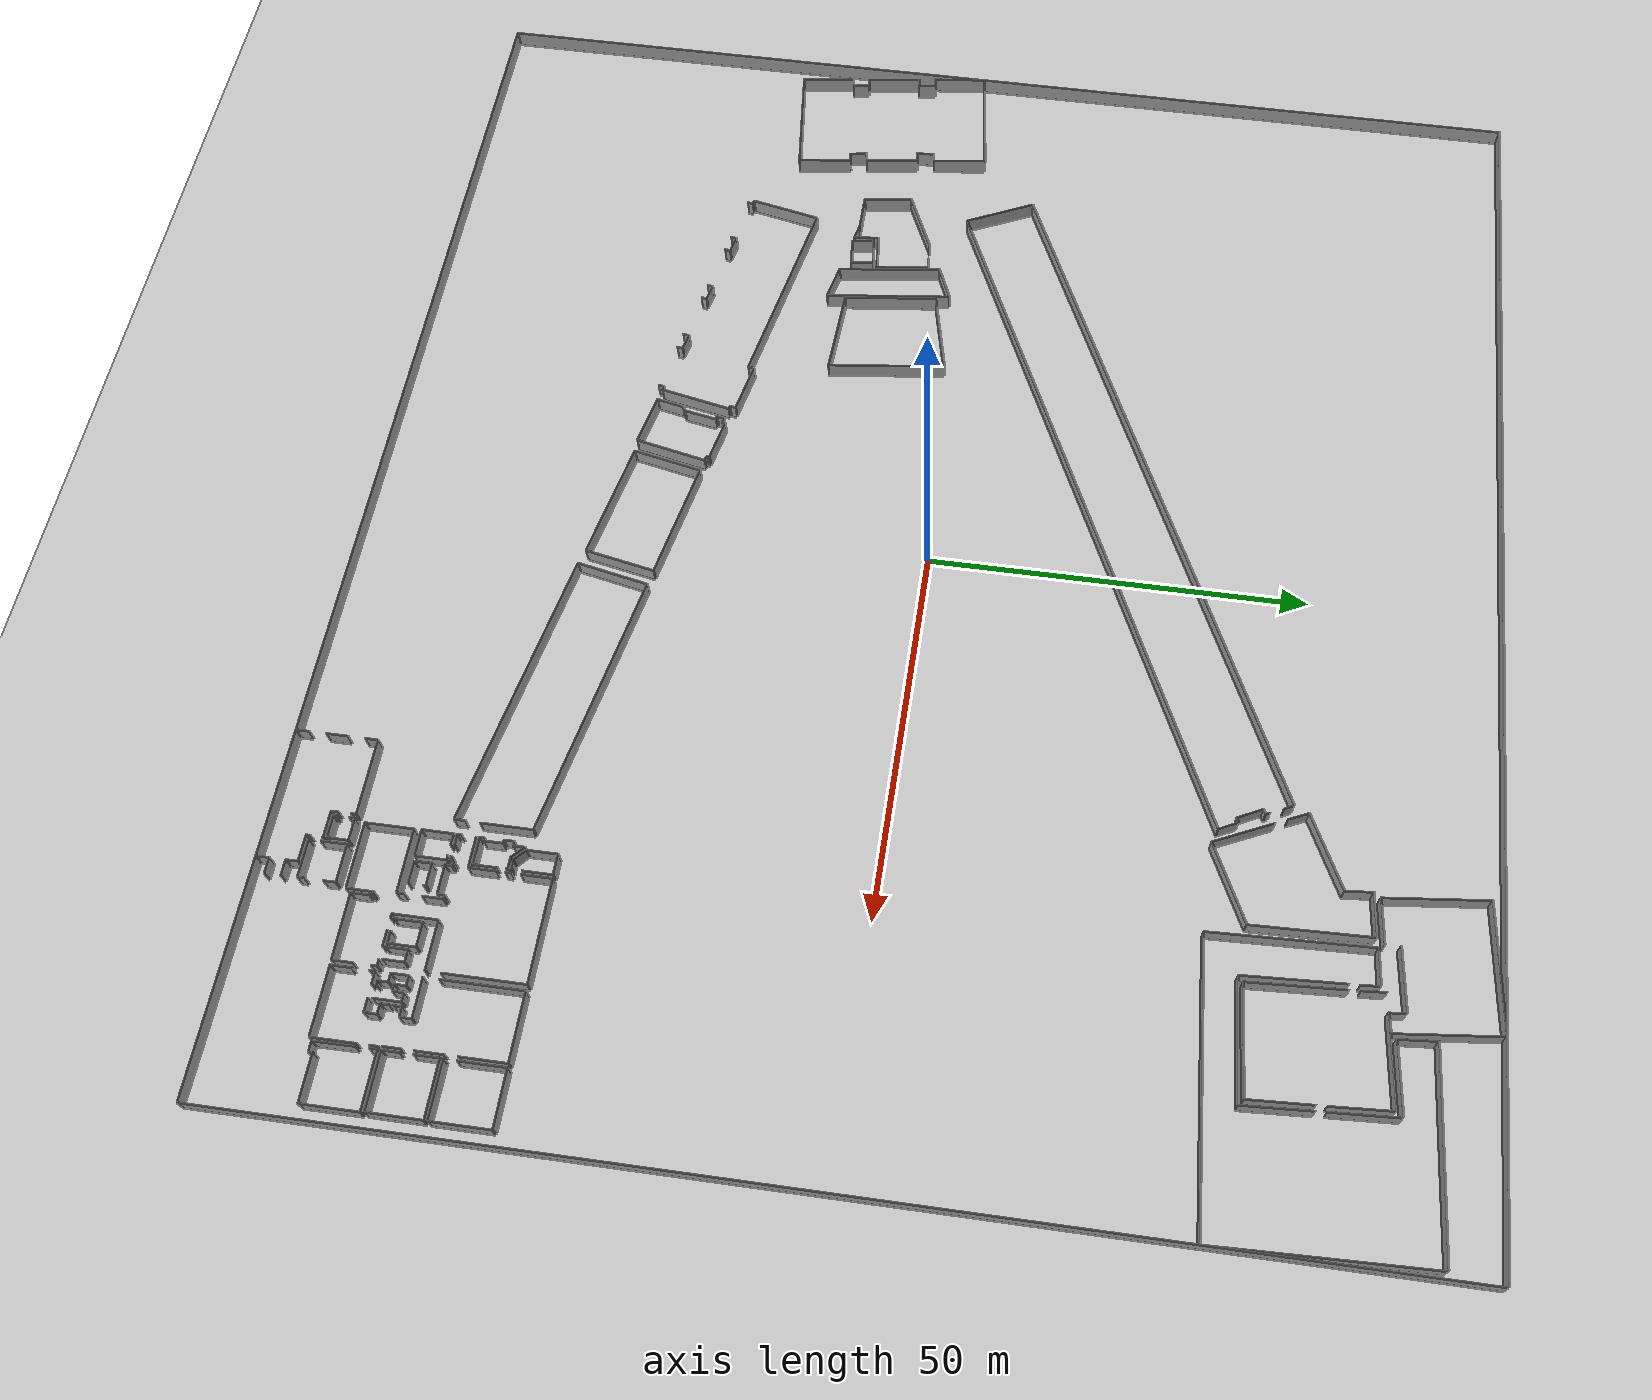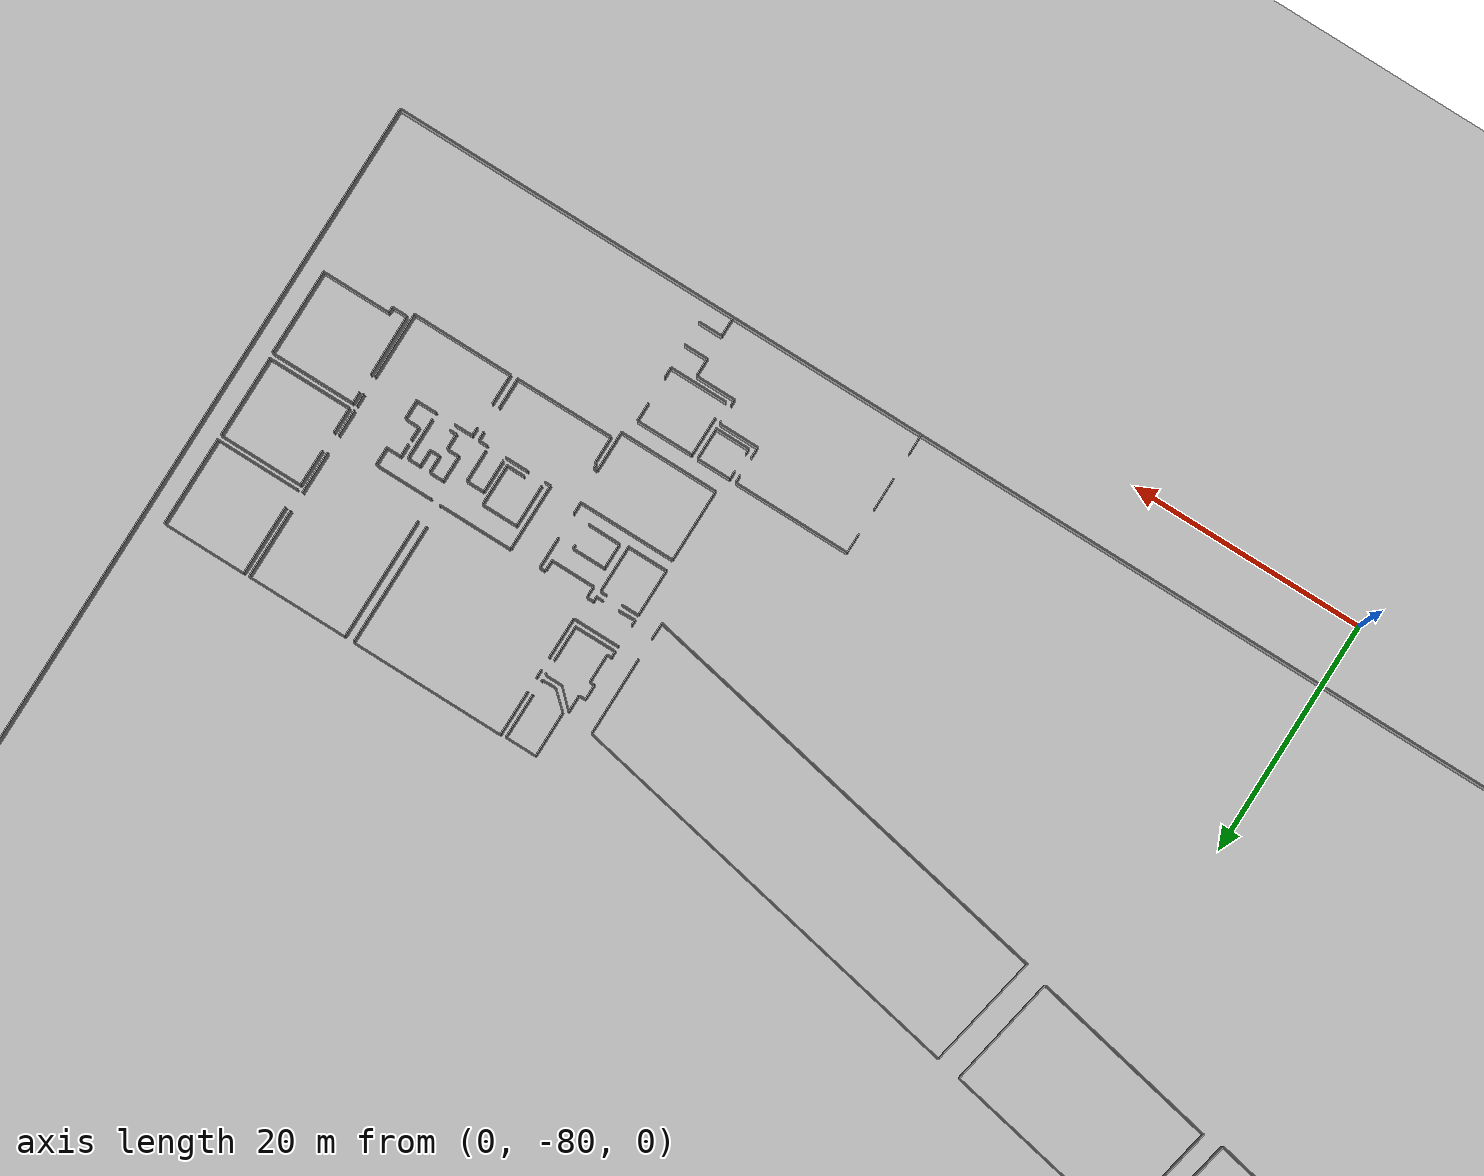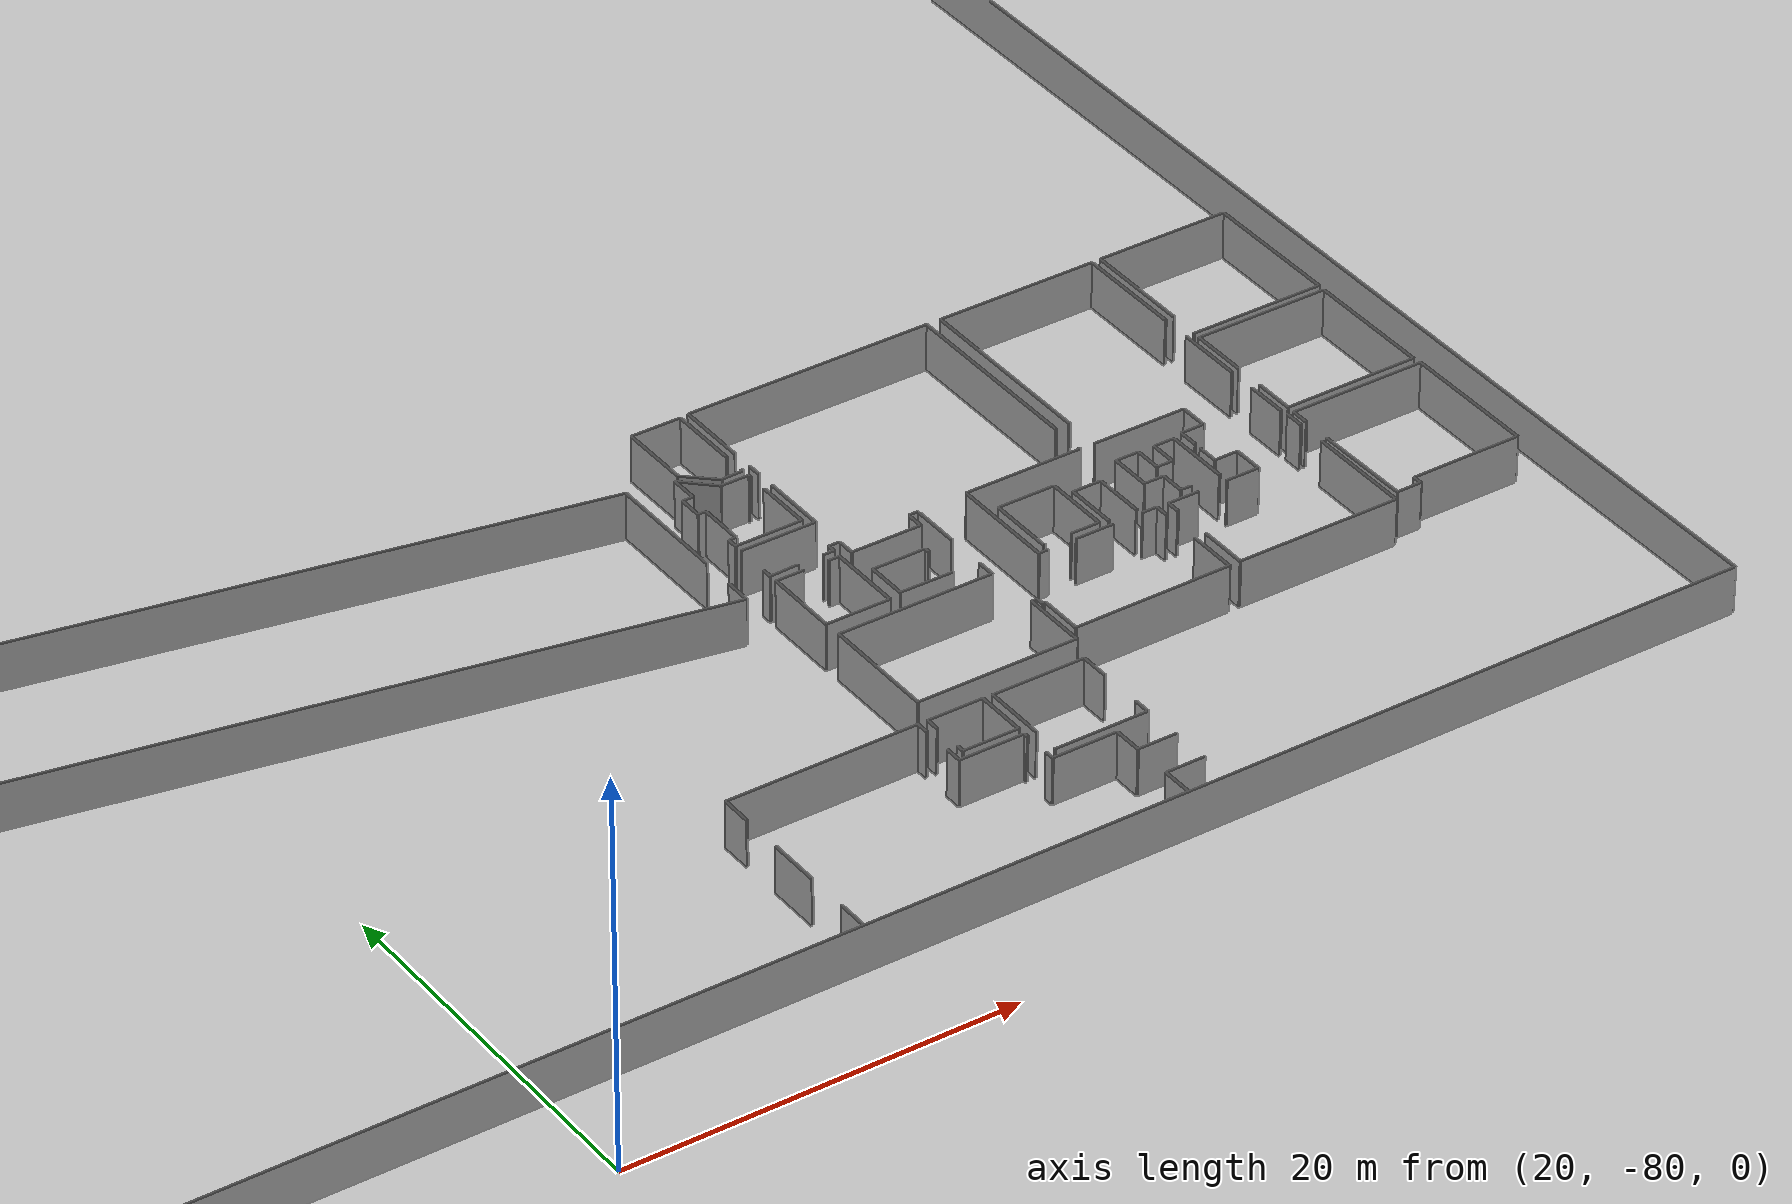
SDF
<sdf version="1.6">
  <world name="default">
    <light name="sun" type="directional">
      <cast_shadows>1</cast_shadows>
      <pose frame="">0 0 10 0 -0 0</pose>
      <diffuse>0.8 0.8 0.8 1</diffuse>
      <specular>0.1 0.1 0.1 1</specular>
      <attenuation>
        <range>1000</range>
        <constant>0.9</constant>
        <linear>0.01</linear>
        <quadratic>0.001</quadratic>
      </attenuation>
      <direction>-0.5 0.5 -1</direction>
    </light>
    <model name="ground_plane">
      <static>1</static>
      <link name="link">
        <collision name="collision">
          <geometry>
            <plane>
              <normal>0 0 1</normal>
              <size>100 100</size>
            </plane>
          </geometry>
          <surface>
            <friction>
              <ode>
                <mu>100</mu>
                <mu2>50</mu2>
              </ode>
              <torsional>
                <ode />
              </torsional>
            </friction>
            <contact>
              <ode />
            </contact>
            <bounce />
          </surface>
          <max_contacts>10</max_contacts>
        </collision>
        <visual name="visual">
          <cast_shadows>0</cast_shadows>
          <geometry>
            <plane>
              <normal>0 0 1</normal>
              <size>100 100</size>
            </plane>
          </geometry>
          <material>
            <script>
              <uri>file://media/materials/scripts/gazebo.material</uri>
              <name>Gazebo/Grey</name>
            </script>
          </material>
        </visual>
        <self_collide>0</self_collide>
        <kinematic>0</kinematic>
        <gravity>1</gravity>
      </link>
    </model>
    <gravity>0 0 -9.8</gravity>
    <magnetic_field>6e-06 2.3e-05 -4.2e-05</magnetic_field>
    <atmosphere type="adiabatic" />
    <physics default="0" name="default_physics" type="ode">
      <max_step_size>0.001</max_step_size>
      <real_time_factor>1</real_time_factor>
      <real_time_update_rate>1000</real_time_update_rate>
    </physics>
    <scene>
      <ambient>0.4 0.4 0.4 1</ambient>
      <background>0.7 0.7 0.7 1</background>
      <shadows>1</shadows>
    </scene>
    <spherical_coordinates>
      <surface_model>EARTH_WGS84</surface_model>
      <latitude_deg>0</latitude_deg>
      <longitude_deg>0</longitude_deg>
      <elevation>0</elevation>
      <heading_deg>0</heading_deg>
    </spherical_coordinates>
  <model name="50023964">
		<static>1</static>
		<link name="Wall_0">
			<collision name="Wall_0_Collision">
				<geometry>
					<box>
						<size>1.6860690356 0.1 2.5</size>
					</box>
				</geometry>
				<pose frame="">0.843034517799 0 1.25 0 0 0</pose>
			</collision>
			<visual name="Wall_0_Visual">
				<pose frame="">0.843034517799 0 1.25 0 0 0</pose>
				<geometry>
					<box>
						<size>1.6860690356 0.1 2.5</size>
					</box>
				</geometry>
				<material>
					<script>
						<uri>file://media/materials/scripts/gazebo.material</uri>
						<name>Gazebo/Grey</name>
					</script>
					<ambient>1 1 1 1</ambient>
				</material>
			</visual>
			<pose frame="">117.97580261 -149.084119272 0 0 0 1.57079632679</pose>
		</link>
		<link name="Wall_1">
			<collision name="Wall_1_Collision">
				<geometry>
					<box>
						<size>2.77234765489 0.1 2.5</size>
					</box>
				</geometry>
				<pose frame="">1.38617382744 0 1.25 0 0 0</pose>
			</collision>
			<visual name="Wall_1_Visual">
				<pose frame="">1.38617382744 0 1.25 0 0 0</pose>
				<geometry>
					<box>
						<size>2.77234765489 0.1 2.5</size>
					</box>
				</geometry>
				<material>
					<script>
						<uri>file://media/materials/scripts/gazebo.material</uri>
						<name>Gazebo/Grey</name>
					</script>
					<ambient>1 1 1 1</ambient>
				</material>
			</visual>
			<pose frame="">117.97580261 -145.190435362 0 0 0 1.57079632679</pose>
		</link>
		<link name="Wall_2">
			<collision name="Wall_2_Collision">
				<geometry>
					<box>
						<size>1.64440633832 0.1 2.5</size>
					</box>
				</geometry>
				<pose frame="">0.822203169159 0 1.25 0 0 0</pose>
			</collision>
			<visual name="Wall_2_Visual">
				<pose frame="">0.822203169159 0 1.25 0 0 0</pose>
				<geometry>
					<box>
						<size>1.64440633832 0.1 2.5</size>
					</box>
				</geometry>
				<material>
					<script>
						<uri>file://media/materials/scripts/gazebo.material</uri>
						<name>Gazebo/Grey</name>
					</script>
					<ambient>1 1 1 1</ambient>
				</material>
			</visual>
			<pose frame="">117.97580261 -140.209202629 0 0 0 1.57079632679</pose>
		</link>
		<link name="Wall_3">
			<collision name="Wall_3_Collision">
				<geometry>
					<box>
						<size>9.94315836271 0.1 2.5</size>
					</box>
				</geometry>
				<pose frame="">4.97157918135 0 1.25 0 0 0</pose>
			</collision>
			<visual name="Wall_3_Visual">
				<pose frame="">4.97157918135 0 1.25 0 0 0</pose>
				<geometry>
					<box>
						<size>9.94315836271 0.1 2.5</size>
					</box>
				</geometry>
				<material>
					<script>
						<uri>file://media/materials/scripts/gazebo.material</uri>
						<name>Gazebo/Grey</name>
					</script>
					<ambient>1 1 1 1</ambient>
				</material>
			</visual>
			<pose frame="">117.97580261 -138.564796291 0 0 0 0.0</pose>
		</link>
		<link name="Wall_4">
			<collision name="Wall_4_Collision">
				<geometry>
					<box>
						<size>0.652122828745 0.1 2.5</size>
					</box>
				</geometry>
				<pose frame="">0.326061414372 0 1.25 0 0 0</pose>
			</collision>
			<visual name="Wall_4_Visual">
				<pose frame="">0.326061414372 0 1.25 0 0 0</pose>
				<geometry>
					<box>
						<size>0.652122828745 0.1 2.5</size>
					</box>
				</geometry>
				<material>
					<script>
						<uri>file://media/materials/scripts/gazebo.material</uri>
						<name>Gazebo/Grey</name>
					</script>
					<ambient>1 1 1 1</ambient>
				</material>
			</visual>
			<pose frame="">127.918960973 -138.564796291 0 0 0 -1.57079632679</pose>
		</link>
		<link name="Wall_5">
			<collision name="Wall_5_Collision">
				<geometry>
					<box>
						<size>0.913276809247 0.1 2.5</size>
					</box>
				</geometry>
				<pose frame="">0.456638404624 0 1.25 0 0 0</pose>
			</collision>
			<visual name="Wall_5_Visual">
				<pose frame="">0.456638404624 0 1.25 0 0 0</pose>
				<geometry>
					<box>
						<size>0.913276809247 0.1 2.5</size>
					</box>
				</geometry>
				<material>
					<script>
						<uri>file://media/materials/scripts/gazebo.material</uri>
						<name>Gazebo/Grey</name>
					</script>
					<ambient>1 1 1 1</ambient>
				</material>
			</visual>
			<pose frame="">127.918960973 -140.798831412 0 0 0 -1.57079632679</pose>
		</link>
		<link name="Wall_6">
			<collision name="Wall_6_Collision">
				<geometry>
					<box>
						<size>3.40033660411 0.1 2.5</size>
					</box>
				</geometry>
				<pose frame="">1.70016830205 0 1.25 0 0 0</pose>
			</collision>
			<visual name="Wall_6_Visual">
				<pose frame="">1.70016830205 0 1.25 0 0 0</pose>
				<geometry>
					<box>
						<size>3.40033660411 0.1 2.5</size>
					</box>
				</geometry>
				<material>
					<script>
						<uri>file://media/materials/scripts/gazebo.material</uri>
						<name>Gazebo/Grey</name>
					</script>
					<ambient>1 1 1 1</ambient>
				</material>
			</visual>
			<pose frame="">127.918960973 -141.712108221 0 0 0 0.0</pose>
		</link>
		<link name="Wall_7">
			<collision name="Wall_7_Collision">
				<geometry>
					<box>
						<size>0.219999364898 0.1 2.5</size>
					</box>
				</geometry>
				<pose frame="">0.109999682449 0 1.25 0 0 0</pose>
			</collision>
			<visual name="Wall_7_Visual">
				<pose frame="">0.109999682449 0 1.25 0 0 0</pose>
				<geometry>
					<box>
						<size>0.219999364898 0.1 2.5</size>
					</box>
				</geometry>
				<material>
					<script>
						<uri>file://media/materials/scripts/gazebo.material</uri>
						<name>Gazebo/Grey</name>
					</script>
					<ambient>1 1 1 1</ambient>
				</material>
			</visual>
			<pose frame="">131.319297577 -141.712108221 0 0 0 -1.57079632679</pose>
		</link>
		<link name="Wall_8">
			<collision name="Wall_8_Collision">
				<geometry>
					<box>
						<size>0.496649836461 0.1 2.5</size>
					</box>
				</geometry>
				<pose frame="">0.248324918231 0 1.25 0 0 0</pose>
			</collision>
			<visual name="Wall_8_Visual">
				<pose frame="">0.248324918231 0 1.25 0 0 0</pose>
				<geometry>
					<box>
						<size>0.496649836461 0.1 2.5</size>
					</box>
				</geometry>
				<material>
					<script>
						<uri>file://media/materials/scripts/gazebo.material</uri>
						<name>Gazebo/Grey</name>
					</script>
					<ambient>1 1 1 1</ambient>
				</material>
			</visual>
			<pose frame="">131.319297577 -143.338985742 0 0 0 -1.57079632679</pose>
		</link>
		<link name="Wall_9">
			<collision name="Wall_9_Collision">
				<geometry>
					<box>
						<size>3.40008256327 0.1 2.5</size>
					</box>
				</geometry>
				<pose frame="">1.70004128164 0 1.25 0 0 0</pose>
			</collision>
			<visual name="Wall_9_Visual">
				<pose frame="">1.70004128164 0 1.25 0 0 0</pose>
				<geometry>
					<box>
						<size>3.40008256327 0.1 2.5</size>
					</box>
				</geometry>
				<material>
					<script>
						<uri>file://media/materials/scripts/gazebo.material</uri>
						<name>Gazebo/Grey</name>
					</script>
					<ambient>1 1 1 1</ambient>
				</material>
			</visual>
			<pose frame="">131.319297577 -143.835635578 0 0 0 0.0</pose>
		</link>
		<link name="Wall_10">
			<collision name="Wall_10_Collision">
				<geometry>
					<box>
						<size>1.52907179829 0.1 2.5</size>
					</box>
				</geometry>
				<pose frame="">0.764535899146 0 1.25 0 0 0</pose>
			</collision>
			<visual name="Wall_10_Visual">
				<pose frame="">0.764535899146 0 1.25 0 0 0</pose>
				<geometry>
					<box>
						<size>1.52907179829 0.1 2.5</size>
					</box>
				</geometry>
				<material>
					<script>
						<uri>file://media/materials/scripts/gazebo.material</uri>
						<name>Gazebo/Grey</name>
					</script>
					<ambient>1 1 1 1</ambient>
				</material>
			</visual>
			<pose frame="">134.71938014 -143.835635578 0 0 0 -1.57079632679</pose>
		</link>
		<link name="Wall_11">
			<collision name="Wall_11_Collision">
				<geometry>
					<box>
						<size>2.0541742085 0.1 2.5</size>
					</box>
				</geometry>
				<pose frame="">1.02708710425 0 1.25 0 0 0</pose>
			</collision>
			<visual name="Wall_11_Visual">
				<pose frame="">1.02708710425 0 1.25 0 0 0</pose>
				<geometry>
					<box>
						<size>2.0541742085 0.1 2.5</size>
					</box>
				</geometry>
				<material>
					<script>
						<uri>file://media/materials/scripts/gazebo.material</uri>
						<name>Gazebo/Grey</name>
					</script>
					<ambient>1 1 1 1</ambient>
				</material>
			</visual>
			<pose frame="">134.71938014 -145.364707377 0 0 0 0.0</pose>
		</link>
		<link name="Wall_12">
			<collision name="Wall_12_Collision">
				<geometry>
					<box>
						<size>2.04325045251 0.1 2.5</size>
					</box>
				</geometry>
				<pose frame="">1.02162522626 0 1.25 0 0 0</pose>
			</collision>
			<visual name="Wall_12_Visual">
				<pose frame="">1.02162522626 0 1.25 0 0 0</pose>
				<geometry>
					<box>
						<size>2.04325045251 0.1 2.5</size>
					</box>
				</geometry>
				<material>
					<script>
						<uri>file://media/materials/scripts/gazebo.material</uri>
						<name>Gazebo/Grey</name>
					</script>
					<ambient>1 1 1 1</ambient>
				</material>
			</visual>
			<pose frame="">136.773554349 -147.412784605 0 0 0 3.14159265359</pose>
		</link>
		<link name="Wall_13">
			<collision name="Wall_13_Collision">
				<geometry>
					<box>
						<size>1.65939474771 0.1 2.5</size>
					</box>
				</geometry>
				<pose frame="">0.829697373853 0 1.25 0 0 0</pose>
			</collision>
			<visual name="Wall_13_Visual">
				<pose frame="">0.829697373853 0 1.25 0 0 0</pose>
				<geometry>
					<box>
						<size>1.65939474771 0.1 2.5</size>
					</box>
				</geometry>
				<material>
					<script>
						<uri>file://media/materials/scripts/gazebo.material</uri>
						<name>Gazebo/Grey</name>
					</script>
					<ambient>1 1 1 1</ambient>
				</material>
			</visual>
			<pose frame="">134.730303896 -147.412784605 0 0 0 -1.57079632679</pose>
		</link>
		<link name="Wall_14">
			<collision name="Wall_14_Collision">
				<geometry>
					<box>
						<size>16.7545055405 0.1 2.5</size>
					</box>
				</geometry>
				<pose frame="">8.37725277026 0 1.25 0 0 0</pose>
			</collision>
			<visual name="Wall_14_Visual">
				<pose frame="">8.37725277026 0 1.25 0 0 0</pose>
				<geometry>
					<box>
						<size>16.7545055405 0.1 2.5</size>
					</box>
				</geometry>
				<material>
					<script>
						<uri>file://media/materials/scripts/gazebo.material</uri>
						<name>Gazebo/Grey</name>
					</script>
					<ambient>1 1 1 1</ambient>
				</material>
			</visual>
			<pose frame="">134.730303896 -149.072179353 0 0 0 -3.14088001422</pose>
		</link>
		<link name="Wall_15">
			<collision name="Wall_15_Collision">
				<geometry>
					<box>
						<size>4.92712203487 0.1 2.5</size>
					</box>
				</geometry>
				<pose frame="">2.46356101743 0 1.25 0 0 0</pose>
			</collision>
			<visual name="Wall_15_Visual">
				<pose frame="">2.46356101743 0 1.25 0 0 0</pose>
				<geometry>
					<box>
						<size>4.92712203487 0.1 2.5</size>
					</box>
				</geometry>
				<material>
					<script>
						<uri>file://media/materials/scripts/gazebo.material</uri>
						<name>Gazebo/Grey</name>
					</script>
					<ambient>1 1 1 1</ambient>
				</material>
			</visual>
			<pose frame="">131.763615001 -143.351179702 0 0 0 0.0</pose>
		</link>
		<link name="Wall_16">
			<collision name="Wall_16_Collision">
				<geometry>
					<box>
						<size>0.931821790353 0.1 2.5</size>
					</box>
				</geometry>
				<pose frame="">0.465910895176 0 1.25 0 0 0</pose>
			</collision>
			<visual name="Wall_16_Visual">
				<pose frame="">0.465910895176 0 1.25 0 0 0</pose>
				<geometry>
					<box>
						<size>0.931821790353 0.1 2.5</size>
					</box>
				</geometry>
				<material>
					<script>
						<uri>file://media/materials/scripts/gazebo.material</uri>
						<name>Gazebo/Grey</name>
					</script>
					<ambient>1 1 1 1</ambient>
				</material>
			</visual>
			<pose frame="">136.690737036 -143.351179702 0 0 0 1.57079632679</pose>
		</link>
		<link name="Wall_17">
			<collision name="Wall_17_Collision">
				<geometry>
					<box>
						<size>1.54101171763 0.1 2.5</size>
					</box>
				</geometry>
				<pose frame="">0.770505858817 0 1.25 0 0 0</pose>
			</collision>
			<visual name="Wall_17_Visual">
				<pose frame="">0.770505858817 0 1.25 0 0 0</pose>
				<geometry>
					<box>
						<size>1.54101171763 0.1 2.5</size>
					</box>
				</geometry>
				<material>
					<script>
						<uri>file://media/materials/scripts/gazebo.material</uri>
						<name>Gazebo/Grey</name>
					</script>
					<ambient>1 1 1 1</ambient>
				</material>
			</visual>
			<pose frame="">136.690737036 -140.133244419 0 0 0 1.57079632679</pose>
		</link>
		<link name="Wall_18">
			<collision name="Wall_18_Collision">
				<geometry>
					<box>
						<size>4.86513607062 0.1 2.5</size>
					</box>
				</geometry>
				<pose frame="">2.43256803531 0 1.25 0 0 0</pose>
			</collision>
			<visual name="Wall_18_Visual">
				<pose frame="">2.43256803531 0 1.25 0 0 0</pose>
				<geometry>
					<box>
						<size>4.86513607062 0.1 2.5</size>
					</box>
				</geometry>
				<material>
					<script>
						<uri>file://media/materials/scripts/gazebo.material</uri>
						<name>Gazebo/Grey</name>
					</script>
					<ambient>1 1 1 1</ambient>
				</material>
			</visual>
			<pose frame="">136.690737036 -138.592232701 0 0 0 3.14159265359</pose>
		</link>
		<link name="Wall_19">
			<collision name="Wall_19_Collision">
				<geometry>
					<box>
						<size>3.30481724937 0.1 2.5</size>
					</box>
				</geometry>
				<pose frame="">1.65240862469 0 1.25 0 0 0</pose>
			</collision>
			<visual name="Wall_19_Visual">
				<pose frame="">1.65240862469 0 1.25 0 0 0</pose>
				<geometry>
					<box>
						<size>3.30481724937 0.1 2.5</size>
					</box>
				</geometry>
				<material>
					<script>
						<uri>file://media/materials/scripts/gazebo.material</uri>
						<name>Gazebo/Grey</name>
					</script>
					<ambient>1 1 1 1</ambient>
				</material>
			</visual>
			<pose frame="">131.825600965 -138.592232701 0 0 0 -1.57079632679</pose>
		</link>
		<link name="Wall_20">
			<collision name="Wall_20_Collision">
				<geometry>
					<box>
						<size>0.0741242233267 0.1 2.5</size>
					</box>
				</geometry>
				<pose frame="">0.0370621116633 0 1.25 0 0 0</pose>
			</collision>
			<visual name="Wall_20_Visual">
				<pose frame="">0.0370621116633 0 1.25 0 0 0</pose>
				<geometry>
					<box>
						<size>0.0741242233267 0.1 2.5</size>
					</box>
				</geometry>
				<material>
					<script>
						<uri>file://media/materials/scripts/gazebo.material</uri>
						<name>Gazebo/Grey</name>
					</script>
					<ambient>1 1 1 1</ambient>
				</material>
			</visual>
			<pose frame="">131.825600965 -143.310533168 0 0 0 -2.5611944662</pose>
		</link>
		<link name="Wall_21">
			<collision name="Wall_21_Collision">
				<geometry>
					<box>
						<size>0.448382077419 0.1 2.5</size>
					</box>
				</geometry>
				<pose frame="">0.224191038709 0 1.25 0 0 0</pose>
			</collision>
			<visual name="Wall_21_Visual">
				<pose frame="">0.224191038709 0 1.25 0 0 0</pose>
				<geometry>
					<box>
						<size>0.448382077419 0.1 2.5</size>
					</box>
				</geometry>
				<material>
					<script>
						<uri>file://media/materials/scripts/gazebo.material</uri>
						<name>Gazebo/Grey</name>
					</script>
					<ambient>1 1 1 1</ambient>
				</material>
			</visual>
			<pose frame="">128.425264361 -141.255342796 0 0 0 1.57079632679</pose>
		</link>
		<link name="Wall_22">
			<collision name="Wall_22_Collision">
				<geometry>
					<box>
						<size>0.719951732241 0.1 2.5</size>
					</box>
				</geometry>
				<pose frame="">0.35997586612 0 1.25 0 0 0</pose>
			</collision>
			<visual name="Wall_22_Visual">
				<pose frame="">0.35997586612 0 1.25 0 0 0</pose>
				<geometry>
					<box>
						<size>0.719951732241 0.1 2.5</size>
					</box>
				</geometry>
				<material>
					<script>
						<uri>file://media/materials/scripts/gazebo.material</uri>
						<name>Gazebo/Grey</name>
					</script>
					<ambient>1 1 1 1</ambient>
				</material>
			</visual>
			<pose frame="">128.425264361 -139.287034391 0 0 0 1.57079632679</pose>
		</link>
		<link name="Wall_23">
			<collision name="Wall_23_Collision">
				<geometry>
					<box>
						<size>2.89758978756 0.1 2.5</size>
					</box>
				</geometry>
				<pose frame="">1.44879489378 0 1.25 0 0 0</pose>
			</collision>
			<visual name="Wall_23_Visual">
				<pose frame="">1.44879489378 0 1.25 0 0 0</pose>
				<geometry>
					<box>
						<size>2.89758978756 0.1 2.5</size>
					</box>
				</geometry>
				<material>
					<script>
						<uri>file://media/materials/scripts/gazebo.material</uri>
						<name>Gazebo/Grey</name>
					</script>
					<ambient>1 1 1 1</ambient>
				</material>
			</visual>
			<pose frame="">128.425264361 -138.567082659 0 0 0 0.0</pose>
		</link>
		<link name="Wall_24">
			<collision name="Wall_24_Collision">
				<geometry>
					<box>
						<size>2.69029246451 0.1 2.5</size>
					</box>
				</geometry>
				<pose frame="">1.34514623226 0 1.25 0 0 0</pose>
			</collision>
			<visual name="Wall_24_Visual">
				<pose frame="">1.34514623226 0 1.25 0 0 0</pose>
				<geometry>
					<box>
						<size>2.69029246451 0.1 2.5</size>
					</box>
				</geometry>
				<material>
					<script>
						<uri>file://media/materials/scripts/gazebo.material</uri>
						<name>Gazebo/Grey</name>
					</script>
					<ambient>1 1 1 1</ambient>
				</material>
			</visual>
			<pose frame="">131.322854149 -138.567082659 0 0 0 -1.57079632679</pose>
		</link>
		<link name="Wall_25">
			<collision name="Wall_25_Collision">
				<geometry>
					<box>
						<size>2.89759050028 0.1 2.5</size>
					</box>
				</geometry>
				<pose frame="">1.44879525014 0 1.25 0 0 0</pose>
			</collision>
			<visual name="Wall_25_Visual">
				<pose frame="">1.44879525014 0 1.25 0 0 0</pose>
				<geometry>
					<box>
						<size>2.89759050028 0.1 2.5</size>
					</box>
				</geometry>
				<material>
					<script>
						<uri>file://media/materials/scripts/gazebo.material</uri>
						<name>Gazebo/Grey</name>
					</script>
					<ambient>1 1 1 1</ambient>
				</material>
			</visual>
			<pose frame="">131.322854149 -141.257375123 0 0 0 3.14089126847</pose>
		</link>
		<link name="Wall_26">
			<collision name="Wall_26_Collision">
				<geometry>
					<box>
						<size>2.31786859738 0.1 2.5</size>
					</box>
				</geometry>
				<pose frame="">1.15893429869 0 1.25 0 0 0</pose>
			</collision>
			<visual name="Wall_26_Visual">
				<pose frame="">1.15893429869 0 1.25 0 0 0</pose>
				<geometry>
					<box>
						<size>2.31786859738 0.1 2.5</size>
					</box>
				</geometry>
				<material>
					<script>
						<uri>file://media/materials/scripts/gazebo.material</uri>
						<name>Gazebo/Grey</name>
					</script>
					<ambient>1 1 1 1</ambient>
				</material>
			</visual>
			<pose frame="">137.703597853 -136.502238735 0 0 0 1.57079632679</pose>
		</link>
		<link name="Wall_27">
			<collision name="Wall_27_Collision">
				<geometry>
					<box>
						<size>0.153948747261 0.1 2.5</size>
					</box>
				</geometry>
				<pose frame="">0.0769743736305 0 1.25 0 0 0</pose>
			</collision>
			<visual name="Wall_27_Visual">
				<pose frame="">0.0769743736305 0 1.25 0 0 0</pose>
				<geometry>
					<box>
						<size>0.153948747261 0.1 2.5</size>
					</box>
				</geometry>
				<material>
					<script>
						<uri>file://media/materials/scripts/gazebo.material</uri>
						<name>Gazebo/Grey</name>
					</script>
					<ambient>1 1 1 1</ambient>
				</material>
			</visual>
			<pose frame="">137.703597853 -134.184370137 0 0 0 3.14159265359</pose>
		</link>
		<link name="Wall_28">
			<collision name="Wall_28_Collision">
				<geometry>
					<box>
						<size>0.40417897177 0.1 2.5</size>
					</box>
				</geometry>
				<pose frame="">0.202089485885 0 1.25 0 0 0</pose>
			</collision>
			<visual name="Wall_28_Visual">
				<pose frame="">0.202089485885 0 1.25 0 0 0</pose>
				<geometry>
					<box>
						<size>0.40417897177 0.1 2.5</size>
					</box>
				</geometry>
				<material>
					<script>
						<uri>file://media/materials/scripts/gazebo.material</uri>
						<name>Gazebo/Grey</name>
					</script>
					<ambient>1 1 1 1</ambient>
				</material>
			</visual>
			<pose frame="">137.549649106 -134.184370137 0 0 0 1.57079632679</pose>
		</link>
		<link name="Wall_29">
			<collision name="Wall_29_Collision">
				<geometry>
					<box>
						<size>0.303324759455 0.1 2.5</size>
					</box>
				</geometry>
				<pose frame="">0.151662379728 0 1.25 0 0 0</pose>
			</collision>
			<visual name="Wall_29_Visual">
				<pose frame="">0.151662379728 0 1.25 0 0 0</pose>
				<geometry>
					<box>
						<size>0.303324759455 0.1 2.5</size>
					</box>
				</geometry>
				<material>
					<script>
						<uri>file://media/materials/scripts/gazebo.material</uri>
						<name>Gazebo/Grey</name>
					</script>
					<ambient>1 1 1 1</ambient>
				</material>
			</visual>
			<pose frame="">137.549649106 -133.780191166 0 0 0 3.14159265359</pose>
		</link>
		<link name="Wall_30">
			<collision name="Wall_30_Collision">
				<geometry>
					<box>
						<size>3.43539423962 0.1 2.5</size>
					</box>
				</geometry>
				<pose frame="">1.71769711981 0 1.25 0 0 0</pose>
			</collision>
			<visual name="Wall_30_Visual">
				<pose frame="">1.71769711981 0 1.25 0 0 0</pose>
				<geometry>
					<box>
						<size>3.43539423962 0.1 2.5</size>
					</box>
				</geometry>
				<material>
					<script>
						<uri>file://media/materials/scripts/gazebo.material</uri>
						<name>Gazebo/Grey</name>
					</script>
					<ambient>1 1 1 1</ambient>
				</material>
			</visual>
			<pose frame="">137.246324347 -133.780191166 0 0 0 -1.57079632679</pose>
		</link>
		<link name="Wall_31">
			<collision name="Wall_31_Collision">
				<geometry>
					<box>
						<size>8.41180019688 0.1 2.5</size>
					</box>
				</geometry>
				<pose frame="">4.20590009844 0 1.25 0 0 0</pose>
			</collision>
			<visual name="Wall_31_Visual">
				<pose frame="">4.20590009844 0 1.25 0 0 0</pose>
				<geometry>
					<box>
						<size>8.41180019688 0.1 2.5</size>
					</box>
				</geometry>
				<material>
					<script>
						<uri>file://media/materials/scripts/gazebo.material</uri>
						<name>Gazebo/Grey</name>
					</script>
					<ambient>1 1 1 1</ambient>
				</material>
			</visual>
			<pose frame="">137.246324347 -137.215585405 0 0 0 3.14159265359</pose>
		</link>
		<link name="Wall_32">
			<collision name="Wall_32_Collision">
				<geometry>
					<box>
						<size>6.13051348004 0.1 2.5</size>
					</box>
				</geometry>
				<pose frame="">3.06525674002 0 1.25 0 0 0</pose>
			</collision>
			<visual name="Wall_32_Visual">
				<pose frame="">3.06525674002 0 1.25 0 0 0</pose>
				<geometry>
					<box>
						<size>6.13051348004 0.1 2.5</size>
					</box>
				</geometry>
				<material>
					<script>
						<uri>file://media/materials/scripts/gazebo.material</uri>
						<name>Gazebo/Grey</name>
					</script>
					<ambient>1 1 1 1</ambient>
				</material>
			</visual>
			<pose frame="">128.83452415 -137.215585405 0 0 0 1.57079632679</pose>
		</link>
		<link name="Wall_33">
			<collision name="Wall_33_Collision">
				<geometry>
					<box>
						<size>8.17579625925 0.1 2.5</size>
					</box>
				</geometry>
				<pose frame="">4.08789812962 0 1.25 0 0 0</pose>
			</collision>
			<visual name="Wall_33_Visual">
				<pose frame="">4.08789812962 0 1.25 0 0 0</pose>
				<geometry>
					<box>
						<size>8.17579625925 0.1 2.5</size>
					</box>
				</geometry>
				<material>
					<script>
						<uri>file://media/materials/scripts/gazebo.material</uri>
						<name>Gazebo/Grey</name>
					</script>
					<ambient>1 1 1 1</ambient>
				</material>
			</visual>
			<pose frame="">128.83452415 -131.085071925 0 0 0 0.0</pose>
		</link>
		<link name="Wall_34">
			<collision name="Wall_34_Collision">
				<geometry>
					<box>
						<size>1.01616334826 0.1 2.5</size>
					</box>
				</geometry>
				<pose frame="">0.508081674129 0 1.25 0 0 0</pose>
			</collision>
			<visual name="Wall_34_Visual">
				<pose frame="">0.508081674129 0 1.25 0 0 0</pose>
				<geometry>
					<box>
						<size>1.01616334826 0.1 2.5</size>
					</box>
				</geometry>
				<material>
					<script>
						<uri>file://media/materials/scripts/gazebo.material</uri>
						<name>Gazebo/Grey</name>
					</script>
					<ambient>1 1 1 1</ambient>
				</material>
			</visual>
			<pose frame="">137.010320409 -131.085071925 0 0 0 1.57079632679</pose>
		</link>
		<link name="Wall_35">
			<collision name="Wall_35_Collision">
				<geometry>
					<box>
						<size>2.55565082087 0.1 2.5</size>
					</box>
				</geometry>
				<pose frame="">1.27782541043 0 1.25 0 0 0</pose>
			</collision>
			<visual name="Wall_35_Visual">
				<pose frame="">1.27782541043 0 1.25 0 0 0</pose>
				<geometry>
					<box>
						<size>2.55565082087 0.1 2.5</size>
					</box>
				</geometry>
				<material>
					<script>
						<uri>file://media/materials/scripts/gazebo.material</uri>
						<name>Gazebo/Grey</name>
					</script>
					<ambient>1 1 1 1</ambient>
				</material>
			</visual>
			<pose frame="">137.010320409 -127.912355911 0 0 0 1.57079632679</pose>
		</link>
		<link name="Wall_36">
			<collision name="Wall_36_Collision">
				<geometry>
					<box>
						<size>5.594233273 0.1 2.5</size>
					</box>
				</geometry>
				<pose frame="">2.7971166365 0 1.25 0 0 0</pose>
			</collision>
			<visual name="Wall_36_Visual">
				<pose frame="">2.7971166365 0 1.25 0 0 0</pose>
				<geometry>
					<box>
						<size>5.594233273 0.1 2.5</size>
					</box>
				</geometry>
				<material>
					<script>
						<uri>file://media/materials/scripts/gazebo.material</uri>
						<name>Gazebo/Grey</name>
					</script>
					<ambient>1 1 1 1</ambient>
				</material>
			</visual>
			<pose frame="">139.617033438 -125.35670509 0 0 0 -1.57079632679</pose>
		</link>
		<link name="Wall_37">
			<collision name="Wall_37_Collision">
				<geometry>
					<box>
						<size>0.509097837477 0.1 2.5</size>
					</box>
				</geometry>
				<pose frame="">0.254548918739 0 1.25 0 0 0</pose>
			</collision>
			<visual name="Wall_37_Visual">
				<pose frame="">0.254548918739 0 1.25 0 0 0</pose>
				<geometry>
					<box>
						<size>0.509097837477 0.1 2.5</size>
					</box>
				</geometry>
				<material>
					<script>
						<uri>file://media/materials/scripts/gazebo.material</uri>
						<name>Gazebo/Grey</name>
					</script>
					<ambient>1 1 1 1</ambient>
				</material>
			</visual>
			<pose frame="">139.617033438 -130.950938363 0 0 0 0.0</pose>
		</link>
		<link name="Wall_38">
			<collision name="Wall_38_Collision">
				<geometry>
					<box>
						<size>2.00997110285 0.1 2.5</size>
					</box>
				</geometry>
				<pose frame="">1.00498555143 0 1.25 0 0 0</pose>
			</collision>
			<visual name="Wall_38_Visual">
				<pose frame="">1.00498555143 0 1.25 0 0 0</pose>
				<geometry>
					<box>
						<size>2.00997110285 0.1 2.5</size>
					</box>
				</geometry>
				<material>
					<script>
						<uri>file://media/materials/scripts/gazebo.material</uri>
						<name>Gazebo/Grey</name>
					</script>
					<ambient>1 1 1 1</ambient>
				</material>
			</visual>
			<pose frame="">141.627512623 -130.950938363 0 0 0 0.0</pose>
		</link>
		<link name="Wall_39">
			<collision name="Wall_39_Collision">
				<geometry>
					<box>
						<size>0.803785208472 0.1 2.5</size>
					</box>
				</geometry>
				<pose frame="">0.401892604236 0 1.25 0 0 0</pose>
			</collision>
			<visual name="Wall_39_Visual">
				<pose frame="">0.401892604236 0 1.25 0 0 0</pose>
				<geometry>
					<box>
						<size>0.803785208472 0.1 2.5</size>
					</box>
				</geometry>
				<material>
					<script>
						<uri>file://media/materials/scripts/gazebo.material</uri>
						<name>Gazebo/Grey</name>
					</script>
					<ambient>1 1 1 1</ambient>
				</material>
			</visual>
			<pose frame="">145.241497571 -130.950938363 0 0 0 0.0</pose>
		</link>
		<link name="Wall_40">
			<collision name="Wall_40_Collision">
				<geometry>
					<box>
						<size>0.752977041059 0.1 2.5</size>
					</box>
				</geometry>
				<pose frame="">0.37648852053 0 1.25 0 0 0</pose>
			</collision>
			<visual name="Wall_40_Visual">
				<pose frame="">0.37648852053 0 1.25 0 0 0</pose>
				<geometry>
					<box>
						<size>0.752977041059 0.1 2.5</size>
					</box>
				</geometry>
				<material>
					<script>
						<uri>file://media/materials/scripts/gazebo.material</uri>
						<name>Gazebo/Grey</name>
					</script>
					<ambient>1 1 1 1</ambient>
				</material>
			</visual>
			<pose frame="">146.045282779 -130.950938363 0 0 0 -1.57079632679</pose>
		</link>
		<link name="Wall_41">
			<collision name="Wall_41_Collision">
				<geometry>
					<box>
						<size>2.61408021339 0.1 2.5</size>
					</box>
				</geometry>
				<pose frame="">1.3070401067 0 1.25 0 0 0</pose>
			</collision>
			<visual name="Wall_41_Visual">
				<pose frame="">1.3070401067 0 1.25 0 0 0</pose>
				<geometry>
					<box>
						<size>2.61408021339 0.1 2.5</size>
					</box>
				</geometry>
				<material>
					<script>
						<uri>file://media/materials/scripts/gazebo.material</uri>
						<name>Gazebo/Grey</name>
					</script>
					<ambient>1 1 1 1</ambient>
				</material>
			</visual>
			<pose frame="">146.045282779 -133.849798355 0 0 0 -1.57079632679</pose>
		</link>
		<link name="Wall_42">
			<collision name="Wall_42_Collision">
				<geometry>
					<box>
						<size>8.34177312713 0.1 2.5</size>
					</box>
				</geometry>
				<pose frame="">4.17088656357 0 1.25 0 0 0</pose>
			</collision>
			<visual name="Wall_42_Visual">
				<pose frame="">4.17088656357 0 1.25 0 0 0</pose>
				<geometry>
					<box>
						<size>8.34177312713 0.1 2.5</size>
					</box>
				</geometry>
				<material>
					<script>
						<uri>file://media/materials/scripts/gazebo.material</uri>
						<name>Gazebo/Grey</name>
					</script>
					<ambient>1 1 1 1</ambient>
				</material>
			</visual>
			<pose frame="">146.045282779 -136.463878568 0 0 0 -3.13699407473</pose>
		</link>
		<link name="Wall_43">
			<collision name="Wall_43_Collision">
				<geometry>
					<box>
						<size>3.54920453463 0.1 2.5</size>
					</box>
				</geometry>
				<pose frame="">1.77460226731 0 1.25 0 0 0</pose>
			</collision>
			<visual name="Wall_43_Visual">
				<pose frame="">1.77460226731 0 1.25 0 0 0</pose>
				<geometry>
					<box>
						<size>3.54920453463 0.1 2.5</size>
					</box>
				</geometry>
				<material>
					<script>
						<uri>file://media/materials/scripts/gazebo.material</uri>
						<name>Gazebo/Grey</name>
					</script>
					<ambient>1 1 1 1</ambient>
				</material>
			</visual>
			<pose frame="">140.16398336 -130.559461433 0 0 0 1.57079632679</pose>
		</link>
		<link name="Wall_44">
			<collision name="Wall_44_Collision">
				<geometry>
					<box>
						<size>3.04391730971 0.1 2.5</size>
					</box>
				</geometry>
				<pose frame="">1.52195865485 0 1.25 0 0 0</pose>
			</collision>
			<visual name="Wall_44_Visual">
				<pose frame="">1.52195865485 0 1.25 0 0 0</pose>
				<geometry>
					<box>
						<size>3.04391730971 0.1 2.5</size>
					</box>
				</geometry>
				<material>
					<script>
						<uri>file://media/materials/scripts/gazebo.material</uri>
						<name>Gazebo/Grey</name>
					</script>
					<ambient>1 1 1 1</ambient>
				</material>
			</visual>
			<pose frame="">140.16398336 -127.010256899 0 0 0 0.0</pose>
		</link>
		<link name="Wall_45">
			<collision name="Wall_45_Collision">
				<geometry>
					<box>
						<size>3.48366199867 0.1 2.5</size>
					</box>
				</geometry>
				<pose frame="">1.74183099933 0 1.25 0 0 0</pose>
			</collision>
			<visual name="Wall_45_Visual">
				<pose frame="">1.74183099933 0 1.25 0 0 0</pose>
				<geometry>
					<box>
						<size>3.48366199867 0.1 2.5</size>
					</box>
				</geometry>
				<material>
					<script>
						<uri>file://media/materials/scripts/gazebo.material</uri>
						<name>Gazebo/Grey</name>
					</script>
					<ambient>1 1 1 1</ambient>
				</material>
			</visual>
			<pose frame="">143.20790067 -127.010256899 0 0 0 -1.57079632679</pose>
		</link>
		<link name="Wall_46">
			<collision name="Wall_46_Collision">
				<geometry>
					<box>
						<size>1.52653138992 0.1 2.5</size>
					</box>
				</geometry>
				<pose frame="">0.76326569496 0 1.25 0 0 0</pose>
			</collision>
			<visual name="Wall_46_Visual">
				<pose frame="">0.76326569496 0 1.25 0 0 0</pose>
				<geometry>
					<box>
						<size>1.52653138992 0.1 2.5</size>
					</box>
				</geometry>
				<material>
					<script>
						<uri>file://media/materials/scripts/gazebo.material</uri>
						<name>Gazebo/Grey</name>
					</script>
					<ambient>1 1 1 1</ambient>
				</material>
			</visual>
			<pose frame="">143.20790067 -130.493918897 0 0 0 3.14159265359</pose>
		</link>
		<link name="Wall_47">
			<collision name="Wall_47_Collision">
				<geometry>
					<box>
						<size>0.0928709509964 0.1 2.5</size>
					</box>
				</geometry>
				<pose frame="">0.0464354754982 0 1.25 0 0 0</pose>
			</collision>
			<visual name="Wall_47_Visual">
				<pose frame="">0.0464354754982 0 1.25 0 0 0</pose>
				<geometry>
					<box>
						<size>0.0928709509964 0.1 2.5</size>
					</box>
				</geometry>
				<material>
					<script>
						<uri>file://media/materials/scripts/gazebo.material</uri>
						<name>Gazebo/Grey</name>
					</script>
					<ambient>1 1 1 1</ambient>
				</material>
			</visual>
			<pose frame="">140.229779937 -130.493918897 0 0 0 -2.35812872376</pose>
		</link>
		<link name="Wall_48">
			<collision name="Wall_48_Collision">
				<geometry>
					<box>
						<size>2.73170112096 0.1 2.5</size>
					</box>
				</geometry>
				<pose frame="">1.36585056048 0 1.25 0 0 0</pose>
			</collision>
			<visual name="Wall_48_Visual">
				<pose frame="">1.36585056048 0 1.25 0 0 0</pose>
				<geometry>
					<box>
						<size>2.73170112096 0.1 2.5</size>
					</box>
				</geometry>
				<material>
					<script>
						<uri>file://media/materials/scripts/gazebo.material</uri>
						<name>Gazebo/Grey</name>
					</script>
					<ambient>1 1 1 1</ambient>
				</material>
			</visual>
			<pose frame="">143.644342828 -130.60391858 0 0 0 1.57079632679</pose>
		</link>
		<link name="Wall_49">
			<collision name="Wall_49_Collision">
				<geometry>
					<box>
						<size>1.52602330825 0.1 2.5</size>
					</box>
				</geometry>
				<pose frame="">0.763011654123 0 1.25 0 0 0</pose>
			</collision>
			<visual name="Wall_49_Visual">
				<pose frame="">0.763011654123 0 1.25 0 0 0</pose>
				<geometry>
					<box>
						<size>1.52602330825 0.1 2.5</size>
					</box>
				</geometry>
				<material>
					<script>
						<uri>file://media/materials/scripts/gazebo.material</uri>
						<name>Gazebo/Grey</name>
					</script>
					<ambient>1 1 1 1</ambient>
				</material>
			</visual>
			<pose frame="">143.644342828 -127.872217459 0 0 0 0.0</pose>
		</link>
		<link name="Wall_50">
			<collision name="Wall_50_Collision">
				<geometry>
					<box>
						<size>2.73170112096 0.1 2.5</size>
					</box>
				</geometry>
				<pose frame="">1.36585056048 0 1.25 0 0 0</pose>
			</collision>
			<visual name="Wall_50_Visual">
				<pose frame="">1.36585056048 0 1.25 0 0 0</pose>
				<geometry>
					<box>
						<size>2.73170112096 0.1 2.5</size>
					</box>
				</geometry>
				<material>
					<script>
						<uri>file://media/materials/scripts/gazebo.material</uri>
						<name>Gazebo/Grey</name>
					</script>
					<ambient>1 1 1 1</ambient>
				</material>
			</visual>
			<pose frame="">145.170366136 -127.872217459 0 0 0 -1.57079632679</pose>
		</link>
		<link name="Wall_51">
			<collision name="Wall_51_Collision">
				<geometry>
					<box>
						<size>0.0530945349465 0.1 2.5</size>
					</box>
				</geometry>
				<pose frame="">0.0265472674732 0 1.25 0 0 0</pose>
			</collision>
			<visual name="Wall_51_Visual">
				<pose frame="">0.0265472674732 0 1.25 0 0 0</pose>
				<geometry>
					<box>
						<size>0.0530945349465 0.1 2.5</size>
					</box>
				</geometry>
				<material>
					<script>
						<uri>file://media/materials/scripts/gazebo.material</uri>
						<name>Gazebo/Grey</name>
					</script>
					<ambient>1 1 1 1</ambient>
				</material>
			</visual>
			<pose frame="">143.697437363 -130.60391858 0 0 0 3.14159265359</pose>
		</link>
		<link name="Wall_52">
			<collision name="Wall_52_Collision">
				<geometry>
					<box>
						<size>2.15248801245 0.1 2.5</size>
					</box>
				</geometry>
				<pose frame="">1.07624400622 0 1.25 0 0 0</pose>
			</collision>
			<visual name="Wall_52_Visual">
				<pose frame="">1.07624400622 0 1.25 0 0 0</pose>
				<geometry>
					<box>
						<size>2.15248801245 0.1 2.5</size>
					</box>
				</geometry>
				<material>
					<script>
						<uri>file://media/materials/scripts/gazebo.material</uri>
						<name>Gazebo/Grey</name>
					</script>
					<ambient>1 1 1 1</ambient>
				</material>
			</visual>
			<pose frame="">132.841256232 -129.983804897 0 0 0 1.57079632679</pose>
		</link>
		<link name="Wall_53">
			<collision name="Wall_53_Collision">
				<geometry>
					<box>
						<size>2.81146994379 0.1 2.5</size>
					</box>
				</geometry>
				<pose frame="">1.4057349719 0 1.25 0 0 0</pose>
			</collision>
			<visual name="Wall_53_Visual">
				<pose frame="">1.4057349719 0 1.25 0 0 0</pose>
				<geometry>
					<box>
						<size>2.81146994379 0.1 2.5</size>
					</box>
				</geometry>
				<material>
					<script>
						<uri>file://media/materials/scripts/gazebo.material</uri>
						<name>Gazebo/Grey</name>
					</script>
					<ambient>1 1 1 1</ambient>
				</material>
			</visual>
			<pose frame="">132.841256232 -127.831316884 0 0 0 0.0</pose>
		</link>
		<link name="Wall_54">
			<collision name="Wall_54_Collision">
				<geometry>
					<box>
						<size>0.296465656854 0.1 2.5</size>
					</box>
				</geometry>
				<pose frame="">0.148232828427 0 1.25 0 0 0</pose>
			</collision>
			<visual name="Wall_54_Visual">
				<pose frame="">0.148232828427 0 1.25 0 0 0</pose>
				<geometry>
					<box>
						<size>0.296465656854 0.1 2.5</size>
					</box>
				</geometry>
				<material>
					<script>
						<uri>file://media/materials/scripts/gazebo.material</uri>
						<name>Gazebo/Grey</name>
					</script>
					<ambient>1 1 1 1</ambient>
				</material>
			</visual>
			<pose frame="">135.652726176 -127.831316884 0 0 0 -1.57079632679</pose>
		</link>
		<link name="Wall_55">
			<collision name="Wall_55_Collision">
				<geometry>
					<box>
						<size>2.81158702234 0.1 2.5</size>
					</box>
				</geometry>
				<pose frame="">1.40579351117 0 1.25 0 0 0</pose>
			</collision>
			<visual name="Wall_55_Visual">
				<pose frame="">1.40579351117 0 1.25 0 0 0</pose>
				<geometry>
					<box>
						<size>2.81158702234 0.1 2.5</size>
					</box>
				</geometry>
				<material>
					<script>
						<uri>file://media/materials/scripts/gazebo.material</uri>
						<name>Gazebo/Grey</name>
					</script>
					<ambient>1 1 1 1</ambient>
				</material>
			</visual>
			<pose frame="">135.652726176 -130.009463021 0 0 0 3.13246667581</pose>
		</link>
		<link name="Wall_56">
			<collision name="Wall_56_Collision">
				<geometry>
					<box>
						<size>0.582261598552 0.1 2.5</size>
					</box>
				</geometry>
				<pose frame="">0.291130799276 0 1.25 0 0 0</pose>
			</collision>
			<visual name="Wall_56_Visual">
				<pose frame="">0.291130799276 0 1.25 0 0 0</pose>
				<geometry>
					<box>
						<size>0.582261598552 0.1 2.5</size>
					</box>
				</geometry>
				<material>
					<script>
						<uri>file://media/materials/scripts/gazebo.material</uri>
						<name>Gazebo/Grey</name>
					</script>
					<ambient>1 1 1 1</ambient>
				</material>
			</visual>
			<pose frame="">147.722968467 -130.456066813 0 0 0 0.0</pose>
		</link>
		<link name="Wall_57">
			<collision name="Wall_57_Collision">
				<geometry>
					<box>
						<size>3.49585595885 0.1 2.5</size>
					</box>
				</geometry>
				<pose frame="">1.74792797942 0 1.25 0 0 0</pose>
			</collision>
			<visual name="Wall_57_Visual">
				<pose frame="">1.74792797942 0 1.25 0 0 0</pose>
				<geometry>
					<box>
						<size>3.49585595885 0.1 2.5</size>
					</box>
				</geometry>
				<material>
					<script>
						<uri>file://media/materials/scripts/gazebo.material</uri>
						<name>Gazebo/Grey</name>
					</script>
					<ambient>1 1 1 1</ambient>
				</material>
			</visual>
			<pose frame="">149.856657458 -130.456066813 0 0 0 1.57079632679</pose>
		</link>
		<link name="Wall_58">
			<collision name="Wall_58_Collision">
				<geometry>
					<box>
						<size>1.10787209044 0.1 2.5</size>
					</box>
				</geometry>
				<pose frame="">0.553936045219 0 1.25 0 0 0</pose>
			</collision>
			<visual name="Wall_58_Visual">
				<pose frame="">0.553936045219 0 1.25 0 0 0</pose>
				<geometry>
					<box>
						<size>1.10787209044 0.1 2.5</size>
					</box>
				</geometry>
				<material>
					<script>
						<uri>file://media/materials/scripts/gazebo.material</uri>
						<name>Gazebo/Grey</name>
					</script>
					<ambient>1 1 1 1</ambient>
				</material>
			</visual>
			<pose frame="">149.856657458 -126.960210854 0 0 0 3.14159265359</pose>
		</link>
		<link name="Wall_59">
			<collision name="Wall_59_Collision">
				<geometry>
					<box>
						<size>1.42313676924 0.1 2.5</size>
					</box>
				</geometry>
				<pose frame="">0.711568384618 0 1.25 0 0 0</pose>
			</collision>
			<visual name="Wall_59_Visual">
				<pose frame="">0.711568384618 0 1.25 0 0 0</pose>
				<geometry>
					<box>
						<size>1.42313676924 0.1 2.5</size>
					</box>
				</geometry>
				<material>
					<script>
						<uri>file://media/materials/scripts/gazebo.material</uri>
						<name>Gazebo/Grey</name>
					</script>
					<ambient>1 1 1 1</ambient>
				</material>
			</visual>
			<pose frame="">148.748785367 -126.960210854 0 0 0 -1.57079632679</pose>
		</link>
		<link name="Wall_60">
			<collision name="Wall_60_Collision">
				<geometry>
					<box>
						<size>0.850020640818 0.1 2.5</size>
					</box>
				</geometry>
				<pose frame="">0.425010320409 0 1.25 0 0 0</pose>
			</collision>
			<visual name="Wall_60_Visual">
				<pose frame="">0.425010320409 0 1.25 0 0 0</pose>
				<geometry>
					<box>
						<size>0.850020640818 0.1 2.5</size>
					</box>
				</geometry>
				<material>
					<script>
						<uri>file://media/materials/scripts/gazebo.material</uri>
						<name>Gazebo/Grey</name>
					</script>
					<ambient>1 1 1 1</ambient>
				</material>
			</visual>
			<pose frame="">148.748785367 -128.383347623 0 0 0 3.14159265359</pose>
		</link>
		<link name="Wall_61">
			<collision name="Wall_61_Collision">
				<geometry>
					<box>
						<size>1.44218983202 0.1 2.5</size>
					</box>
				</geometry>
				<pose frame="">0.721094916008 0 1.25 0 0 0</pose>
			</collision>
			<visual name="Wall_61_Visual">
				<pose frame="">0.721094916008 0 1.25 0 0 0</pose>
				<geometry>
					<box>
						<size>1.44218983202 0.1 2.5</size>
					</box>
				</geometry>
				<material>
					<script>
						<uri>file://media/materials/scripts/gazebo.material</uri>
						<name>Gazebo/Grey</name>
					</script>
					<ambient>1 1 1 1</ambient>
				</material>
			</visual>
			<pose frame="">147.898764726 -128.383347623 0 0 0 1.57079632679</pose>
		</link>
		<link name="Wall_62">
			<collision name="Wall_62_Collision">
				<geometry>
					<box>
						<size>1.23209805976 0.1 2.5</size>
					</box>
				</geometry>
				<pose frame="">0.616049029882 0 1.25 0 0 0</pose>
			</collision>
			<visual name="Wall_62_Visual">
				<pose frame="">0.616049029882 0 1.25 0 0 0</pose>
				<geometry>
					<box>
						<size>1.23209805976 0.1 2.5</size>
					</box>
				</geometry>
				<material>
					<script>
						<uri>file://media/materials/scripts/gazebo.material</uri>
						<name>Gazebo/Grey</name>
					</script>
					<ambient>1 1 1 1</ambient>
				</material>
			</visual>
			<pose frame="">147.898764726 -126.941157791 0 0 0 3.14159265359</pose>
		</link>
		<link name="Wall_63">
			<collision name="Wall_63_Collision">
				<geometry>
					<box>
						<size>2.1966911181 0.1 2.5</size>
					</box>
				</geometry>
				<pose frame="">1.09834555905 0 1.25 0 0 0</pose>
			</collision>
			<visual name="Wall_63_Visual">
				<pose frame="">1.09834555905 0 1.25 0 0 0</pose>
				<geometry>
					<box>
						<size>2.1966911181 0.1 2.5</size>
					</box>
				</geometry>
				<material>
					<script>
						<uri>file://media/materials/scripts/gazebo.material</uri>
						<name>Gazebo/Grey</name>
					</script>
					<ambient>1 1 1 1</ambient>
				</material>
			</visual>
			<pose frame="">146.666666667 -126.941157791 0 0 0 -1.57079632679</pose>
		</link>
		<link name="Wall_64">
			<collision name="Wall_64_Collision">
				<geometry>
					<box>
						<size>1.06011241307 0.1 2.5</size>
					</box>
				</geometry>
				<pose frame="">0.530056206535 0 1.25 0 0 0</pose>
			</collision>
			<visual name="Wall_64_Visual">
				<pose frame="">0.530056206535 0 1.25 0 0 0</pose>
				<geometry>
					<box>
						<size>1.06011241307 0.1 2.5</size>
					</box>
				</geometry>
				<material>
					<script>
						<uri>file://media/materials/scripts/gazebo.material</uri>
						<name>Gazebo/Grey</name>
					</script>
					<ambient>1 1 1 1</ambient>
				</material>
			</visual>
			<pose frame="">146.666666667 -129.137848909 0 0 0 0.0</pose>
		</link>
		<link name="Wall_65">
			<collision name="Wall_65_Collision">
				<geometry>
					<box>
						<size>1.31822341124 0.1 2.5</size>
					</box>
				</geometry>
				<pose frame="">0.659111705622 0 1.25 0 0 0</pose>
			</collision>
			<visual name="Wall_65_Visual">
				<pose frame="">0.659111705622 0 1.25 0 0 0</pose>
				<geometry>
					<box>
						<size>1.31822341124 0.1 2.5</size>
					</box>
				</geometry>
				<material>
					<script>
						<uri>file://media/materials/scripts/gazebo.material</uri>
						<name>Gazebo/Grey</name>
					</script>
					<ambient>1 1 1 1</ambient>
				</material>
			</visual>
			<pose frame="">147.72677908 -129.137848909 0 0 0 -1.57368704913</pose>
		</link>
		<link name="Wall_66">
			<collision name="Wall_66_Collision">
				<geometry>
					<box>
						<size>2.59985392652 0.1 2.5</size>
					</box>
				</geometry>
				<pose frame="">1.29992696326 0 1.25 0 0 0</pose>
			</collision>
			<visual name="Wall_66_Visual">
				<pose frame="">1.29992696326 0 1.25 0 0 0</pose>
				<geometry>
					<box>
						<size>2.59985392652 0.1 2.5</size>
					</box>
				</geometry>
				<material>
					<script>
						<uri>file://media/materials/scripts/gazebo.material</uri>
						<name>Gazebo/Grey</name>
					</script>
					<ambient>1 1 1 1</ambient>
				</material>
			</visual>
			<pose frame="">146.650408053 -136.446349751 0 0 0 1.57079632679</pose>
		</link>
		<link name="Wall_67">
			<collision name="Wall_67_Collision">
				<geometry>
					<box>
						<size>0.707757772062 0.1 2.5</size>
					</box>
				</geometry>
				<pose frame="">0.353878886031 0 1.25 0 0 0</pose>
			</collision>
			<visual name="Wall_67_Visual">
				<pose frame="">0.353878886031 0 1.25 0 0 0</pose>
				<geometry>
					<box>
						<size>0.707757772062 0.1 2.5</size>
					</box>
				</geometry>
				<material>
					<script>
						<uri>file://media/materials/scripts/gazebo.material</uri>
						<name>Gazebo/Grey</name>
					</script>
					<ambient>1 1 1 1</ambient>
				</material>
			</visual>
			<pose frame="">146.650408053 -131.713822997 0 0 0 1.57079632679</pose>
		</link>
		<link name="Wall_68">
			<collision name="Wall_68_Collision">
				<geometry>
					<box>
						<size>1.61849417294 0.1 2.5</size>
					</box>
				</geometry>
				<pose frame="">0.809247086469 0 1.25 0 0 0</pose>
			</collision>
			<visual name="Wall_68_Visual">
				<pose frame="">0.809247086469 0 1.25 0 0 0</pose>
				<geometry>
					<box>
						<size>1.61849417294 0.1 2.5</size>
					</box>
				</geometry>
				<material>
					<script>
						<uri>file://media/materials/scripts/gazebo.material</uri>
						<name>Gazebo/Grey</name>
					</script>
					<ambient>1 1 1 1</ambient>
				</material>
			</visual>
			<pose frame="">146.650408053 -131.006065225 0 0 0 0.0</pose>
		</link>
		<link name="Wall_69">
			<collision name="Wall_69_Collision">
				<geometry>
					<box>
						<size>1.75720046998 0.1 2.5</size>
					</box>
				</geometry>
				<pose frame="">0.878600234988 0 1.25 0 0 0</pose>
			</collision>
			<visual name="Wall_69_Visual">
				<pose frame="">0.878600234988 0 1.25 0 0 0</pose>
				<geometry>
					<box>
						<size>1.75720046998 0.1 2.5</size>
					</box>
				</geometry>
				<material>
					<script>
						<uri>file://media/materials/scripts/gazebo.material</uri>
						<name>Gazebo/Grey</name>
					</script>
					<ambient>1 1 1 1</ambient>
				</material>
			</visual>
			<pose frame="">149.864786764 -131.006065225 0 0 0 0.0</pose>
		</link>
		<link name="Wall_70">
			<collision name="Wall_70_Collision">
				<geometry>
					<box>
						<size>1.60706233527 0.1 2.5</size>
					</box>
				</geometry>
				<pose frame="">0.803531167635 0 1.25 0 0 0</pose>
			</collision>
			<visual name="Wall_70_Visual">
				<pose frame="">0.803531167635 0 1.25 0 0 0</pose>
				<geometry>
					<box>
						<size>1.60706233527 0.1 2.5</size>
					</box>
				</geometry>
				<material>
					<script>
						<uri>file://media/materials/scripts/gazebo.material</uri>
						<name>Gazebo/Grey</name>
					</script>
					<ambient>1 1 1 1</ambient>
				</material>
			</visual>
			<pose frame="">151.621987234 -131.006065225 0 0 0 1.57079632679</pose>
		</link>
		<link name="Wall_71">
			<collision name="Wall_71_Collision">
				<geometry>
					<box>
						<size>1.24530818329 0.1 2.5</size>
					</box>
				</geometry>
				<pose frame="">0.622654091645 0 1.25 0 0 0</pose>
			</collision>
			<visual name="Wall_71_Visual">
				<pose frame="">0.622654091645 0 1.25 0 0 0</pose>
				<geometry>
					<box>
						<size>1.24530818329 0.1 2.5</size>
					</box>
				</geometry>
				<material>
					<script>
						<uri>file://media/materials/scripts/gazebo.material</uri>
						<name>Gazebo/Grey</name>
					</script>
					<ambient>1 1 1 1</ambient>
				</material>
			</visual>
			<pose frame="">151.621987234 -129.39900289 0 0 0 3.14159265359</pose>
		</link>
		<link name="Wall_72">
			<collision name="Wall_72_Collision">
				<geometry>
					<box>
						<size>1.13581658252 0.1 2.5</size>
					</box>
				</geometry>
				<pose frame="">0.567908291258 0 1.25 0 0 0</pose>
			</collision>
			<visual name="Wall_72_Visual">
				<pose frame="">0.567908291258 0 1.25 0 0 0</pose>
				<geometry>
					<box>
						<size>1.13581658252 0.1 2.5</size>
					</box>
				</geometry>
				<material>
					<script>
						<uri>file://media/materials/scripts/gazebo.material</uri>
						<name>Gazebo/Grey</name>
					</script>
					<ambient>1 1 1 1</ambient>
				</material>
			</visual>
			<pose frame="">150.376679051 -129.39900289 0 0 0 1.57079632679</pose>
		</link>
		<link name="Wall_73">
			<collision name="Wall_73_Collision">
				<geometry>
					<box>
						<size>1.03547045188 0.1 2.5</size>
					</box>
				</geometry>
				<pose frame="">0.517735225938 0 1.25 0 0 0</pose>
			</collision>
			<visual name="Wall_73_Visual">
				<pose frame="">0.517735225938 0 1.25 0 0 0</pose>
				<geometry>
					<box>
						<size>1.03547045188 0.1 2.5</size>
					</box>
				</geometry>
				<material>
					<script>
						<uri>file://media/materials/scripts/gazebo.material</uri>
						<name>Gazebo/Grey</name>
					</script>
					<ambient>1 1 1 1</ambient>
				</material>
			</visual>
			<pose frame="">155.254263123 -128.263186307 0 0 0 -1.57079632679</pose>
		</link>
		<link name="Wall_74">
			<collision name="Wall_74_Collision">
				<geometry>
					<box>
						<size>5.60414086564 0.1 2.5</size>
					</box>
				</geometry>
				<pose frame="">2.80207043282 0 1.25 0 0 0</pose>
			</collision>
			<visual name="Wall_74_Visual">
				<pose frame="">2.80207043282 0 1.25 0 0 0</pose>
				<geometry>
					<box>
						<size>5.60414086564 0.1 2.5</size>
					</box>
				</geometry>
				<material>
					<script>
						<uri>file://media/materials/scripts/gazebo.material</uri>
						<name>Gazebo/Grey</name>
					</script>
					<ambient>1 1 1 1</ambient>
				</material>
			</visual>
			<pose frame="">155.254263123 -130.856689213 0 0 0 -1.57079632679</pose>
		</link>
		<link name="Wall_75">
			<collision name="Wall_75_Collision">
				<geometry>
					<box>
						<size>8.60386725492 0.1 2.5</size>
					</box>
				</geometry>
				<pose frame="">4.30193362746 0 1.25 0 0 0</pose>
			</collision>
			<visual name="Wall_75_Visual">
				<pose frame="">4.30193362746 0 1.25 0 0 0</pose>
				<geometry>
					<box>
						<size>8.60386725492 0.1 2.5</size>
					</box>
				</geometry>
				<material>
					<script>
						<uri>file://media/materials/scripts/gazebo.material</uri>
						<name>Gazebo/Grey</name>
					</script>
					<ambient>1 1 1 1</ambient>
				</material>
			</visual>
			<pose frame="">155.254263123 -136.460830078 0 0 0 3.13990965057</pose>
		</link>
		<link name="Wall_76">
			<collision name="Wall_76_Collision">
				<geometry>
					<box>
						<size>1.30907243339 0.1 2.5</size>
					</box>
				</geometry>
				<pose frame="">0.654536216697 0 1.25 0 0 0</pose>
			</collision>
			<visual name="Wall_76_Visual">
				<pose frame="">0.654536216697 0 1.25 0 0 0</pose>
				<geometry>
					<box>
						<size>1.30907243339 0.1 2.5</size>
					</box>
				</geometry>
				<material>
					<script>
						<uri>file://media/materials/scripts/gazebo.material</uri>
						<name>Gazebo/Grey</name>
					</script>
					<ambient>1 1 1 1</ambient>
				</material>
			</visual>
			<pose frame="">155.648788543 -136.028452574 0 0 0 0.0</pose>
		</link>
		<link name="Wall_77">
			<collision name="Wall_77_Collision">
				<geometry>
					<box>
						<size>0.503000857388 0.1 2.5</size>
					</box>
				</geometry>
				<pose frame="">0.251500428694 0 1.25 0 0 0</pose>
			</collision>
			<visual name="Wall_77_Visual">
				<pose frame="">0.251500428694 0 1.25 0 0 0</pose>
				<geometry>
					<box>
						<size>0.503000857388 0.1 2.5</size>
					</box>
				</geometry>
				<material>
					<script>
						<uri>file://media/materials/scripts/gazebo.material</uri>
						<name>Gazebo/Grey</name>
					</script>
					<ambient>1 1 1 1</ambient>
				</material>
			</visual>
			<pose frame="">156.957860976 -136.028452574 0 0 0 1.57079632679</pose>
		</link>
		<link name="Wall_78">
			<collision name="Wall_78_Collision">
				<geometry>
					<box>
						<size>5.83201549649 0.1 2.5</size>
					</box>
				</geometry>
				<pose frame="">2.91600774825 0 1.25 0 0 0</pose>
			</collision>
			<visual name="Wall_78_Visual">
				<pose frame="">2.91600774825 0 1.25 0 0 0</pose>
				<geometry>
					<box>
						<size>5.83201549649 0.1 2.5</size>
					</box>
				</geometry>
				<material>
					<script>
						<uri>file://media/materials/scripts/gazebo.material</uri>
						<name>Gazebo/Grey</name>
					</script>
					<ambient>1 1 1 1</ambient>
				</material>
			</visual>
			<pose frame="">156.957860976 -135.525451716 0 0 0 0.0</pose>
		</link>
		<link name="Wall_79">
			<collision name="Wall_79_Collision">
				<geometry>
					<box>
						<size>7.24575275476 0.1 2.5</size>
					</box>
				</geometry>
				<pose frame="">3.62287637738 0 1.25 0 0 0</pose>
			</collision>
			<visual name="Wall_79_Visual">
				<pose frame="">3.62287637738 0 1.25 0 0 0</pose>
				<geometry>
					<box>
						<size>7.24575275476 0.1 2.5</size>
					</box>
				</geometry>
				<material>
					<script>
						<uri>file://media/materials/scripts/gazebo.material</uri>
						<name>Gazebo/Grey</name>
					</script>
					<ambient>1 1 1 1</ambient>
				</material>
			</visual>
			<pose frame="">162.789876473 -135.525451716 0 0 0 1.57079632679</pose>
		</link>
		<link name="Wall_80">
			<collision name="Wall_80_Collision">
				<geometry>
					<box>
						<size>7.20154964911 0.1 2.5</size>
					</box>
				</geometry>
				<pose frame="">3.60077482455 0 1.25 0 0 0</pose>
			</collision>
			<visual name="Wall_80_Visual">
				<pose frame="">3.60077482455 0 1.25 0 0 0</pose>
				<geometry>
					<box>
						<size>7.20154964911 0.1 2.5</size>
					</box>
				</geometry>
				<material>
					<script>
						<uri>file://media/materials/scripts/gazebo.material</uri>
						<name>Gazebo/Grey</name>
					</script>
					<ambient>1 1 1 1</ambient>
				</material>
			</visual>
			<pose frame="">162.789876473 -128.279698962 0 0 0 3.14159265359</pose>
		</link>
		<link name="Wall_81">
			<collision name="Wall_81_Collision">
				<geometry>
					<box>
						<size>0.968911752564 0.1 2.5</size>
					</box>
				</geometry>
				<pose frame="">0.484455876282 0 1.25 0 0 0</pose>
			</collision>
			<visual name="Wall_81_Visual">
				<pose frame="">0.484455876282 0 1.25 0 0 0</pose>
				<geometry>
					<box>
						<size>0.968911752564 0.1 2.5</size>
					</box>
				</geometry>
				<material>
					<script>
						<uri>file://media/materials/scripts/gazebo.material</uri>
						<name>Gazebo/Grey</name>
					</script>
					<ambient>1 1 1 1</ambient>
				</material>
			</visual>
			<pose frame="">155.588326824 -128.279698962 0 0 0 -1.57079632679</pose>
		</link>
		<link name="Wall_82">
			<collision name="Wall_82_Collision">
				<geometry>
					<box>
						<size>5.21961918991 0.1 2.5</size>
					</box>
				</geometry>
				<pose frame="">2.60980959495 0 1.25 0 0 0</pose>
			</collision>
			<visual name="Wall_82_Visual">
				<pose frame="">2.60980959495 0 1.25 0 0 0</pose>
				<geometry>
					<box>
						<size>5.21961918991 0.1 2.5</size>
					</box>
				</geometry>
				<material>
					<script>
						<uri>file://media/materials/scripts/gazebo.material</uri>
						<name>Gazebo/Grey</name>
					</script>
					<ambient>1 1 1 1</ambient>
				</material>
			</visual>
			<pose frame="">155.588326824 -130.809183576 0 0 0 -1.55921251786</pose>
		</link>
		<link name="Wall_83">
			<collision name="Wall_83_Collision">
				<geometry>
					<box>
						<size>2.2104093233 0.1 2.5</size>
					</box>
				</geometry>
				<pose frame="">1.10520466165 0 1.25 0 0 0</pose>
			</collision>
			<visual name="Wall_83_Visual">
				<pose frame="">1.10520466165 0 1.25 0 0 0</pose>
				<geometry>
					<box>
						<size>2.2104093233 0.1 2.5</size>
					</box>
				</geometry>
				<material>
					<script>
						<uri>file://media/materials/scripts/gazebo.material</uri>
						<name>Gazebo/Grey</name>
					</script>
					<ambient>1 1 1 1</ambient>
				</material>
			</visual>
			<pose frame="">155.610936458 -127.831316884 0 0 0 1.57079632679</pose>
		</link>
		<link name="Wall_84">
			<collision name="Wall_84_Collision">
				<geometry>
					<box>
						<size>3.09015274205 0.1 2.5</size>
					</box>
				</geometry>
				<pose frame="">1.54507637103 0 1.25 0 0 0</pose>
			</collision>
			<visual name="Wall_84_Visual">
				<pose frame="">1.54507637103 0 1.25 0 0 0</pose>
				<geometry>
					<box>
						<size>3.09015274205 0.1 2.5</size>
					</box>
				</geometry>
				<material>
					<script>
						<uri>file://media/materials/scripts/gazebo.material</uri>
						<name>Gazebo/Grey</name>
					</script>
					<ambient>1 1 1 1</ambient>
				</material>
			</visual>
			<pose frame="">155.610936458 -124.020450287 0 0 0 1.57079632679</pose>
		</link>
		<link name="Wall_85">
			<collision name="Wall_85_Collision">
				<geometry>
					<box>
						<size>7.10984090693 0.1 2.5</size>
					</box>
				</geometry>
				<pose frame="">3.55492045346 0 1.25 0 0 0</pose>
			</collision>
			<visual name="Wall_85_Visual">
				<pose frame="">3.55492045346 0 1.25 0 0 0</pose>
				<geometry>
					<box>
						<size>7.10984090693 0.1 2.5</size>
					</box>
				</geometry>
				<material>
					<script>
						<uri>file://media/materials/scripts/gazebo.material</uri>
						<name>Gazebo/Grey</name>
					</script>
					<ambient>1 1 1 1</ambient>
				</material>
			</visual>
			<pose frame="">155.610936458 -120.930297545 0 0 0 0.0</pose>
		</link>
		<link name="Wall_86">
			<collision name="Wall_86_Collision">
				<geometry>
					<box>
						<size>6.8855228478 0.1 2.5</size>
					</box>
				</geometry>
				<pose frame="">3.4427614239 0 1.25 0 0 0</pose>
			</collision>
			<visual name="Wall_86_Visual">
				<pose frame="">3.4427614239 0 1.25 0 0 0</pose>
				<geometry>
					<box>
						<size>6.8855228478 0.1 2.5</size>
					</box>
				</geometry>
				<material>
					<script>
						<uri>file://media/materials/scripts/gazebo.material</uri>
						<name>Gazebo/Grey</name>
					</script>
					<ambient>1 1 1 1</ambient>
				</material>
			</visual>
			<pose frame="">162.720777365 -120.930297545 0 0 0 -1.57079632679</pose>
		</link>
		<link name="Wall_87">
			<collision name="Wall_87_Collision">
				<geometry>
					<box>
						<size>7.10985779485 0.1 2.5</size>
					</box>
				</geometry>
				<pose frame="">3.55492889743 0 1.25 0 0 0</pose>
			</collision>
			<visual name="Wall_87_Visual">
				<pose frame="">3.55492889743 0 1.25 0 0 0</pose>
				<geometry>
					<box>
						<size>7.10985779485 0.1 2.5</size>
					</box>
				</geometry>
				<material>
					<script>
						<uri>file://media/materials/scripts/gazebo.material</uri>
						<name>Gazebo/Grey</name>
					</script>
					<ambient>1 1 1 1</ambient>
				</material>
			</visual>
			<pose frame="">162.720777365 -127.815820393 0 0 0 -3.13941307366</pose>
		</link>
		<link name="Wall_88">
			<collision name="Wall_88_Collision">
				<geometry>
					<box>
						<size>7.14566066495 0.1 2.5</size>
					</box>
				</geometry>
				<pose frame="">3.57283033248 0 1.25 0 0 0</pose>
			</collision>
			<visual name="Wall_88_Visual">
				<pose frame="">3.57283033248 0 1.25 0 0 0</pose>
				<geometry>
					<box>
						<size>7.14566066495 0.1 2.5</size>
					</box>
				</geometry>
				<material>
					<script>
						<uri>file://media/materials/scripts/gazebo.material</uri>
						<name>Gazebo/Grey</name>
					</script>
					<ambient>1 1 1 1</ambient>
				</material>
			</visual>
			<pose frame="">155.606617764 -120.520021593 0 0 0 0.0</pose>
		</link>
		<link name="Wall_89">
			<collision name="Wall_89_Collision">
				<geometry>
					<box>
						<size>7.51071734781 0.1 2.5</size>
					</box>
				</geometry>
				<pose frame="">3.75535867391 0 1.25 0 0 0</pose>
			</collision>
			<visual name="Wall_89_Visual">
				<pose frame="">3.75535867391 0 1.25 0 0 0</pose>
				<geometry>
					<box>
						<size>7.51071734781 0.1 2.5</size>
					</box>
				</geometry>
				<material>
					<script>
						<uri>file://media/materials/scripts/gazebo.material</uri>
						<name>Gazebo/Grey</name>
					</script>
					<ambient>1 1 1 1</ambient>
				</material>
			</visual>
			<pose frame="">162.752278429 -120.520021593 0 0 0 1.57079632679</pose>
		</link>
		<link name="Wall_90">
			<collision name="Wall_90_Collision">
				<geometry>
					<box>
						<size>7.08799339494 0.1 2.5</size>
					</box>
				</geometry>
				<pose frame="">3.54399669747 0 1.25 0 0 0</pose>
			</collision>
			<visual name="Wall_90_Visual">
				<pose frame="">3.54399669747 0 1.25 0 0 0</pose>
				<geometry>
					<box>
						<size>7.08799339494 0.1 2.5</size>
					</box>
				</geometry>
				<material>
					<script>
						<uri>file://media/materials/scripts/gazebo.material</uri>
						<name>Gazebo/Grey</name>
					</script>
					<ambient>1 1 1 1</ambient>
				</material>
			</visual>
			<pose frame="">162.752278429 -113.009304246 0 0 0 3.14159265359</pose>
		</link>
		<link name="Wall_91">
			<collision name="Wall_91_Collision">
				<geometry>
					<box>
						<size>5.89222317488 0.1 2.5</size>
					</box>
				</geometry>
				<pose frame="">2.94611158744 0 1.25 0 0 0</pose>
			</collision>
			<visual name="Wall_91_Visual">
				<pose frame="">2.94611158744 0 1.25 0 0 0</pose>
				<geometry>
					<box>
						<size>5.89222317488 0.1 2.5</size>
					</box>
				</geometry>
				<material>
					<script>
						<uri>file://media/materials/scripts/gazebo.material</uri>
						<name>Gazebo/Grey</name>
					</script>
					<ambient>1 1 1 1</ambient>
				</material>
			</visual>
			<pose frame="">155.664285034 -113.009304246 0 0 0 -1.57079632679</pose>
		</link>
		<link name="Wall_92">
			<collision name="Wall_92_Collision">
				<geometry>
					<box>
						<size>0.0745535198797 0.1 2.5</size>
					</box>
				</geometry>
				<pose frame="">0.0372767599399 0 1.25 0 0 0</pose>
			</collision>
			<visual name="Wall_92_Visual">
				<pose frame="">0.0372767599399 0 1.25 0 0 0</pose>
				<geometry>
					<box>
						<size>0.0745535198797 0.1 2.5</size>
					</box>
				</geometry>
				<material>
					<script>
						<uri>file://media/materials/scripts/gazebo.material</uri>
						<name>Gazebo/Grey</name>
					</script>
					<ambient>1 1 1 1</ambient>
				</material>
			</visual>
			<pose frame="">155.664285034 -120.472769998 0 0 0 -2.45514389083</pose>
		</link>
		<link name="Wall_93">
			<collision name="Wall_93_Collision">
				<geometry>
					<box>
						<size>10.2807786352 0.1 2.5</size>
					</box>
				</geometry>
				<pose frame="">5.14038931758 0 1.25 0 0 0</pose>
			</collision>
			<visual name="Wall_93_Visual">
				<pose frame="">5.14038931758 0 1.25 0 0 0</pose>
				<geometry>
					<box>
						<size>10.2807786352 0.1 2.5</size>
					</box>
				</geometry>
				<material>
					<script>
						<uri>file://media/materials/scripts/gazebo.material</uri>
						<name>Gazebo/Grey</name>
					</script>
					<ambient>1 1 1 1</ambient>
				</material>
			</visual>
			<pose frame="">146.641770665 -123.309389984 0 0 0 1.57079632679</pose>
		</link>
		<link name="Wall_94">
			<collision name="Wall_94_Collision">
				<geometry>
					<box>
						<size>8.5421231463 0.1 2.5</size>
					</box>
				</geometry>
				<pose frame="">4.27106157315 0 1.25 0 0 0</pose>
			</collision>
			<visual name="Wall_94_Visual">
				<pose frame="">4.27106157315 0 1.25 0 0 0</pose>
				<geometry>
					<box>
						<size>8.5421231463 0.1 2.5</size>
					</box>
				</geometry>
				<material>
					<script>
						<uri>file://media/materials/scripts/gazebo.material</uri>
						<name>Gazebo/Grey</name>
					</script>
					<ambient>1 1 1 1</ambient>
				</material>
			</visual>
			<pose frame="">146.641770665 -113.028611349 0 0 0 0.0</pose>
		</link>
		<link name="Wall_95">
			<collision name="Wall_95_Collision">
				<geometry>
					<box>
						<size>5.85716553936 0.1 2.5</size>
					</box>
				</geometry>
				<pose frame="">2.92858276968 0 1.25 0 0 0</pose>
			</collision>
			<visual name="Wall_95_Visual">
				<pose frame="">2.92858276968 0 1.25 0 0 0</pose>
				<geometry>
					<box>
						<size>5.85716553936 0.1 2.5</size>
					</box>
				</geometry>
				<material>
					<script>
						<uri>file://media/materials/scripts/gazebo.material</uri>
						<name>Gazebo/Grey</name>
					</script>
					<ambient>1 1 1 1</ambient>
				</material>
			</visual>
			<pose frame="">155.183893811 -113.028611349 0 0 0 -1.57079632679</pose>
		</link>
		<link name="Wall_96">
			<collision name="Wall_96_Collision">
				<geometry>
					<box>
						<size>3.57460861834 0.1 2.5</size>
					</box>
				</geometry>
				<pose frame="">1.78730430917 0 1.25 0 0 0</pose>
			</collision>
			<visual name="Wall_96_Visual">
				<pose frame="">1.78730430917 0 1.25 0 0 0</pose>
				<geometry>
					<box>
						<size>3.57460861834 0.1 2.5</size>
					</box>
				</geometry>
				<material>
					<script>
						<uri>file://media/materials/scripts/gazebo.material</uri>
						<name>Gazebo/Grey</name>
					</script>
					<ambient>1 1 1 1</ambient>
				</material>
			</visual>
			<pose frame="">155.183893811 -120.512654409 0 0 0 -1.57079632679</pose>
		</link>
		<link name="Wall_97">
			<collision name="Wall_97_Collision">
				<geometry>
					<box>
						<size>2.24826140802 0.1 2.5</size>
					</box>
				</geometry>
				<pose frame="">1.12413070401 0 1.25 0 0 0</pose>
			</collision>
			<visual name="Wall_97_Visual">
				<pose frame="">1.12413070401 0 1.25 0 0 0</pose>
				<geometry>
					<box>
						<size>2.24826140802 0.1 2.5</size>
					</box>
				</geometry>
				<material>
					<script>
						<uri>file://media/materials/scripts/gazebo.material</uri>
						<name>Gazebo/Grey</name>
					</script>
					<ambient>1 1 1 1</ambient>
				</material>
			</visual>
			<pose frame="">155.183893811 -125.620907561 0 0 0 -1.57079632679</pose>
		</link>
		<link name="Wall_98">
			<collision name="Wall_98_Collision">
				<geometry>
					<box>
						<size>1.07357657743 0.1 2.5</size>
					</box>
				</geometry>
				<pose frame="">0.536788288717 0 1.25 0 0 0</pose>
			</collision>
			<visual name="Wall_98_Visual">
				<pose frame="">0.536788288717 0 1.25 0 0 0</pose>
				<geometry>
					<box>
						<size>1.07357657743 0.1 2.5</size>
					</box>
				</geometry>
				<material>
					<script>
						<uri>file://media/materials/scripts/gazebo.material</uri>
						<name>Gazebo/Grey</name>
					</script>
					<ambient>1 1 1 1</ambient>
				</material>
			</visual>
			<pose frame="">150.382013909 -127.869168969 0 0 0 1.57079632679</pose>
		</link>
		<link name="Wall_99">
			<collision name="Wall_99_Collision">
				<geometry>
					<box>
						<size>1.23768695818 0.1 2.5</size>
					</box>
				</geometry>
				<pose frame="">0.618843479089 0 1.25 0 0 0</pose>
			</collision>
			<visual name="Wall_99_Visual">
				<pose frame="">0.618843479089 0 1.25 0 0 0</pose>
				<geometry>
					<box>
						<size>1.23768695818 0.1 2.5</size>
					</box>
				</geometry>
				<material>
					<script>
						<uri>file://media/materials/scripts/gazebo.material</uri>
						<name>Gazebo/Grey</name>
					</script>
					<ambient>1 1 1 1</ambient>
				</material>
			</visual>
			<pose frame="">150.382013909 -126.795592391 0 0 0 0.0</pose>
		</link>
		<link name="Wall_100">
			<collision name="Wall_100_Collision">
				<geometry>
					<box>
						<size>1.51560763393 0.1 2.5</size>
					</box>
				</geometry>
				<pose frame="">0.757803816964 0 1.25 0 0 0</pose>
			</collision>
			<visual name="Wall_100_Visual">
				<pose frame="">0.757803816964 0 1.25 0 0 0</pose>
				<geometry>
					<box>
						<size>1.51560763393 0.1 2.5</size>
					</box>
				</geometry>
				<material>
					<script>
						<uri>file://media/materials/scripts/gazebo.material</uri>
						<name>Gazebo/Grey</name>
					</script>
					<ambient>1 1 1 1</ambient>
				</material>
			</visual>
			<pose frame="">151.619700867 -126.795592391 0 0 0 1.57079632679</pose>
		</link>
		<link name="Wall_101">
			<collision name="Wall_101_Collision">
				<geometry>
					<box>
						<size>4.96929281382 0.1 2.5</size>
					</box>
				</geometry>
				<pose frame="">2.48464640691 0 1.25 0 0 0</pose>
			</collision>
			<visual name="Wall_101_Visual">
				<pose frame="">2.48464640691 0 1.25 0 0 0</pose>
				<geometry>
					<box>
						<size>4.96929281382 0.1 2.5</size>
					</box>
				</geometry>
				<material>
					<script>
						<uri>file://media/materials/scripts/gazebo.material</uri>
						<name>Gazebo/Grey</name>
					</script>
					<ambient>1 1 1 1</ambient>
				</material>
			</visual>
			<pose frame="">151.619700867 -125.279984758 0 0 0 3.14159265359</pose>
		</link>
		<link name="Wall_102">
			<collision name="Wall_102_Collision">
				<geometry>
					<box>
						<size>0.0437931331092 0.1 2.5</size>
					</box>
				</geometry>
				<pose frame="">0.0218965665546 0 1.25 0 0 0</pose>
			</collision>
			<visual name="Wall_102_Visual">
				<pose frame="">0.0218965665546 0 1.25 0 0 0</pose>
				<geometry>
					<box>
						<size>0.0437931331092 0.1 2.5</size>
					</box>
				</geometry>
				<material>
					<script>
						<uri>file://media/materials/scripts/gazebo.material</uri>
						<name>Gazebo/Grey</name>
					</script>
					<ambient>1 1 1 1</ambient>
				</material>
			</visual>
			<pose frame="">146.650408053 -123.352322886 0 0 0 1.76932954258</pose>
		</link>
		<link name="Wall_103">
			<collision name="Wall_103_Collision">
				<geometry>
					<box>
						<size>0.538058492903 0.1 2.5</size>
					</box>
				</geometry>
				<pose frame="">0.269029246451 0 1.25 0 0 0</pose>
			</collision>
			<visual name="Wall_103_Visual">
				<pose frame="">0.269029246451 0 1.25 0 0 0</pose>
				<geometry>
					<box>
						<size>0.538058492903 0.1 2.5</size>
					</box>
				</geometry>
				<material>
					<script>
						<uri>file://media/materials/scripts/gazebo.material</uri>
						<name>Gazebo/Grey</name>
					</script>
					<ambient>1 1 1 1</ambient>
				</material>
			</visual>
			<pose frame="">128.790575085 -125.74513353 0 0 0 1.57079632679</pose>
		</link>
		<link name="Wall_104">
			<collision name="Wall_104_Collision">
				<geometry>
					<box>
						<size>3.98056587596 0.1 2.5</size>
					</box>
				</geometry>
				<pose frame="">1.99028293798 0 1.25 0 0 0</pose>
			</collision>
			<visual name="Wall_104_Visual">
				<pose frame="">1.99028293798 0 1.25 0 0 0</pose>
				<geometry>
					<box>
						<size>3.98056587596 0.1 2.5</size>
					</box>
				</geometry>
				<material>
					<script>
						<uri>file://media/materials/scripts/gazebo.material</uri>
						<name>Gazebo/Grey</name>
					</script>
					<ambient>1 1 1 1</ambient>
				</material>
			</visual>
			<pose frame="">128.790575085 -123.385602236 0 0 0 0.0</pose>
		</link>
		<link name="Wall_105">
			<collision name="Wall_105_Collision">
				<geometry>
					<box>
						<size>3.51694134832 0.1 2.5</size>
					</box>
				</geometry>
				<pose frame="">1.75847067416 0 1.25 0 0 0</pose>
			</collision>
			<visual name="Wall_105_Visual">
				<pose frame="">1.75847067416 0 1.25 0 0 0</pose>
				<geometry>
					<box>
						<size>3.51694134832 0.1 2.5</size>
					</box>
				</geometry>
				<material>
					<script>
						<uri>file://media/materials/scripts/gazebo.material</uri>
						<name>Gazebo/Grey</name>
					</script>
					<ambient>1 1 1 1</ambient>
				</material>
			</visual>
			<pose frame="">132.771140961 -123.385602236 0 0 0 1.57079632679</pose>
		</link>
		<link name="Wall_106">
			<collision name="Wall_106_Collision">
				<geometry>
					<box>
						<size>0.772284144676 0.1 2.5</size>
					</box>
				</geometry>
				<pose frame="">0.386142072338 0 1.25 0 0 0</pose>
			</collision>
			<visual name="Wall_106_Visual">
				<pose frame="">0.386142072338 0 1.25 0 0 0</pose>
				<geometry>
					<box>
						<size>0.772284144676 0.1 2.5</size>
					</box>
				</geometry>
				<material>
					<script>
						<uri>file://media/materials/scripts/gazebo.material</uri>
						<name>Gazebo/Grey</name>
					</script>
					<ambient>1 1 1 1</ambient>
				</material>
			</visual>
			<pose frame="">132.771140961 -118.824553047 0 0 0 1.57079632679</pose>
		</link>
		<link name="Wall_107">
			<collision name="Wall_107_Collision">
				<geometry>
					<box>
						<size>3.86878790766 0.1 2.5</size>
					</box>
				</geometry>
				<pose frame="">1.93439395383 0 1.25 0 0 0</pose>
			</collision>
			<visual name="Wall_107_Visual">
				<pose frame="">1.93439395383 0 1.25 0 0 0</pose>
				<geometry>
					<box>
						<size>3.86878790766 0.1 2.5</size>
					</box>
				</geometry>
				<material>
					<script>
						<uri>file://media/materials/scripts/gazebo.material</uri>
						<name>Gazebo/Grey</name>
					</script>
					<ambient>1 1 1 1</ambient>
				</material>
			</visual>
			<pose frame="">132.771140961 -116.884697215 0 0 0 1.57079632679</pose>
		</link>
		<link name="Wall_108">
			<collision name="Wall_108_Collision">
				<geometry>
					<box>
						<size>13.1019021308 0.1 2.5</size>
					</box>
				</geometry>
				<pose frame="">6.55095106538 0 1.25 0 0 0</pose>
			</collision>
			<visual name="Wall_108_Visual">
				<pose frame="">6.55095106538 0 1.25 0 0 0</pose>
				<geometry>
					<box>
						<size>13.1019021308 0.1 2.5</size>
					</box>
				</geometry>
				<material>
					<script>
						<uri>file://media/materials/scripts/gazebo.material</uri>
						<name>Gazebo/Grey</name>
					</script>
					<ambient>1 1 1 1</ambient>
				</material>
			</visual>
			<pose frame="">132.771140961 -113.015909307 0 0 0 0.0</pose>
		</link>
		<link name="Wall_109">
			<collision name="Wall_109_Collision">
				<geometry>
					<box>
						<size>10.3529262329 0.1 2.5</size>
					</box>
				</geometry>
				<pose frame="">5.17646311645 0 1.25 0 0 0</pose>
			</collision>
			<visual name="Wall_109_Visual">
				<pose frame="">5.17646311645 0 1.25 0 0 0</pose>
				<geometry>
					<box>
						<size>10.3529262329 0.1 2.5</size>
					</box>
				</geometry>
				<material>
					<script>
						<uri>file://media/materials/scripts/gazebo.material</uri>
						<name>Gazebo/Grey</name>
					</script>
					<ambient>1 1 1 1</ambient>
				</material>
			</visual>
			<pose frame="">145.873043092 -113.015909307 0 0 0 -1.57079632679</pose>
		</link>
		<link name="Wall_110">
			<collision name="Wall_110_Collision">
				<geometry>
					<box>
						<size>0.11508049919 0.1 2.5</size>
					</box>
				</geometry>
				<pose frame="">0.0575402495951 0 1.25 0 0 0</pose>
			</collision>
			<visual name="Wall_110_Visual">
				<pose frame="">0.0575402495951 0 1.25 0 0 0</pose>
				<geometry>
					<box>
						<size>0.11508049919 0.1 2.5</size>
					</box>
				</geometry>
				<material>
					<script>
						<uri>file://media/materials/scripts/gazebo.material</uri>
						<name>Gazebo/Grey</name>
					</script>
					<ambient>1 1 1 1</ambient>
				</material>
			</visual>
			<pose frame="">145.873043092 -125.149661808 0 0 0 -1.57079632679</pose>
		</link>
		<link name="Wall_111">
			<collision name="Wall_111_Collision">
				<geometry>
					<box>
						<size>6.25270712267 0.1 2.5</size>
					</box>
				</geometry>
				<pose frame="">3.12635356133 0 1.25 0 0 0</pose>
			</collision>
			<visual name="Wall_111_Visual">
				<pose frame="">3.12635356133 0 1.25 0 0 0</pose>
				<geometry>
					<box>
						<size>6.25270712267 0.1 2.5</size>
					</box>
				</geometry>
				<material>
					<script>
						<uri>file://media/materials/scripts/gazebo.material</uri>
						<name>Gazebo/Grey</name>
					</script>
					<ambient>1 1 1 1</ambient>
				</material>
			</visual>
			<pose frame="">145.873043092 -125.264742307 0 0 0 3.14159265359</pose>
		</link>
		<link name="Wall_112">
			<collision name="Wall_112_Collision">
				<geometry>
					<box>
						<size>0.492585183068 0.1 2.5</size>
					</box>
				</geometry>
				<pose frame="">0.246292591534 0 1.25 0 0 0</pose>
			</collision>
			<visual name="Wall_112_Visual">
				<pose frame="">0.246292591534 0 1.25 0 0 0</pose>
				<geometry>
					<box>
						<size>0.492585183068 0.1 2.5</size>
					</box>
				</geometry>
				<material>
					<script>
						<uri>file://media/materials/scripts/gazebo.material</uri>
						<name>Gazebo/Grey</name>
					</script>
					<ambient>1 1 1 1</ambient>
				</material>
			</visual>
			<pose frame="">137.031659839 -125.264742307 0 0 0 3.14159265359</pose>
		</link>
		<link name="Wall_113">
			<collision name="Wall_113_Collision">
				<geometry>
					<box>
						<size>0.609189927281 0.1 2.5</size>
					</box>
				</geometry>
				<pose frame="">0.30459496364 0 1.25 0 0 0</pose>
			</collision>
			<visual name="Wall_113_Visual">
				<pose frame="">0.30459496364 0 1.25 0 0 0</pose>
				<geometry>
					<box>
						<size>0.609189927281 0.1 2.5</size>
					</box>
				</geometry>
				<material>
					<script>
						<uri>file://media/materials/scripts/gazebo.material</uri>
						<name>Gazebo/Grey</name>
					</script>
					<ambient>1 1 1 1</ambient>
				</material>
			</visual>
			<pose frame="">132.812295577 -125.264742307 0 0 0 3.14159265359</pose>
		</link>
		<link name="Wall_114">
			<collision name="Wall_114_Collision">
				<geometry>
					<box>
						<size>0.422215871201 0.1 2.5</size>
					</box>
				</geometry>
				<pose frame="">0.211107935601 0 1.25 0 0 0</pose>
			</collision>
			<visual name="Wall_114_Visual">
				<pose frame="">0.211107935601 0 1.25 0 0 0</pose>
				<geometry>
					<box>
						<size>0.422215871201 0.1 2.5</size>
					</box>
				</geometry>
				<material>
					<script>
						<uri>file://media/materials/scripts/gazebo.material</uri>
						<name>Gazebo/Grey</name>
					</script>
					<ambient>1 1 1 1</ambient>
				</material>
			</visual>
			<pose frame="">132.203105649 -125.264742307 0 0 0 -1.57079632679</pose>
		</link>
		<link name="Wall_115">
			<collision name="Wall_115_Collision">
				<geometry>
					<box>
						<size>0.571337842558 0.1 2.5</size>
					</box>
				</geometry>
				<pose frame="">0.285668921279 0 1.25 0 0 0</pose>
			</collision>
			<visual name="Wall_115_Visual">
				<pose frame="">0.285668921279 0 1.25 0 0 0</pose>
				<geometry>
					<box>
						<size>0.571337842558 0.1 2.5</size>
					</box>
				</geometry>
				<material>
					<script>
						<uri>file://media/materials/scripts/gazebo.material</uri>
						<name>Gazebo/Grey</name>
					</script>
					<ambient>1 1 1 1</ambient>
				</material>
			</visual>
			<pose frame="">132.203105649 -125.686958179 0 0 0 3.14159265359</pose>
		</link>
		<link name="Wall_116">
			<collision name="Wall_116_Collision">
				<geometry>
					<box>
						<size>1.49210020066 0.1 2.5</size>
					</box>
				</geometry>
				<pose frame="">0.74605010033 0 1.25 0 0 0</pose>
			</collision>
			<visual name="Wall_116_Visual">
				<pose frame="">0.74605010033 0 1.25 0 0 0</pose>
				<geometry>
					<box>
						<size>1.49210020066 0.1 2.5</size>
					</box>
				</geometry>
				<material>
					<script>
						<uri>file://media/materials/scripts/gazebo.material</uri>
						<name>Gazebo/Grey</name>
					</script>
					<ambient>1 1 1 1</ambient>
				</material>
			</visual>
			<pose frame="">130.281540758 -125.686958179 0 0 0 -3.10259386462</pose>
		</link>
		<link name="Wall_117">
			<collision name="Wall_117_Collision">
				<geometry>
					<box>
						<size>1.9863672845 0.1 2.5</size>
					</box>
				</geometry>
				<pose frame="">0.993183642252 0 1.25 0 0 0</pose>
			</collision>
			<visual name="Wall_117_Visual">
				<pose frame="">0.993183642252 0 1.25 0 0 0</pose>
				<geometry>
					<box>
						<size>1.9863672845 0.1 2.5</size>
					</box>
				</geometry>
				<material>
					<script>
						<uri>file://media/materials/scripts/gazebo.material</uri>
						<name>Gazebo/Grey</name>
					</script>
					<ambient>1 1 1 1</ambient>
				</material>
			</visual>
			<pose frame="">131.158743768 -118.232129815 0 0 0 2.40975668548</pose>
		</link>
		<link name="Wall_118">
			<collision name="Wall_118_Collision">
				<geometry>
					<box>
						<size>3.82538366899 0.1 2.5</size>
					</box>
				</geometry>
				<pose frame="">1.9126918345 0 1.25 0 0 0</pose>
			</collision>
			<visual name="Wall_118_Visual">
				<pose frame="">1.9126918345 0 1.25 0 0 0</pose>
				<geometry>
					<box>
						<size>3.82538366899 0.1 2.5</size>
					</box>
				</geometry>
				<material>
					<script>
						<uri>file://media/materials/scripts/gazebo.material</uri>
						<name>Gazebo/Grey</name>
					</script>
					<ambient>1 1 1 1</ambient>
				</material>
			</visual>
			<pose frame="">129.680988219 -116.904766441 0 0 0 1.57517935093</pose>
		</link>
		<link name="Wall_119">
			<collision name="Wall_119_Collision">
				<geometry>
					<box>
						<size>2.65015401226 0.1 2.5</size>
					</box>
				</geometry>
				<pose frame="">1.32507700613 0 1.25 0 0 0</pose>
			</collision>
			<visual name="Wall_119_Visual">
				<pose frame="">1.32507700613 0 1.25 0 0 0</pose>
				<geometry>
					<box>
						<size>2.65015401226 0.1 2.5</size>
					</box>
				</geometry>
				<material>
					<script>
						<uri>file://media/materials/scripts/gazebo.material</uri>
						<name>Gazebo/Grey</name>
					</script>
					<ambient>1 1 1 1</ambient>
				</material>
			</visual>
			<pose frame="">129.664221524 -113.079419517 0 0 0 0.0</pose>
		</link>
		<link name="Wall_120">
			<collision name="Wall_120_Collision">
				<geometry>
					<box>
						<size>3.80197516751 0.1 2.5</size>
					</box>
				</geometry>
				<pose frame="">1.90098758375 0 1.25 0 0 0</pose>
			</collision>
			<visual name="Wall_120_Visual">
				<pose frame="">1.90098758375 0 1.25 0 0 0</pose>
				<geometry>
					<box>
						<size>3.80197516751 0.1 2.5</size>
					</box>
				</geometry>
				<material>
					<script>
						<uri>file://media/materials/scripts/gazebo.material</uri>
						<name>Gazebo/Grey</name>
					</script>
					<ambient>1 1 1 1</ambient>
				</material>
			</visual>
			<pose frame="">132.314375536 -113.079419517 0 0 0 -1.57079632679</pose>
		</link>
		<link name="Wall_121">
			<collision name="Wall_121_Collision">
				<geometry>
					<box>
						<size>0.137182052015 0.1 2.5</size>
					</box>
				</geometry>
				<pose frame="">0.0685910260074 0 1.25 0 0 0</pose>
			</collision>
			<visual name="Wall_121_Visual">
				<pose frame="">0.0685910260074 0 1.25 0 0 0</pose>
				<geometry>
					<box>
						<size>0.137182052015 0.1 2.5</size>
					</box>
				</geometry>
				<material>
					<script>
						<uri>file://media/materials/scripts/gazebo.material</uri>
						<name>Gazebo/Grey</name>
					</script>
					<ambient>1 1 1 1</ambient>
				</material>
			</visual>
			<pose frame="">132.314375536 -118.065224985 0 0 0 -1.57079632679</pose>
		</link>
		<link name="Wall_122">
			<collision name="Wall_122_Collision">
				<geometry>
					<box>
						<size>1.15601393862 0.1 2.5</size>
					</box>
				</geometry>
				<pose frame="">0.578006969312 0 1.25 0 0 0</pose>
			</collision>
			<visual name="Wall_122_Visual">
				<pose frame="">0.578006969312 0 1.25 0 0 0</pose>
				<geometry>
					<box>
						<size>1.15601393862 0.1 2.5</size>
					</box>
				</geometry>
				<material>
					<script>
						<uri>file://media/materials/scripts/gazebo.material</uri>
						<name>Gazebo/Grey</name>
					</script>
					<ambient>1 1 1 1</ambient>
				</material>
			</visual>
			<pose frame="">132.314375536 -118.202407037 0 0 0 -3.11587838427</pose>
		</link>
		<link name="Wall_123">
			<collision name="Wall_123_Collision">
				<geometry>
					<box>
						<size>0.551776698104 0.1 2.5</size>
					</box>
				</geometry>
				<pose frame="">0.275888349052 0 1.25 0 0 0</pose>
			</collision>
			<visual name="Wall_123_Visual">
				<pose frame="">0.275888349052 0 1.25 0 0 0</pose>
				<geometry>
					<box>
						<size>0.551776698104 0.1 2.5</size>
					</box>
				</geometry>
				<material>
					<script>
						<uri>file://media/materials/scripts/gazebo.material</uri>
						<name>Gazebo/Grey</name>
					</script>
					<ambient>1 1 1 1</ambient>
				</material>
			</visual>
			<pose frame="">128.799212473 -122.952716649 0 0 0 1.57079632679</pose>
		</link>
		<link name="Wall_124">
			<collision name="Wall_124_Collision">
				<geometry>
					<box>
						<size>0.392239052428 0.1 2.5</size>
					</box>
				</geometry>
				<pose frame="">0.196119526214 0 1.25 0 0 0</pose>
			</collision>
			<visual name="Wall_124_Visual">
				<pose frame="">0.196119526214 0 1.25 0 0 0</pose>
				<geometry>
					<box>
						<size>0.392239052428 0.1 2.5</size>
					</box>
				</geometry>
				<material>
					<script>
						<uri>file://media/materials/scripts/gazebo.material</uri>
						<name>Gazebo/Grey</name>
					</script>
					<ambient>1 1 1 1</ambient>
				</material>
			</visual>
			<pose frame="">128.799212473 -122.400939951 0 0 0 0.0</pose>
		</link>
		<link name="Wall_125">
			<collision name="Wall_125_Collision">
				<geometry>
					<box>
						<size>2.450985996 0.1 2.5</size>
					</box>
				</geometry>
				<pose frame="">1.225492998 0 1.25 0 0 0</pose>
			</collision>
			<visual name="Wall_125_Visual">
				<pose frame="">1.225492998 0 1.25 0 0 0</pose>
				<geometry>
					<box>
						<size>2.450985996 0.1 2.5</size>
					</box>
				</geometry>
				<material>
					<script>
						<uri>file://media/materials/scripts/gazebo.material</uri>
						<name>Gazebo/Grey</name>
					</script>
					<ambient>1 1 1 1</ambient>
				</material>
			</visual>
			<pose frame="">129.191451526 -122.400939951 0 0 0 1.57079632679</pose>
		</link>
		<link name="Wall_126">
			<collision name="Wall_126_Collision">
				<geometry>
					<box>
						<size>0.419929503668 0.1 2.5</size>
					</box>
				</geometry>
				<pose frame="">0.209964751834 0 1.25 0 0 0</pose>
			</collision>
			<visual name="Wall_126_Visual">
				<pose frame="">0.209964751834 0 1.25 0 0 0</pose>
				<geometry>
					<box>
						<size>0.419929503668 0.1 2.5</size>
					</box>
				</geometry>
				<material>
					<script>
						<uri>file://media/materials/scripts/gazebo.material</uri>
						<name>Gazebo/Grey</name>
					</script>
					<ambient>1 1 1 1</ambient>
				</material>
			</visual>
			<pose frame="">129.191451526 -119.949953955 0 0 0 3.14159265359</pose>
		</link>
		<link name="Wall_127">
			<collision name="Wall_127_Collision">
				<geometry>
					<box>
						<size>1.27579308374 0.1 2.5</size>
					</box>
				</geometry>
				<pose frame="">0.637896541869 0 1.25 0 0 0</pose>
			</collision>
			<visual name="Wall_127_Visual">
				<pose frame="">0.637896541869 0 1.25 0 0 0</pose>
				<geometry>
					<box>
						<size>1.27579308374 0.1 2.5</size>
					</box>
				</geometry>
				<material>
					<script>
						<uri>file://media/materials/scripts/gazebo.material</uri>
						<name>Gazebo/Grey</name>
					</script>
					<ambient>1 1 1 1</ambient>
				</material>
			</visual>
			<pose frame="">128.771522022 -119.949953955 0 0 0 1.57079632679</pose>
		</link>
		<link name="Wall_128">
			<collision name="Wall_128_Collision">
				<geometry>
					<box>
						<size>0.568289352513 0.1 2.5</size>
					</box>
				</geometry>
				<pose frame="">0.284144676257 0 1.25 0 0 0</pose>
			</collision>
			<visual name="Wall_128_Visual">
				<pose frame="">0.284144676257 0 1.25 0 0 0</pose>
				<geometry>
					<box>
						<size>0.568289352513 0.1 2.5</size>
					</box>
				</geometry>
				<material>
					<script>
						<uri>file://media/materials/scripts/gazebo.material</uri>
						<name>Gazebo/Grey</name>
					</script>
					<ambient>1 1 1 1</ambient>
				</material>
			</visual>
			<pose frame="">128.771522022 -118.674160871 0 0 0 0.0</pose>
		</link>
		<link name="Wall_129">
			<collision name="Wall_129_Collision">
				<geometry>
					<box>
						<size>1.49020355022 0.1 2.5</size>
					</box>
				</geometry>
				<pose frame="">0.74510177511 0 1.25 0 0 0</pose>
			</collision>
			<visual name="Wall_129_Visual">
				<pose frame="">0.74510177511 0 1.25 0 0 0</pose>
				<geometry>
					<box>
						<size>1.49020355022 0.1 2.5</size>
					</box>
				</geometry>
				<material>
					<script>
						<uri>file://media/materials/scripts/gazebo.material</uri>
						<name>Gazebo/Grey</name>
					</script>
					<ambient>1 1 1 1</ambient>
				</material>
			</visual>
			<pose frame="">129.339811375 -118.674160871 0 0 0 1.57079632679</pose>
		</link>
		<link name="Wall_130">
			<collision name="Wall_130_Collision">
				<geometry>
					<box>
						<size>2.10704271308 0.1 2.5</size>
					</box>
				</geometry>
				<pose frame="">1.05352135654 0 1.25 0 0 0</pose>
			</collision>
			<visual name="Wall_130_Visual">
				<pose frame="">1.05352135654 0 1.25 0 0 0</pose>
				<geometry>
					<box>
						<size>2.10704271308 0.1 2.5</size>
					</box>
				</geometry>
				<material>
					<script>
						<uri>file://media/materials/scripts/gazebo.material</uri>
						<name>Gazebo/Grey</name>
					</script>
					<ambient>1 1 1 1</ambient>
				</material>
			</visual>
			<pose frame="">129.339811375 -117.183957321 0 0 0 -0.764168301524</pose>
		</link>
		<link name="Wall_131">
			<collision name="Wall_131_Collision">
				<geometry>
					<box>
						<size>1.47064240577 0.1 2.5</size>
					</box>
				</geometry>
				<pose frame="">0.735321202883 0 1.25 0 0 0</pose>
			</collision>
			<visual name="Wall_131_Visual">
				<pose frame="">0.735321202883 0 1.25 0 0 0</pose>
				<geometry>
					<box>
						<size>1.47064240577 0.1 2.5</size>
					</box>
				</geometry>
				<material>
					<script>
						<uri>file://media/materials/scripts/gazebo.material</uri>
						<name>Gazebo/Grey</name>
					</script>
					<ambient>1 1 1 1</ambient>
				</material>
			</visual>
			<pose frame="">130.861007907 -118.641897685 0 0 0 0.0</pose>
		</link>
		<link name="Wall_132">
			<collision name="Wall_132_Collision">
				<geometry>
					<box>
						<size>0.162332094884 0.1 2.5</size>
					</box>
				</geometry>
				<pose frame="">0.0811660474421 0 1.25 0 0 0</pose>
			</collision>
			<visual name="Wall_132_Visual">
				<pose frame="">0.0811660474421 0 1.25 0 0 0</pose>
				<geometry>
					<box>
						<size>0.162332094884 0.1 2.5</size>
					</box>
				</geometry>
				<material>
					<script>
						<uri>file://media/materials/scripts/gazebo.material</uri>
						<name>Gazebo/Grey</name>
					</script>
					<ambient>1 1 1 1</ambient>
				</material>
			</visual>
			<pose frame="">132.331650313 -118.641897685 0 0 0 -1.57079632679</pose>
		</link>
		<link name="Wall_133">
			<collision name="Wall_133_Collision">
				<geometry>
					<box>
						<size>3.03121526785 0.1 2.5</size>
					</box>
				</geometry>
				<pose frame="">1.51560763393 0 1.25 0 0 0</pose>
			</collision>
			<visual name="Wall_133_Visual">
				<pose frame="">1.51560763393 0 1.25 0 0 0</pose>
				<geometry>
					<box>
						<size>3.03121526785 0.1 2.5</size>
					</box>
				</geometry>
				<material>
					<script>
						<uri>file://media/materials/scripts/gazebo.material</uri>
						<name>Gazebo/Grey</name>
					</script>
					<ambient>1 1 1 1</ambient>
				</material>
			</visual>
			<pose frame="">132.331650313 -119.901686196 0 0 0 -1.57079632679</pose>
		</link>
		<link name="Wall_134">
			<collision name="Wall_134_Collision">
				<geometry>
					<box>
						<size>3.53249341552 0.1 2.5</size>
					</box>
				</geometry>
				<pose frame="">1.76624670776 0 1.25 0 0 0</pose>
			</collision>
			<visual name="Wall_134_Visual">
				<pose frame="">1.76624670776 0 1.25 0 0 0</pose>
				<geometry>
					<box>
						<size>3.53249341552 0.1 2.5</size>
					</box>
				</geometry>
				<material>
					<script>
						<uri>file://media/materials/scripts/gazebo.material</uri>
						<name>Gazebo/Grey</name>
					</script>
					<ambient>1 1 1 1</ambient>
				</material>
			</visual>
			<pose frame="">132.331650313 -122.932901464 0 0 0 -3.13598321944</pose>
		</link>
		<link name="Wall_135">
			<collision name="Wall_135_Collision">
				<geometry>
					<box>
						<size>3.70569369026 0.1 2.5</size>
					</box>
				</geometry>
				<pose frame="">1.85284684513 0 1.25 0 0 0</pose>
			</collision>
			<visual name="Wall_135_Visual">
				<pose frame="">1.85284684513 0 1.25 0 0 0</pose>
				<geometry>
					<box>
						<size>3.70569369026 0.1 2.5</size>
					</box>
				</geometry>
				<material>
					<script>
						<uri>file://media/materials/scripts/gazebo.material</uri>
						<name>Gazebo/Grey</name>
					</script>
					<ambient>1 1 1 1</ambient>
				</material>
			</visual>
			<pose frame="">132.799593535 -126.225016671 0 0 0 0.0</pose>
		</link>
		<link name="Wall_136">
			<collision name="Wall_136_Collision">
				<geometry>
					<box>
						<size>0.859674192626 0.1 2.5</size>
					</box>
				</geometry>
				<pose frame="">0.429837096313 0 1.25 0 0 0</pose>
			</collision>
			<visual name="Wall_136_Visual">
				<pose frame="">0.429837096313 0 1.25 0 0 0</pose>
				<geometry>
					<box>
						<size>0.859674192626 0.1 2.5</size>
					</box>
				</geometry>
				<material>
					<script>
						<uri>file://media/materials/scripts/gazebo.material</uri>
						<name>Gazebo/Grey</name>
					</script>
					<ambient>1 1 1 1</ambient>
				</material>
			</visual>
			<pose frame="">136.505287225 -126.225016671 0 0 0 1.57079632679</pose>
		</link>
		<link name="Wall_137">
			<collision name="Wall_137_Collision">
				<geometry>
					<box>
						<size>0.859674192626 0.1 2.5</size>
					</box>
				</geometry>
				<pose frame="">0.429837096313 0 1.25 0 0 0</pose>
			</collision>
			<visual name="Wall_137_Visual">
				<pose frame="">0.429837096313 0 1.25 0 0 0</pose>
				<geometry>
					<box>
						<size>0.859674192626 0.1 2.5</size>
					</box>
				</geometry>
				<material>
					<script>
						<uri>file://media/materials/scripts/gazebo.material</uri>
						<name>Gazebo/Grey</name>
					</script>
					<ambient>1 1 1 1</ambient>
				</material>
			</visual>
			<pose frame="">132.799593535 -125.365342479 0 0 0 -1.57079632679</pose>
		</link>
		<link name="Wall_138">
			<collision name="Wall_138_Collision">
				<geometry>
					<box>
						<size>3.38077545966 0.1 2.5</size>
					</box>
				</geometry>
				<pose frame="">1.69038772983 0 1.25 0 0 0</pose>
			</collision>
			<visual name="Wall_138_Visual">
				<pose frame="">1.69038772983 0 1.25 0 0 0</pose>
				<geometry>
					<box>
						<size>3.38077545966 0.1 2.5</size>
					</box>
				</geometry>
				<material>
					<script>
						<uri>file://media/materials/scripts/gazebo.material</uri>
						<name>Gazebo/Grey</name>
					</script>
					<ambient>1 1 1 1</ambient>
				</material>
			</visual>
			<pose frame="">128.790575085 -130.163157728 0 0 0 0.0</pose>
		</link>
		<link name="Wall_139">
			<collision name="Wall_139_Collision">
				<geometry>
					<box>
						<size>3.97624718173 0.1 2.5</size>
					</box>
				</geometry>
				<pose frame="">1.98812359087 0 1.25 0 0 0</pose>
			</collision>
			<visual name="Wall_139_Visual">
				<pose frame="">1.98812359087 0 1.25 0 0 0</pose>
				<geometry>
					<box>
						<size>3.97624718173 0.1 2.5</size>
					</box>
				</geometry>
				<material>
					<script>
						<uri>file://media/materials/scripts/gazebo.material</uri>
						<name>Gazebo/Grey</name>
					</script>
					<ambient>1 1 1 1</ambient>
				</material>
			</visual>
			<pose frame="">132.171350545 -130.163157728 0 0 0 1.57079632679</pose>
		</link>
		<link name="Wall_140">
			<collision name="Wall_140_Collision">
				<geometry>
					<box>
						<size>0.576164618462 0.1 2.5</size>
					</box>
				</geometry>
				<pose frame="">0.288082309231 0 1.25 0 0 0</pose>
			</collision>
			<visual name="Wall_140_Visual">
				<pose frame="">0.288082309231 0 1.25 0 0 0</pose>
				<geometry>
					<box>
						<size>0.576164618462 0.1 2.5</size>
					</box>
				</geometry>
				<material>
					<script>
						<uri>file://media/materials/scripts/gazebo.material</uri>
						<name>Gazebo/Grey</name>
					</script>
					<ambient>1 1 1 1</ambient>
				</material>
			</visual>
			<pose frame="">132.171350545 -126.186910546 0 0 0 3.14159265359</pose>
		</link>
		<link name="Wall_141">
			<collision name="Wall_141_Collision">
				<geometry>
					<box>
						<size>1.45311358801 0.1 2.5</size>
					</box>
				</geometry>
				<pose frame="">0.726556794005 0 1.25 0 0 0</pose>
			</collision>
			<visual name="Wall_141_Visual">
				<pose frame="">0.726556794005 0 1.25 0 0 0</pose>
				<geometry>
					<box>
						<size>1.45311358801 0.1 2.5</size>
					</box>
				</geometry>
				<material>
					<script>
						<uri>file://media/materials/scripts/gazebo.material</uri>
						<name>Gazebo/Grey</name>
					</script>
					<ambient>1 1 1 1</ambient>
				</material>
			</visual>
			<pose frame="">130.24876949 -126.186910546 0 0 0 3.14159265359</pose>
		</link>
		<link name="Wall_142">
			<collision name="Wall_142_Collision">
				<geometry>
					<box>
						<size>3.97625042785 0.1 2.5</size>
					</box>
				</geometry>
				<pose frame="">1.98812521392 0 1.25 0 0 0</pose>
			</collision>
			<visual name="Wall_142_Visual">
				<pose frame="">1.98812521392 0 1.25 0 0 0</pose>
				<geometry>
					<box>
						<size>3.97625042785 0.1 2.5</size>
					</box>
				</geometry>
				<material>
					<script>
						<uri>file://media/materials/scripts/gazebo.material</uri>
						<name>Gazebo/Grey</name>
					</script>
					<ambient>1 1 1 1</ambient>
				</material>
			</visual>
			<pose frame="">128.795655902 -126.186910546 0 0 0 -1.57207411807</pose>
		</link>
		<link name="Wall_143">
			<collision name="Wall_143_Collision">
				<geometry>
					<box>
						<size>9.76209954019 0.1 2.5</size>
					</box>
				</geometry>
				<pose frame="">4.88104977009 0 1.25 0 0 0</pose>
			</collision>
			<visual name="Wall_143_Visual">
				<pose frame="">4.88104977009 0 1.25 0 0 0</pose>
				<geometry>
					<box>
						<size>9.76209954019 0.1 2.5</size>
					</box>
				</geometry>
				<material>
					<script>
						<uri>file://media/materials/scripts/gazebo.material</uri>
						<name>Gazebo/Grey</name>
					</script>
					<ambient>1 1 1 1</ambient>
				</material>
			</visual>
			<pose frame="">90.0163221238 -119.499031469 0 0 0 1.37727948588</pose>
		</link>
		<link name="Wall_144">
			<collision name="Wall_144_Collision">
				<geometry>
					<box>
						<size>35.7706604662 0.1 2.5</size>
					</box>
				</geometry>
				<pose frame="">17.8853302331 0 1.25 0 0 0</pose>
			</collision>
			<visual name="Wall_144_Visual">
				<pose frame="">17.8853302331 0 1.25 0 0 0</pose>
				<geometry>
					<box>
						<size>35.7706604662 0.1 2.5</size>
					</box>
				</geometry>
				<material>
					<script>
						<uri>file://media/materials/scripts/gazebo.material</uri>
						<name>Gazebo/Grey</name>
					</script>
					<ambient>1 1 1 1</ambient>
				</material>
			</visual>
			<pose frame="">91.8936839097 -109.919151504 0 0 0 -0.191789495719</pose>
		</link>
		<link name="Wall_145">
			<collision name="Wall_145_Collision">
				<geometry>
					<box>
						<size>6.6312279699 0.1 2.5</size>
					</box>
				</geometry>
				<pose frame="">3.31561398495 0 1.25 0 0 0</pose>
			</collision>
			<visual name="Wall_145_Visual">
				<pose frame="">3.31561398495 0 1.25 0 0 0</pose>
				<geometry>
					<box>
						<size>6.6312279699 0.1 2.5</size>
					</box>
				</geometry>
				<material>
					<script>
						<uri>file://media/materials/scripts/gazebo.material</uri>
						<name>Gazebo/Grey</name>
					</script>
					<ambient>1 1 1 1</ambient>
				</material>
			</visual>
			<pose frame="">127.008478613 -116.73760757 0 0 0 -1.57079632679</pose>
		</link>
		<link name="Wall_146">
			<collision name="Wall_146_Collision">
				<geometry>
					<box>
						<size>1.42371849093 0.1 2.5</size>
					</box>
				</geometry>
				<pose frame="">0.711859245464 0 1.25 0 0 0</pose>
			</collision>
			<visual name="Wall_146_Visual">
				<pose frame="">0.711859245464 0 1.25 0 0 0</pose>
				<geometry>
					<box>
						<size>1.42371849093 0.1 2.5</size>
					</box>
				</geometry>
				<material>
					<script>
						<uri>file://media/materials/scripts/gazebo.material</uri>
						<name>Gazebo/Grey</name>
					</script>
					<ambient>1 1 1 1</ambient>
				</material>
			</visual>
			<pose frame="">126.969102283 -125.18954622 0 0 0 -1.58096728227</pose>
		</link>
		<link name="Wall_147">
			<collision name="Wall_147_Collision">
				<geometry>
					<box>
						<size>37.6171405251 0.1 2.5</size>
					</box>
				</geometry>
				<pose frame="">18.8085702626 0 1.25 0 0 0</pose>
			</collision>
			<visual name="Wall_147_Visual">
				<pose frame="">18.8085702626 0 1.25 0 0 0</pose>
				<geometry>
					<box>
						<size>37.6171405251 0.1 2.5</size>
					</box>
				</geometry>
				<material>
					<script>
						<uri>file://media/materials/scripts/gazebo.material</uri>
						<name>Gazebo/Grey</name>
					</script>
					<ambient>1 1 1 1</ambient>
				</material>
			</visual>
			<pose frame="">126.954621955 -126.61319107 0 0 0 2.95132659484</pose>
		</link>
		<link name="Wall_148">
			<collision name="Wall_148_Collision">
				<geometry>
					<box>
						<size>9.46305015491 0.1 2.5</size>
					</box>
				</geometry>
				<pose frame="">4.73152507745 0 1.25 0 0 0</pose>
			</collision>
			<visual name="Wall_148_Visual">
				<pose frame="">4.73152507745 0 1.25 0 0 0</pose>
				<geometry>
					<box>
						<size>9.46305015491 0.1 2.5</size>
					</box>
				</geometry>
				<material>
					<script>
						<uri>file://media/materials/scripts/gazebo.material</uri>
						<name>Gazebo/Grey</name>
					</script>
					<ambient>1 1 1 1</ambient>
				</material>
			</visual>
			<pose frame="">72.0276904512 -115.698580547 0 0 0 1.37261630473</pose>
		</link>
		<link name="Wall_149">
			<collision name="Wall_149_Collision">
				<geometry>
					<box>
						<size>16.2220365014 0.1 2.5</size>
					</box>
				</geometry>
				<pose frame="">8.1110182507 0 1.25 0 0 0</pose>
			</collision>
			<visual name="Wall_149_Visual">
				<pose frame="">8.1110182507 0 1.25 0 0 0</pose>
				<geometry>
					<box>
						<size>16.2220365014 0.1 2.5</size>
					</box>
				</geometry>
				<material>
					<script>
						<uri>file://media/materials/scripts/gazebo.material</uri>
						<name>Gazebo/Grey</name>
					</script>
					<ambient>1 1 1 1</ambient>
				</material>
			</visual>
			<pose frame="">73.8908259503 -106.420755136 0 0 0 -0.191805903141</pose>
		</link>
		<link name="Wall_150">
			<collision name="Wall_150_Collision">
				<geometry>
					<box>
						<size>9.54280666722 0.1 2.5</size>
					</box>
				</geometry>
				<pose frame="">4.77140333361 0 1.25 0 0 0</pose>
			</collision>
			<visual name="Wall_150_Visual">
				<pose frame="">4.77140333361 0 1.25 0 0 0</pose>
				<geometry>
					<box>
						<size>9.54280666722 0.1 2.5</size>
					</box>
				</geometry>
				<material>
					<script>
						<uri>file://media/materials/scripts/gazebo.material</uri>
						<name>Gazebo/Grey</name>
					</script>
					<ambient>1 1 1 1</ambient>
				</material>
			</visual>
			<pose frame="">89.8153758217 -109.513194246 0 0 0 -1.75910749273</pose>
		</link>
		<link name="Wall_151">
			<collision name="Wall_151_Collision">
				<geometry>
					<box>
						<size>16.3158998259 0.1 2.5</size>
					</box>
				</geometry>
				<pose frame="">8.15794991294 0 1.25 0 0 0</pose>
			</collision>
			<visual name="Wall_151_Visual">
				<pose frame="">8.15794991294 0 1.25 0 0 0</pose>
				<geometry>
					<box>
						<size>16.3158998259 0.1 2.5</size>
					</box>
				</geometry>
				<material>
					<script>
						<uri>file://media/materials/scripts/gazebo.material</uri>
						<name>Gazebo/Grey</name>
					</script>
					<ambient>1 1 1 1</ambient>
				</material>
			</visual>
			<pose frame="">88.0289606554 -118.887301134 0 0 0 2.94489025091</pose>
		</link>
		<link name="Wall_152">
			<collision name="Wall_152_Collision">
				<geometry>
					<box>
						<size>3.73860823757 0.1 2.5</size>
					</box>
				</geometry>
				<pose frame="">1.86930411878 0 1.25 0 0 0</pose>
			</collision>
			<visual name="Wall_152_Visual">
				<pose frame="">1.86930411878 0 1.25 0 0 0</pose>
				<geometry>
					<box>
						<size>3.73860823757 0.1 2.5</size>
					</box>
				</geometry>
				<material>
					<script>
						<uri>file://media/materials/scripts/gazebo.material</uri>
						<name>Gazebo/Grey</name>
					</script>
					<ambient>1 1 1 1</ambient>
				</material>
			</visual>
			<pose frame="">63.4487313836 -114.318376679 0 0 0 1.37452016946</pose>
		</link>
		<link name="Wall_153">
			<collision name="Wall_153_Collision">
				<geometry>
					<box>
						<size>0.742421209534 0.1 2.5</size>
					</box>
				</geometry>
				<pose frame="">0.371210604767 0 1.25 0 0 0</pose>
			</collision>
			<visual name="Wall_153_Visual">
				<pose frame="">0.371210604767 0 1.25 0 0 0</pose>
				<geometry>
					<box>
						<size>0.742421209534 0.1 2.5</size>
					</box>
				</geometry>
				<material>
					<script>
						<uri>file://media/materials/scripts/gazebo.material</uri>
						<name>Gazebo/Grey</name>
					</script>
					<ambient>1 1 1 1</ambient>
				</material>
			</visual>
			<pose frame="">64.1778285859 -110.651551237 0 0 0 0.63775247242</pose>
		</link>
		<link name="Wall_154">
			<collision name="Wall_154_Collision">
				<geometry>
					<box>
						<size>4.4237679642 0.1 2.5</size>
					</box>
				</geometry>
				<pose frame="">2.2118839821 0 1.25 0 0 0</pose>
			</collision>
			<visual name="Wall_154_Visual">
				<pose frame="">2.2118839821 0 1.25 0 0 0</pose>
				<geometry>
					<box>
						<size>4.4237679642 0.1 2.5</size>
					</box>
				</geometry>
				<material>
					<script>
						<uri>file://media/materials/scripts/gazebo.material</uri>
						<name>Gazebo/Grey</name>
					</script>
					<ambient>1 1 1 1</ambient>
				</material>
			</visual>
			<pose frame="">64.7743164714 -110.20952018 0 0 0 1.39006964422</pose>
		</link>
		<link name="Wall_155">
			<collision name="Wall_155_Collision">
				<geometry>
					<box>
						<size>0.498386039366 0.1 2.5</size>
					</box>
				</geometry>
				<pose frame="">0.249193019683 0 1.25 0 0 0</pose>
			</collision>
			<visual name="Wall_155_Visual">
				<pose frame="">0.249193019683 0 1.25 0 0 0</pose>
				<geometry>
					<box>
						<size>0.498386039366 0.1 2.5</size>
					</box>
				</geometry>
				<material>
					<script>
						<uri>file://media/materials/scripts/gazebo.material</uri>
						<name>Gazebo/Grey</name>
					</script>
					<ambient>1 1 1 1</ambient>
				</material>
			</visual>
			<pose frame="">65.5694642914 -105.857800641 0 0 0 2.91800308618</pose>
		</link>
		<link name="Wall_156">
			<collision name="Wall_156_Collision">
				<geometry>
					<box>
						<size>1.0448415504 0.1 2.5</size>
					</box>
				</geometry>
				<pose frame="">0.522420775202 0 1.25 0 0 0</pose>
			</collision>
			<visual name="Wall_156_Visual">
				<pose frame="">0.522420775202 0 1.25 0 0 0</pose>
				<geometry>
					<box>
						<size>1.0448415504 0.1 2.5</size>
					</box>
				</geometry>
				<material>
					<script>
						<uri>file://media/materials/scripts/gazebo.material</uri>
						<name>Gazebo/Grey</name>
					</script>
					<ambient>1 1 1 1</ambient>
				</material>
			</visual>
			<pose frame="">65.0834841701 -105.747292877 0 0 0 1.33596061947</pose>
		</link>
		<link name="Wall_157">
			<collision name="Wall_157_Collision">
				<geometry>
					<box>
						<size>0.594857220101 0.1 2.5</size>
					</box>
				</geometry>
				<pose frame="">0.297428610051 0 1.25 0 0 0</pose>
			</collision>
			<visual name="Wall_157_Visual">
				<pose frame="">0.297428610051 0 1.25 0 0 0</pose>
				<geometry>
					<box>
						<size>0.594857220101 0.1 2.5</size>
					</box>
				</geometry>
				<material>
					<script>
						<uri>file://media/materials/scripts/gazebo.material</uri>
						<name>Gazebo/Grey</name>
					</script>
					<ambient>1 1 1 1</ambient>
				</material>
			</visual>
			<pose frame="">65.3266012512 -104.731129529 0 0 0 -0.263105756439</pose>
		</link>
		<link name="Wall_158">
			<collision name="Wall_158_Collision">
				<geometry>
					<box>
						<size>0.440051602902 0.1 2.5</size>
					</box>
				</geometry>
				<pose frame="">0.220025801451 0 1.25 0 0 0</pose>
			</collision>
			<visual name="Wall_158_Visual">
				<pose frame="">0.220025801451 0 1.25 0 0 0</pose>
				<geometry>
					<box>
						<size>0.440051602902 0.1 2.5</size>
					</box>
				</geometry>
				<material>
					<script>
						<uri>file://media/materials/scripts/gazebo.material</uri>
						<name>Gazebo/Grey</name>
					</script>
					<ambient>1 1 1 1</ambient>
				</material>
			</visual>
			<pose frame="">65.9009875838 -104.885840399 0 0 0 1.26529411412</pose>
		</link>
		<link name="Wall_159">
			<collision name="Wall_159_Collision">
				<geometry>
					<box>
						<size>5.70133083528 0.1 2.5</size>
					</box>
				</geometry>
				<pose frame="">2.85066541764 0 1.25 0 0 0</pose>
			</collision>
			<visual name="Wall_159_Visual">
				<pose frame="">2.85066541764 0 1.25 0 0 0</pose>
				<geometry>
					<box>
						<size>5.70133083528 0.1 2.5</size>
					</box>
				</geometry>
				<material>
					<script>
						<uri>file://media/materials/scripts/gazebo.material</uri>
						<name>Gazebo/Grey</name>
					</script>
					<ambient>1 1 1 1</ambient>
				</material>
			</visual>
			<pose frame="">66.0333428599 -104.466164936 0 0 0 -0.198924811072</pose>
		</link>
		<link name="Wall_160">
			<collision name="Wall_160_Collision">
				<geometry>
					<box>
						<size>0.342797494401 0.1 2.5</size>
					</box>
				</geometry>
				<pose frame="">0.171398747201 0 1.25 0 0 0</pose>
			</collision>
			<visual name="Wall_160_Visual">
				<pose frame="">0.171398747201 0 1.25 0 0 0</pose>
				<geometry>
					<box>
						<size>0.342797494401 0.1 2.5</size>
					</box>
				</geometry>
				<material>
					<script>
						<uri>file://media/materials/scripts/gazebo.material</uri>
						<name>Gazebo/Grey</name>
					</script>
					<ambient>1 1 1 1</ambient>
				</material>
			</visual>
			<pose frame="">71.6222412753 -105.592836048 0 0 0 -1.83087360879</pose>
		</link>
		<link name="Wall_161">
			<collision name="Wall_161_Collision">
				<geometry>
					<box>
						<size>0.749983324418 0.1 2.5</size>
					</box>
				</geometry>
				<pose frame="">0.374991662209 0 1.25 0 0 0</pose>
			</collision>
			<visual name="Wall_161_Visual">
				<pose frame="">0.374991662209 0 1.25 0 0 0</pose>
				<geometry>
					<box>
						<size>0.749983324418 0.1 2.5</size>
					</box>
				</geometry>
				<material>
					<script>
						<uri>file://media/materials/scripts/gazebo.material</uri>
						<name>Gazebo/Grey</name>
					</script>
					<ambient>1 1 1 1</ambient>
				</material>
			</visual>
			<pose frame="">71.5340891048 -105.9241053 0 0 0 -0.237995536414</pose>
		</link>
		<link name="Wall_162">
			<collision name="Wall_162_Collision">
				<geometry>
					<box>
						<size>9.82566338114 0.1 2.5</size>
					</box>
				</geometry>
				<pose frame="">4.91283169057 0 1.25 0 0 0</pose>
			</collision>
			<visual name="Wall_162_Visual">
				<pose frame="">4.91283169057 0 1.25 0 0 0</pose>
				<geometry>
					<box>
						<size>9.82566338114 0.1 2.5</size>
					</box>
				</geometry>
				<material>
					<script>
						<uri>file://media/materials/scripts/gazebo.material</uri>
						<name>Gazebo/Grey</name>
					</script>
					<ambient>1 1 1 1</ambient>
				</material>
			</visual>
			<pose frame="">72.2629322664 -106.100917723 0 0 0 -1.76995136804</pose>
		</link>
		<link name="Wall_163">
			<collision name="Wall_163_Collision">
				<geometry>
					<box>
						<size>7.01428001546 0.1 2.5</size>
					</box>
				</geometry>
				<pose frame="">3.50714000773 0 1.25 0 0 0</pose>
			</collision>
			<visual name="Wall_163_Visual">
				<pose frame="">3.50714000773 0 1.25 0 0 0</pose>
				<geometry>
					<box>
						<size>7.01428001546 0.1 2.5</size>
					</box>
				</geometry>
				<material>
					<script>
						<uri>file://media/materials/scripts/gazebo.material</uri>
						<name>Gazebo/Grey</name>
					</script>
					<ambient>1 1 1 1</ambient>
				</material>
			</visual>
			<pose frame="">70.3190117811 -115.732367978 0 0 0 2.93861421026</pose>
		</link>
		<link name="Wall_164">
			<collision name="Wall_164_Collision">
				<geometry>
					<box>
						<size>9.71519389081 0.1 2.5</size>
					</box>
				</geometry>
				<pose frame="">4.85759694541 0 1.25 0 0 0</pose>
			</collision>
			<visual name="Wall_164_Visual">
				<pose frame="">4.85759694541 0 1.25 0 0 0</pose>
				<geometry>
					<box>
						<size>9.71519389081 0.1 2.5</size>
					</box>
				</geometry>
				<material>
					<script>
						<uri>file://media/materials/scripts/gazebo.material</uri>
						<name>Gazebo/Grey</name>
					</script>
					<ambient>1 1 1 1</ambient>
				</material>
			</visual>
			<pose frame="">27.5451398812 -107.353339049 0 0 0 1.37340076695</pose>
		</link>
		<link name="Wall_165">
			<collision name="Wall_165_Collision">
				<geometry>
					<box>
						<size>27.4973243449 0.1 2.5</size>
					</box>
				</geometry>
				<pose frame="">13.7486621724 0 1.25 0 0 0</pose>
			</collision>
			<visual name="Wall_165_Visual">
				<pose frame="">13.7486621724 0 1.25 0 0 0</pose>
				<geometry>
					<box>
						<size>27.4973243449 0.1 2.5</size>
					</box>
				</geometry>
				<material>
					<script>
						<uri>file://media/materials/scripts/gazebo.material</uri>
						<name>Gazebo/Grey</name>
					</script>
					<ambient>1 1 1 1</ambient>
				</material>
			</visual>
			<pose frame="">29.4504461592 -97.8268076593 0 0 0 -0.189604450964</pose>
		</link>
		<link name="Wall_166">
			<collision name="Wall_166_Collision">
				<geometry>
					<box>
						<size>0.832153407852 0.1 2.5</size>
					</box>
				</geometry>
				<pose frame="">0.416076703926 0 1.25 0 0 0</pose>
			</collision>
			<visual name="Wall_166_Visual">
				<pose frame="">0.416076703926 0 1.25 0 0 0</pose>
				<geometry>
					<box>
						<size>0.832153407852 0.1 2.5</size>
					</box>
				</geometry>
				<material>
					<script>
						<uri>file://media/materials/scripts/gazebo.material</uri>
						<name>Gazebo/Grey</name>
					</script>
					<ambient>1 1 1 1</ambient>
				</material>
			</visual>
			<pose frame="">56.4549871392 -103.009240735 0 0 0 1.3554386271</pose>
		</link>
		<link name="Wall_167">
			<collision name="Wall_167_Collision">
				<geometry>
					<box>
						<size>6.86046675847 0.1 2.5</size>
					</box>
				</geometry>
				<pose frame="">3.43023337924 0 1.25 0 0 0</pose>
			</collision>
			<visual name="Wall_167_Visual">
				<pose frame="">3.43023337924 0 1.25 0 0 0</pose>
				<geometry>
					<box>
						<size>6.86046675847 0.1 2.5</size>
					</box>
				</geometry>
				<material>
					<script>
						<uri>file://media/materials/scripts/gazebo.material</uri>
						<name>Gazebo/Grey</name>
					</script>
					<ambient>1 1 1 1</ambient>
				</material>
			</visual>
			<pose frame="">56.6328157251 -102.196310057 0 0 0 -0.193764493746</pose>
		</link>
		<link name="Wall_168">
			<collision name="Wall_168_Collision">
				<geometry>
					<box>
						<size>0.832153407852 0.1 2.5</size>
					</box>
				</geometry>
				<pose frame="">0.416076703926 0 1.25 0 0 0</pose>
			</collision>
			<visual name="Wall_168_Visual">
				<pose frame="">0.416076703926 0 1.25 0 0 0</pose>
				<geometry>
					<box>
						<size>0.832153407852 0.1 2.5</size>
					</box>
				</geometry>
				<material>
					<script>
						<uri>file://media/materials/scripts/gazebo.material</uri>
						<name>Gazebo/Grey</name>
					</script>
					<ambient>1 1 1 1</ambient>
				</material>
			</visual>
			<pose frame="">63.3648979073 -103.51732241 0 0 0 -1.78615402649</pose>
		</link>
		<link name="Wall_169">
			<collision name="Wall_169_Collision">
				<geometry>
					<box>
						<size>0.468428158257 0.1 2.5</size>
					</box>
				</geometry>
				<pose frame="">0.234214079128 0 1.25 0 0 0</pose>
			</collision>
			<visual name="Wall_169_Visual">
				<pose frame="">0.234214079128 0 1.25 0 0 0</pose>
				<geometry>
					<box>
						<size>0.468428158257 0.1 2.5</size>
					</box>
				</geometry>
				<material>
					<script>
						<uri>file://media/materials/scripts/gazebo.material</uri>
						<name>Gazebo/Grey</name>
					</script>
					<ambient>1 1 1 1</ambient>
				</material>
			</visual>
			<pose frame="">63.1870693214 -104.330253088 0 0 0 -0.218668945874</pose>
		</link>
		<link name="Wall_170">
			<collision name="Wall_170_Collision">
				<geometry>
					<box>
						<size>9.73029467871 0.1 2.5</size>
					</box>
				</geometry>
				<pose frame="">4.86514733935 0 1.25 0 0 0</pose>
			</collision>
			<visual name="Wall_170_Visual">
				<pose frame="">4.86514733935 0 1.25 0 0 0</pose>
				<geometry>
					<box>
						<size>9.73029467871 0.1 2.5</size>
					</box>
				</geometry>
				<material>
					<script>
						<uri>file://media/materials/scripts/gazebo.material</uri>
						<name>Gazebo/Grey</name>
					</script>
					<ambient>1 1 1 1</ambient>
				</material>
			</visual>
			<pose frame="">63.6443428281 -104.431869423 0 0 0 -1.76255958573</pose>
		</link>
		<link name="Wall_171">
			<collision name="Wall_171_Collision">
				<geometry>
					<box>
						<size>0.564062197102 0.1 2.5</size>
					</box>
				</geometry>
				<pose frame="">0.282031098551 0 1.25 0 0 0</pose>
			</collision>
			<visual name="Wall_171_Visual">
				<pose frame="">0.282031098551 0 1.25 0 0 0</pose>
				<geometry>
					<box>
						<size>0.564062197102 0.1 2.5</size>
					</box>
				</geometry>
				<material>
					<script>
						<uri>file://media/materials/scripts/gazebo.material</uri>
						<name>Gazebo/Grey</name>
					</script>
					<ambient>1 1 1 1</ambient>
				</material>
			</visual>
			<pose frame="">61.7898447175 -113.983804897 0 0 0 3.0060649396</pose>
		</link>
		<link name="Wall_172">
			<collision name="Wall_172_Collision">
				<geometry>
					<box>
						<size>0.8021417372 0.1 2.5</size>
					</box>
				</geometry>
				<pose frame="">0.4010708686 0 1.25 0 0 0</pose>
			</collision>
			<visual name="Wall_172_Visual">
				<pose frame="">0.4010708686 0 1.25 0 0 0</pose>
				<geometry>
					<box>
						<size>0.8021417372 0.1 2.5</size>
					</box>
				</geometry>
				<material>
					<script>
						<uri>file://media/materials/scripts/gazebo.material</uri>
						<name>Gazebo/Grey</name>
					</script>
					<ambient>1 1 1 1</ambient>
				</material>
			</visual>
			<pose frame="">61.230954876 -113.907592646 0 0 0 -1.76198078639</pose>
		</link>
		<link name="Wall_173">
			<collision name="Wall_173_Collision">
				<geometry>
					<box>
						<size>0.807354410191 0.1 2.5</size>
					</box>
				</geometry>
				<pose frame="">0.403677205095 0 1.25 0 0 0</pose>
			</collision>
			<visual name="Wall_173_Visual">
				<pose frame="">0.403677205095 0 1.25 0 0 0</pose>
				<geometry>
					<box>
						<size>0.807354410191 0.1 2.5</size>
					</box>
				</geometry>
				<material>
					<script>
						<uri>file://media/materials/scripts/gazebo.material</uri>
						<name>Gazebo/Grey</name>
					</script>
					<ambient>1 1 1 1</ambient>
				</material>
			</visual>
			<pose frame="">54.4734686101 -113.374106888 0 0 0 1.34871442489</pose>
		</link>
		<link name="Wall_174">
			<collision name="Wall_174_Collision">
				<geometry>
					<box>
						<size>2.30674116051 0.1 2.5</size>
					</box>
				</geometry>
				<pose frame="">1.15337058026 0 1.25 0 0 0</pose>
			</collision>
			<visual name="Wall_174_Visual">
				<pose frame="">1.15337058026 0 1.25 0 0 0</pose>
				<geometry>
					<box>
						<size>2.30674116051 0.1 2.5</size>
					</box>
				</geometry>
				<material>
					<script>
						<uri>file://media/materials/scripts/gazebo.material</uri>
						<name>Gazebo/Grey</name>
					</script>
					<ambient>1 1 1 1</ambient>
				</material>
			</visual>
			<pose frame="">54.651297196 -112.586580293 0 0 0 2.94203726988</pose>
		</link>
		<link name="Wall_175">
			<collision name="Wall_175_Collision">
				<geometry>
					<box>
						<size>0.881854750003 0.1 2.5</size>
					</box>
				</geometry>
				<pose frame="">0.440927375001 0 1.25 0 0 0</pose>
			</collision>
			<visual name="Wall_175_Visual">
				<pose frame="">0.440927375001 0 1.25 0 0 0</pose>
				<geometry>
					<box>
						<size>0.881854750003 0.1 2.5</size>
					</box>
				</geometry>
				<material>
					<script>
						<uri>file://media/materials/scripts/gazebo.material</uri>
						<name>Gazebo/Grey</name>
					</script>
					<ambient>1 1 1 1</ambient>
				</material>
			</visual>
			<pose frame="">52.3903337461 -112.129306786 0 0 0 -1.77384154405</pose>
		</link>
		<link name="Wall_176">
			<collision name="Wall_176_Collision">
				<geometry>
					<box>
						<size>0.782129359104 0.1 2.5</size>
					</box>
				</geometry>
				<pose frame="">0.391064679552 0 1.25 0 0 0</pose>
			</collision>
			<visual name="Wall_176_Visual">
				<pose frame="">0.391064679552 0 1.25 0 0 0</pose>
				<geometry>
					<box>
						<size>0.782129359104 0.1 2.5</size>
					</box>
				</geometry>
				<material>
					<script>
						<uri>file://media/materials/scripts/gazebo.material</uri>
						<name>Gazebo/Grey</name>
					</script>
					<ambient>1 1 1 1</ambient>
				</material>
			</visual>
			<pose frame="">45.6590136865 -111.666952463 0 0 0 1.3079342883</pose>
		</link>
		<link name="Wall_177">
			<collision name="Wall_177_Collision">
				<geometry>
					<box>
						<size>2.34161796711 0.1 2.5</size>
					</box>
				</geometry>
				<pose frame="">1.17080898355 0 1.25 0 0 0</pose>
			</collision>
			<visual name="Wall_177_Visual">
				<pose frame="">1.17080898355 0 1.25 0 0 0</pose>
				<geometry>
					<box>
						<size>2.34161796711 0.1 2.5</size>
					</box>
				</geometry>
				<material>
					<script>
						<uri>file://media/materials/scripts/gazebo.material</uri>
						<name>Gazebo/Grey</name>
					</script>
					<ambient>1 1 1 1</ambient>
				</material>
			</visual>
			<pose frame="">45.8622463561 -110.911689054 0 0 0 2.94172901364</pose>
		</link>
		<link name="Wall_178">
			<collision name="Wall_178_Collision">
				<geometry>
					<box>
						<size>0.780990990465 0.1 2.5</size>
					</box>
				</geometry>
				<pose frame="">0.390495495233 0 1.25 0 0 0</pose>
			</collision>
			<visual name="Wall_178_Visual">
				<pose frame="">0.390495495233 0 1.25 0 0 0</pose>
				<geometry>
					<box>
						<size>0.780990990465 0.1 2.5</size>
					</box>
				</geometry>
				<material>
					<script>
						<uri>file://media/materials/scripts/gazebo.material</uri>
						<name>Gazebo/Grey</name>
					</script>
					<ambient>1 1 1 1</ambient>
				</material>
			</visual>
			<pose frame="">43.5672414341 -110.446794322 0 0 0 -1.73877922122</pose>
		</link>
		<link name="Wall_179">
			<collision name="Wall_179_Collision">
				<geometry>
					<box>
						<size>0.760380255331 0.1 2.5</size>
					</box>
				</geometry>
				<pose frame="">0.380190127665 0 1.25 0 0 0</pose>
			</collision>
			<visual name="Wall_179_Visual">
				<pose frame="">0.380190127665 0 1.25 0 0 0</pose>
				<geometry>
					<box>
						<size>0.760380255331 0.1 2.5</size>
					</box>
				</geometry>
				<material>
					<script>
						<uri>file://media/materials/scripts/gazebo.material</uri>
						<name>Gazebo/Grey</name>
					</script>
					<ambient>1 1 1 1</ambient>
				</material>
			</visual>
			<pose frame="">36.8227112508 -109.921437871 0 0 0 1.3699936251</pose>
		</link>
		<link name="Wall_180">
			<collision name="Wall_180_Collision">
				<geometry>
					<box>
						<size>2.35369242718 0.1 2.5</size>
					</box>
				</geometry>
				<pose frame="">1.17684621359 0 1.25 0 0 0</pose>
			</collision>
			<visual name="Wall_180_Visual">
				<pose frame="">1.17684621359 0 1.25 0 0 0</pose>
				<geometry>
					<box>
						<size>2.35369242718 0.1 2.5</size>
					</box>
				</geometry>
				<material>
					<script>
						<uri>file://media/materials/scripts/gazebo.material</uri>
						<name>Gazebo/Grey</name>
					</script>
					<ambient>1 1 1 1</ambient>
				</material>
			</visual>
			<pose frame="">36.9743736306 -109.176336096 0 0 0 2.92522998209</pose>
		</link>
		<link name="Wall_181">
			<collision name="Wall_181_Collision">
				<geometry>
					<box>
						<size>0.809933823824 0.1 2.5</size>
					</box>
				</geometry>
				<pose frame="">0.404966911912 0 1.25 0 0 0</pose>
			</collision>
			<visual name="Wall_181_Visual">
				<pose frame="">0.404966911912 0 1.25 0 0 0</pose>
				<geometry>
					<box>
						<size>0.809933823824 0.1 2.5</size>
					</box>
				</geometry>
				<material>
					<script>
						<uri>file://media/materials/scripts/gazebo.material</uri>
						<name>Gazebo/Grey</name>
					</script>
					<ambient>1 1 1 1</ambient>
				</material>
			</visual>
			<pose frame="">34.675558096 -108.671048871 0 0 0 -1.75884176543</pose>
		</link>
		<link name="Wall_182">
			<collision name="Wall_182_Collision">
				<geometry>
					<box>
						<size>0.781080106616 0.1 2.5</size>
					</box>
				</geometry>
				<pose frame="">0.390540053308 0 1.25 0 0 0</pose>
			</collision>
			<visual name="Wall_182_Visual">
				<pose frame="">0.390540053308 0 1.25 0 0 0</pose>
				<geometry>
					<box>
						<size>0.781080106616 0.1 2.5</size>
					</box>
				</geometry>
				<material>
					<script>
						<uri>file://media/materials/scripts/gazebo.material</uri>
						<name>Gazebo/Grey</name>
					</script>
					<ambient>1 1 1 1</ambient>
				</material>
			</visual>
			<pose frame="">27.9437299546 -108.216315773 0 0 0 1.32605431271</pose>
		</link>
		<link name="Wall_183">
			<collision name="Wall_183_Collision">
				<geometry>
					<box>
						<size>0.597184684211 0.1 2.5</size>
					</box>
				</geometry>
				<pose frame="">0.298592342105 0 1.25 0 0 0</pose>
			</collision>
			<visual name="Wall_183_Visual">
				<pose frame="">0.298592342105 0 1.25 0 0 0</pose>
				<geometry>
					<box>
						<size>0.597184684211 0.1 2.5</size>
					</box>
				</geometry>
				<material>
					<script>
						<uri>file://media/materials/scripts/gazebo.material</uri>
						<name>Gazebo/Grey</name>
					</script>
					<ambient>1 1 1 1</ambient>
				</material>
			</visual>
			<pose frame="">28.1329903782 -107.458511956 0 0 0 2.96455476161</pose>
		</link>
		<link name="Wall_184">
			<collision name="Wall_184_Collision">
				<geometry>
					<box>
						<size>7.49296690853 0.1 2.5</size>
					</box>
				</geometry>
				<pose frame="">3.74648345427 0 1.25 0 0 0</pose>
			</collision>
			<visual name="Wall_184_Visual">
				<pose frame="">3.74648345427 0 1.25 0 0 0</pose>
				<geometry>
					<box>
						<size>7.49296690853 0.1 2.5</size>
					</box>
				</geometry>
				<material>
					<script>
						<uri>file://media/materials/scripts/gazebo.material</uri>
						<name>Gazebo/Grey</name>
					</script>
					<ambient>1 1 1 1</ambient>
				</material>
			</visual>
			<pose frame="">3.46054428249 -104.013718205 0 0 0 1.70573616304</pose>
		</link>
		<link name="Wall_185">
			<collision name="Wall_185_Collision">
				<geometry>
					<box>
						<size>1.25928135181 0.1 2.5</size>
					</box>
				</geometry>
				<pose frame="">0.629640675905 0 1.25 0 0 0</pose>
			</collision>
			<visual name="Wall_185_Visual">
				<pose frame="">0.629640675905 0 1.25 0 0 0</pose>
				<geometry>
					<box>
						<size>1.25928135181 0.1 2.5</size>
					</box>
				</geometry>
				<material>
					<script>
						<uri>file://media/materials/scripts/gazebo.material</uri>
						<name>Gazebo/Grey</name>
					</script>
					<ambient>1 1 1 1</ambient>
				</material>
			</visual>
			<pose frame="">2.45251024102 -96.5888666603 0 0 0 0.160870380355</pose>
		</link>
		<link name="Wall_186">
			<collision name="Wall_186_Collision">
				<geometry>
					<box>
						<size>2.30914223702 0.1 2.5</size>
					</box>
				</geometry>
				<pose frame="">1.15457111851 0 1.25 0 0 0</pose>
			</collision>
			<visual name="Wall_186_Visual">
				<pose frame="">1.15457111851 0 1.25 0 0 0</pose>
				<geometry>
					<box>
						<size>2.30914223702 0.1 2.5</size>
					</box>
				</geometry>
				<material>
					<script>
						<uri>file://media/materials/scripts/gazebo.material</uri>
						<name>Gazebo/Grey</name>
					</script>
					<ambient>1 1 1 1</ambient>
				</material>
			</visual>
			<pose frame="">3.69553205678 -96.3871582357 0 0 0 1.71675416221</pose>
		</link>
		<link name="Wall_187">
			<collision name="Wall_187_Collision">
				<geometry>
					<box>
						<size>1.15473375954 0.1 2.5</size>
					</box>
				</geometry>
				<pose frame="">0.577366879771 0 1.25 0 0 0</pose>
			</collision>
			<visual name="Wall_187_Visual">
				<pose frame="">0.577366879771 0 1.25 0 0 0</pose>
				<geometry>
					<box>
						<size>1.15473375954 0.1 2.5</size>
					</box>
				</geometry>
				<material>
					<script>
						<uri>file://media/materials/scripts/gazebo.material</uri>
						<name>Gazebo/Grey</name>
					</script>
					<ambient>1 1 1 1</ambient>
				</material>
			</visual>
			<pose frame="">3.35969007018 -94.102568988 0 0 0 -2.9954331563</pose>
		</link>
		<link name="Wall_188">
			<collision name="Wall_188_Collision">
				<geometry>
					<box>
						<size>7.59288269853 0.1 2.5</size>
					</box>
				</geometry>
				<pose frame="">3.79644134927 0 1.25 0 0 0</pose>
			</collision>
			<visual name="Wall_188_Visual">
				<pose frame="">3.79644134927 0 1.25 0 0 0</pose>
				<geometry>
					<box>
						<size>7.59288269853 0.1 2.5</size>
					</box>
				</geometry>
				<material>
					<script>
						<uri>file://media/materials/scripts/gazebo.material</uri>
						<name>Gazebo/Grey</name>
					</script>
					<ambient>1 1 1 1</ambient>
				</material>
			</visual>
			<pose frame="">2.2172684259 -94.2707440221 0 0 0 1.70391607351</pose>
		</link>
		<link name="Wall_189">
			<collision name="Wall_189_Collision">
				<geometry>
					<box>
						<size>1.18360900284 0.1 2.5</size>
					</box>
				</geometry>
				<pose frame="">0.591804501418 0 1.25 0 0 0</pose>
			</collision>
			<visual name="Wall_189_Visual">
				<pose frame="">0.591804501418 0 1.25 0 0 0</pose>
				<geometry>
					<box>
						<size>1.18360900284 0.1 2.5</size>
					</box>
				</geometry>
				<material>
					<script>
						<uri>file://media/materials/scripts/gazebo.material</uri>
						<name>Gazebo/Grey</name>
					</script>
					<ambient>1 1 1 1</ambient>
				</material>
			</visual>
			<pose frame="">1.20948842526 -86.7450382649 0 0 0 0.113785914449</pose>
		</link>
		<link name="Wall_190">
			<collision name="Wall_190_Collision">
				<geometry>
					<box>
						<size>2.43782549676 0.1 2.5</size>
					</box>
				</geometry>
				<pose frame="">1.21891274838 0 1.25 0 0 0</pose>
			</collision>
			<visual name="Wall_190_Visual">
				<pose frame="">1.21891274838 0 1.25 0 0 0</pose>
				<geometry>
					<box>
						<size>2.43782549676 0.1 2.5</size>
					</box>
				</geometry>
				<material>
					<script>
						<uri>file://media/materials/scripts/gazebo.material</uri>
						<name>Gazebo/Grey</name>
					</script>
					<ambient>1 1 1 1</ambient>
				</material>
			</visual>
			<pose frame="">2.38544346004 -86.6106506621 0 0 0 1.69522887379</pose>
		</link>
		<link name="Wall_191">
			<collision name="Wall_191_Collision">
				<geometry>
					<box>
						<size>1.25431283755 0.1 2.5</size>
					</box>
				</geometry>
				<pose frame="">0.627156418774 0 1.25 0 0 0</pose>
			</collision>
			<visual name="Wall_191_Visual">
				<pose frame="">0.627156418774 0 1.25 0 0 0</pose>
				<geometry>
					<box>
						<size>1.25431283755 0.1 2.5</size>
					</box>
				</geometry>
				<material>
					<script>
						<uri>file://media/materials/scripts/gazebo.material</uri>
						<name>Gazebo/Grey</name>
					</script>
					<ambient>1 1 1 1</ambient>
				</material>
			</visual>
			<pose frame="">2.08288082309 -84.1916738116 0 0 0 -3.00731460829</pose>
		</link>
		<link name="Wall_192">
			<collision name="Wall_192_Collision">
				<geometry>
					<box>
						<size>7.43888077681 0.1 2.5</size>
					</box>
				</geometry>
				<pose frame="">3.71944038841 0 1.25 0 0 0</pose>
			</collision>
			<visual name="Wall_192_Visual">
				<pose frame="">3.71944038841 0 1.25 0 0 0</pose>
				<geometry>
					<box>
						<size>7.43888077681 0.1 2.5</size>
					</box>
				</geometry>
				<material>
					<script>
						<uri>file://media/materials/scripts/gazebo.material</uri>
						<name>Gazebo/Grey</name>
					</script>
					<ambient>1 1 1 1</ambient>
				</material>
			</visual>
			<pose frame="">0.839859007335 -84.3595948049 0 0 0 1.68393882538</pose>
		</link>
		<link name="Wall_193">
			<collision name="Wall_193_Collision">
				<geometry>
					<box>
						<size>15.7768453992 0.1 2.5</size>
					</box>
				</geometry>
				<pose frame="">7.8884226996 0 1.25 0 0 0</pose>
			</collision>
			<visual name="Wall_193_Visual">
				<pose frame="">7.8884226996 0 1.25 0 0 0</pose>
				<geometry>
					<box>
						<size>15.7768453992 0.1 2.5</size>
					</box>
				</geometry>
				<material>
					<script>
						<uri>file://media/materials/scripts/gazebo.material</uri>
						<name>Gazebo/Grey</name>
					</script>
					<ambient>1 1 1 1</ambient>
				</material>
			</visual>
			<pose frame="">0.0 -76.9682766505 0 0 0 0.12383571639</pose>
		</link>
		<link name="Wall_194">
			<collision name="Wall_194_Collision">
				<geometry>
					<box>
						<size>7.55099914807 0.1 2.5</size>
					</box>
				</geometry>
				<pose frame="">3.77549957403 0 1.25 0 0 0</pose>
			</collision>
			<visual name="Wall_194_Visual">
				<pose frame="">3.77549957403 0 1.25 0 0 0</pose>
				<geometry>
					<box>
						<size>7.55099914807 0.1 2.5</size>
					</box>
				</geometry>
				<material>
					<script>
						<uri>file://media/materials/scripts/gazebo.material</uri>
						<name>Gazebo/Grey</name>
					</script>
					<ambient>1 1 1 1</ambient>
				</material>
			</visual>
			<pose frame="">15.6560287066 -75.0195293893 0 0 0 -1.44589050377</pose>
		</link>
		<link name="Wall_195">
			<collision name="Wall_195_Collision">
				<geometry>
					<box>
						<size>1.22108955889 0.1 2.5</size>
					</box>
				</geometry>
				<pose frame="">0.610544779447 0 1.25 0 0 0</pose>
			</collision>
			<visual name="Wall_195_Visual">
				<pose frame="">0.610544779447 0 1.25 0 0 0</pose>
				<geometry>
					<box>
						<size>1.22108955889 0.1 2.5</size>
					</box>
				</geometry>
				<material>
					<script>
						<uri>file://media/materials/scripts/gazebo.material</uri>
						<name>Gazebo/Grey</name>
					</script>
					<ambient>1 1 1 1</ambient>
				</material>
			</visual>
			<pose frame="">16.5967419263 -82.5117017561 0 0 0 -3.00363814652</pose>
		</link>
		<link name="Wall_196">
			<collision name="Wall_196_Collision">
				<geometry>
					<box>
						<size>2.3892259267 0.1 2.5</size>
					</box>
				</geometry>
				<pose frame="">1.19461296335 0 1.25 0 0 0</pose>
			</collision>
			<visual name="Wall_196_Visual">
				<pose frame="">1.19461296335 0 1.25 0 0 0</pose>
				<geometry>
					<box>
						<size>2.3892259267 0.1 2.5</size>
					</box>
				</geometry>
				<material>
					<script>
						<uri>file://media/materials/scripts/gazebo.material</uri>
						<name>Gazebo/Grey</name>
					</script>
					<ambient>1 1 1 1</ambient>
				</material>
			</visual>
			<pose frame="">15.387253501 -82.6796227494 0 0 0 -1.51451928571</pose>
		</link>
		<link name="Wall_197">
			<collision name="Wall_197_Collision">
				<geometry>
					<box>
						<size>1.32573817046 0.1 2.5</size>
					</box>
				</geometry>
				<pose frame="">0.662869085228 0 1.25 0 0 0</pose>
			</collision>
			<visual name="Wall_197_Visual">
				<pose frame="">0.662869085228 0 1.25 0 0 0</pose>
				<geometry>
					<box>
						<size>1.32573817046 0.1 2.5</size>
					</box>
				</geometry>
				<material>
					<script>
						<uri>file://media/materials/scripts/gazebo.material</uri>
						<name>Gazebo/Grey</name>
					</script>
					<ambient>1 1 1 1</ambient>
				</material>
			</visual>
			<pose frame="">15.5216411038 -85.0650662094 0 0 0 0.152547347044</pose>
		</link>
		<link name="Wall_198">
			<collision name="Wall_198_Collision">
				<geometry>
					<box>
						<size>7.48849630573 0.1 2.5</size>
					</box>
				</geometry>
				<pose frame="">3.74424815287 0 1.25 0 0 0</pose>
			</collision>
			<visual name="Wall_198_Visual">
				<pose frame="">3.74424815287 0 1.25 0 0 0</pose>
				<geometry>
					<box>
						<size>7.48849630573 0.1 2.5</size>
					</box>
				</geometry>
				<material>
					<script>
						<uri>file://media/materials/scripts/gazebo.material</uri>
						<name>Gazebo/Grey</name>
					</script>
					<ambient>1 1 1 1</ambient>
				</material>
			</visual>
			<pose frame="">16.8319837414 -84.8636118256 0 0 0 -1.44032740091</pose>
		</link>
		<link name="Wall_199">
			<collision name="Wall_199_Collision">
				<geometry>
					<box>
						<size>1.33104126266 0.1 2.5</size>
					</box>
				</geometry>
				<pose frame="">0.665520631328 0 1.25 0 0 0</pose>
			</collision>
			<visual name="Wall_199_Visual">
				<pose frame="">0.665520631328 0 1.25 0 0 0</pose>
				<geometry>
					<box>
						<size>1.33104126266 0.1 2.5</size>
					</box>
				</geometry>
				<material>
					<script>
						<uri>file://media/materials/scripts/gazebo.material</uri>
						<name>Gazebo/Grey</name>
					</script>
					<ambient>1 1 1 1</ambient>
				</material>
			</visual>
			<pose frame="">17.8062303515 -92.2884633705 0 0 0 -2.96392423371</pose>
		</link>
		<link name="Wall_200">
			<collision name="Wall_200_Collision">
				<geometry>
					<box>
						<size>2.39820806939 0.1 2.5</size>
					</box>
				</geometry>
				<pose frame="">1.1991040347 0 1.25 0 0 0</pose>
			</collision>
			<visual name="Wall_200_Visual">
				<pose frame="">1.1991040347 0 1.25 0 0 0</pose>
				<geometry>
					<box>
						<size>2.39820806939 0.1 2.5</size>
					</box>
				</geometry>
				<material>
					<script>
						<uri>file://media/materials/scripts/gazebo.material</uri>
						<name>Gazebo/Grey</name>
					</script>
					<ambient>1 1 1 1</ambient>
				</material>
			</visual>
			<pose frame="">16.4961417548 -92.5237051856 0 0 0 -1.37344231589</pose>
		</link>
		<link name="Wall_201">
			<collision name="Wall_201_Collision">
				<geometry>
					<box>
						<size>1.19308596193 0.1 2.5</size>
					</box>
				</geometry>
				<pose frame="">0.596542980965 0 1.25 0 0 0</pose>
			</collision>
			<visual name="Wall_201_Visual">
				<pose frame="">0.596542980965 0 1.25 0 0 0</pose>
				<geometry>
					<box>
						<size>1.19308596193 0.1 2.5</size>
					</box>
				</geometry>
				<material>
					<script>
						<uri>file://media/materials/scripts/gazebo.material</uri>
						<name>Gazebo/Grey</name>
					</script>
					<ambient>1 1 1 1</ambient>
				</material>
			</visual>
			<pose frame="">16.9663713442 -94.8753612143 0 0 0 0.169664346654</pose>
		</link>
		<link name="Wall_202">
			<collision name="Wall_202_Collision">
				<geometry>
					<box>
						<size>7.52174596099 0.1 2.5</size>
					</box>
				</geometry>
				<pose frame="">3.76087298049 0 1.25 0 0 0</pose>
			</collision>
			<visual name="Wall_202_Visual">
				<pose frame="">3.76087298049 0 1.25 0 0 0</pose>
				<geometry>
					<box>
						<size>7.52174596099 0.1 2.5</size>
					</box>
				</geometry>
				<material>
					<script>
						<uri>file://media/materials/scripts/gazebo.material</uri>
						<name>Gazebo/Grey</name>
					</script>
					<ambient>1 1 1 1</ambient>
				</material>
			</visual>
			<pose frame="">18.142326379 -94.6739068305 0 0 0 -1.44090740775</pose>
		</link>
		<link name="Wall_203">
			<collision name="Wall_203_Collision">
				<geometry>
					<box>
						<size>15.7686714821 0.1 2.5</size>
					</box>
				</geometry>
				<pose frame="">7.88433574103 0 1.25 0 0 0</pose>
			</collision>
			<visual name="Wall_203_Visual">
				<pose frame="">7.88433574103 0 1.25 0 0 0</pose>
				<geometry>
					<box>
						<size>15.7686714821 0.1 2.5</size>
					</box>
				</geometry>
				<material>
					<script>
						<uri>file://media/materials/scripts/gazebo.material</uri>
						<name>Gazebo/Grey</name>
					</script>
					<ambient>1 1 1 1</ambient>
				</material>
			</visual>
			<pose frame="">19.1165729891 -102.132291766 0 0 0 -3.0219935331</pose>
		</link>
		<link name="Wall_204">
			<collision name="Wall_204_Collision">
				<geometry>
					<box>
						<size>3.03349316806 0.1 2.5</size>
					</box>
				</geometry>
				<pose frame="">1.51674658403 0 1.25 0 0 0</pose>
			</collision>
			<visual name="Wall_204_Visual">
				<pose frame="">1.51674658403 0 1.25 0 0 0</pose>
				<geometry>
					<box>
						<size>3.03349316806 0.1 2.5</size>
					</box>
				</geometry>
				<material>
					<script>
						<uri>file://media/materials/scripts/gazebo.material</uri>
						<name>Gazebo/Grey</name>
					</script>
					<ambient>1 1 1 1</ambient>
				</material>
			</visual>
			<pose frame="">32.8756787654 -92.1174938871 0 0 0 1.70967331597</pose>
		</link>
		<link name="Wall_205">
			<collision name="Wall_205_Collision">
				<geometry>
					<box>
						<size>3.91834907774 0.1 2.5</size>
					</box>
				</geometry>
				<pose frame="">1.95917453887 0 1.25 0 0 0</pose>
			</collision>
			<visual name="Wall_205_Visual">
				<pose frame="">1.95917453887 0 1.25 0 0 0</pose>
				<geometry>
					<box>
						<size>3.91834907774 0.1 2.5</size>
					</box>
				</geometry>
				<material>
					<script>
						<uri>file://media/materials/scripts/gazebo.material</uri>
						<name>Gazebo/Grey</name>
					</script>
					<ambient>1 1 1 1</ambient>
				</material>
			</visual>
			<pose frame="">32.4557492617 -89.113206948 0 0 0 0.124346952923</pose>
		</link>
		<link name="Wall_206">
			<collision name="Wall_206_Collision">
				<geometry>
					<box>
						<size>3.13734370677 0.1 2.5</size>
					</box>
				</geometry>
				<pose frame="">1.56867185338 0 1.25 0 0 0</pose>
			</collision>
			<visual name="Wall_206_Visual">
				<pose frame="">1.56867185338 0 1.25 0 0 0</pose>
				<geometry>
					<box>
						<size>3.13734370677 0.1 2.5</size>
					</box>
				</geometry>
				<material>
					<script>
						<uri>file://media/materials/scripts/gazebo.material</uri>
						<name>Gazebo/Grey</name>
					</script>
					<ambient>1 1 1 1</ambient>
				</material>
			</visual>
			<pose frame="">36.343844273 -88.6272268267 0 0 0 -1.45083035254</pose>
		</link>
		<link name="Wall_207">
			<collision name="Wall_207_Collision">
				<geometry>
					<box>
						<size>3.86193365125 0.1 2.5</size>
					</box>
				</geometry>
				<pose frame="">1.93096682562 0 1.25 0 0 0</pose>
			</collision>
			<visual name="Wall_207_Visual">
				<pose frame="">1.93096682562 0 1.25 0 0 0</pose>
				<geometry>
					<box>
						<size>3.86193365125 0.1 2.5</size>
					</box>
				</geometry>
				<material>
					<script>
						<uri>file://media/materials/scripts/gazebo.material</uri>
						<name>Gazebo/Grey</name>
					</script>
					<ambient>1 1 1 1</ambient>
				</material>
			</visual>
			<pose frame="">36.7193166301 -91.74202153 0 0 0 -3.04421490285</pose>
		</link>
		<link name="Wall_208">
			<collision name="Wall_208_Collision">
				<geometry>
					<box>
						<size>5.07119898185 0.1 2.5</size>
					</box>
				</geometry>
				<pose frame="">2.53559949093 0 1.25 0 0 0</pose>
			</collision>
			<visual name="Wall_208_Visual">
				<pose frame="">2.53559949093 0 1.25 0 0 0</pose>
				<geometry>
					<box>
						<size>5.07119898185 0.1 2.5</size>
					</box>
				</geometry>
				<material>
					<script>
						<uri>file://media/materials/scripts/gazebo.material</uri>
						<name>Gazebo/Grey</name>
					</script>
					<ambient>1 1 1 1</ambient>
				</material>
			</visual>
			<pose frame="">25.1190498873 -91.4760407736 0 0 0 -0.00375712088472</pose>
		</link>
		<link name="Wall_209">
			<collision name="Wall_209_Collision">
				<geometry>
					<box>
						<size>2.09821424189 0.1 2.5</size>
					</box>
				</geometry>
				<pose frame="">1.04910712095 0 1.25 0 0 0</pose>
			</collision>
			<visual name="Wall_209_Visual">
				<pose frame="">1.04910712095 0 1.25 0 0 0</pose>
				<geometry>
					<box>
						<size>2.09821424189 0.1 2.5</size>
					</box>
				</geometry>
				<material>
					<script>
						<uri>file://media/materials/scripts/gazebo.material</uri>
						<name>Gazebo/Grey</name>
					</script>
					<ambient>1 1 1 1</ambient>
				</material>
			</visual>
			<pose frame="">30.1902130768 -91.4950938363 0 0 0 -0.202856872319</pose>
		</link>
		<link name="Wall_210">
			<collision name="Wall_210_Collision">
				<geometry>
					<box>
						<size>3.38359539105 0.1 2.5</size>
					</box>
				</geometry>
				<pose frame="">1.69179769553 0 1.25 0 0 0</pose>
			</collision>
			<visual name="Wall_210_Visual">
				<pose frame="">1.69179769553 0 1.25 0 0 0</pose>
				<geometry>
					<box>
						<size>3.38359539105 0.1 2.5</size>
					</box>
				</geometry>
				<material>
					<script>
						<uri>file://media/materials/scripts/gazebo.material</uri>
						<name>Gazebo/Grey</name>
					</script>
					<ambient>1 1 1 1</ambient>
				</material>
			</visual>
			<pose frame="">32.2454034486 -91.9178177892 0 0 0 1.68456275865</pose>
		</link>
		<link name="Wall_211">
			<collision name="Wall_211_Collision">
				<geometry>
					<box>
						<size>5.25246358018 0.1 2.5</size>
					</box>
				</geometry>
				<pose frame="">2.62623179009 0 1.25 0 0 0</pose>
			</collision>
			<visual name="Wall_211_Visual">
				<pose frame="">2.62623179009 0 1.25 0 0 0</pose>
				<geometry>
					<box>
						<size>5.25246358018 0.1 2.5</size>
					</box>
				</geometry>
				<material>
					<script>
						<uri>file://media/materials/scripts/gazebo.material</uri>
						<name>Gazebo/Grey</name>
					</script>
					<ambient>1 1 1 1</ambient>
				</material>
			</visual>
			<pose frame="">31.861293703 -88.5560953923 0 0 0 0.102570654576</pose>
		</link>
		<link name="Wall_212">
			<collision name="Wall_212_Collision">
				<geometry>
					<box>
						<size>7.41221561848 0.1 2.5</size>
					</box>
				</geometry>
				<pose frame="">3.70610780924 0 1.25 0 0 0</pose>
			</collision>
			<visual name="Wall_212_Visual">
				<pose frame="">3.70610780924 0 1.25 0 0 0</pose>
				<geometry>
					<box>
						<size>7.41221561848 0.1 2.5</size>
					</box>
				</geometry>
				<material>
					<script>
						<uri>file://media/materials/scripts/gazebo.material</uri>
						<name>Gazebo/Grey</name>
					</script>
					<ambient>1 1 1 1</ambient>
				</material>
			</visual>
			<pose frame="">37.0861515989 -88.0182909403 0 0 0 1.69290675162</pose>
		</link>
		<link name="Wall_213">
			<collision name="Wall_213_Collision">
				<geometry>
					<box>
						<size>4.23397434508 0.1 2.5</size>
					</box>
				</geometry>
				<pose frame="">2.11698717254 0 1.25 0 0 0</pose>
			</collision>
			<visual name="Wall_213_Visual">
				<pose frame="">2.11698717254 0 1.25 0 0 0</pose>
				<geometry>
					<box>
						<size>4.23397434508 0.1 2.5</size>
					</box>
				</geometry>
				<material>
					<script>
						<uri>file://media/materials/scripts/gazebo.material</uri>
						<name>Gazebo/Grey</name>
					</script>
					<ambient>1 1 1 1</ambient>
				</material>
			</visual>
			<pose frame="">36.1832904639 -80.6612682989 0 0 0 -3.02794712292</pose>
		</link>
		<link name="Wall_214">
			<collision name="Wall_214_Collision">
				<geometry>
					<box>
						<size>8.59334227549 0.1 2.5</size>
					</box>
				</geometry>
				<pose frame="">4.29667113774 0 1.25 0 0 0</pose>
			</collision>
			<visual name="Wall_214_Visual">
				<pose frame="">4.29667113774 0 1.25 0 0 0</pose>
				<geometry>
					<box>
						<size>8.59334227549 0.1 2.5</size>
					</box>
				</geometry>
				<material>
					<script>
						<uri>file://media/materials/scripts/gazebo.material</uri>
						<name>Gazebo/Grey</name>
					</script>
					<ambient>1 1 1 1</ambient>
				</material>
			</visual>
			<pose frame="">31.976628243 -81.1414054809 0 0 0 -2.70293488197</pose>
		</link>
		<link name="Wall_215">
			<collision name="Wall_215_Collision">
				<geometry>
					<box>
						<size>6.74813709335 0.1 2.5</size>
					</box>
				</geometry>
				<pose frame="">3.37406854667 0 1.25 0 0 0</pose>
			</collision>
			<visual name="Wall_215_Visual">
				<pose frame="">3.37406854667 0 1.25 0 0 0</pose>
				<geometry>
					<box>
						<size>6.74813709335 0.1 2.5</size>
					</box>
				</geometry>
				<material>
					<script>
						<uri>file://media/materials/scripts/gazebo.material</uri>
						<name>Gazebo/Grey</name>
					</script>
					<ambient>1 1 1 1</ambient>
				</material>
			</visual>
			<pose frame="">24.1968816487 -84.791210187 0 0 0 -1.43371214897</pose>
		</link>
		<link name="Wall_216">
			<collision name="Wall_216_Collision">
				<geometry>
					<box>
						<size>14.1820970781 0.1 2.5</size>
					</box>
				</geometry>
				<pose frame="">7.09104853907 0 1.25 0 0 0</pose>
			</collision>
			<visual name="Wall_216_Visual">
				<pose frame="">7.09104853907 0 1.25 0 0 0</pose>
				<geometry>
					<box>
						<size>14.1820970781 0.1 2.5</size>
					</box>
				</geometry>
				<material>
					<script>
						<uri>file://media/materials/scripts/gazebo.material</uri>
						<name>Gazebo/Grey</name>
					</script>
					<ambient>1 1 1 1</ambient>
				</material>
			</visual>
			<pose frame="">38.1386427868 -93.1270521736 0 0 0 1.70148351466</pose>
		</link>
		<link name="Wall_217">
			<collision name="Wall_217_Collision">
				<geometry>
					<box>
						<size>5.03688815141 0.1 2.5</size>
					</box>
				</geometry>
				<pose frame="">2.5184440757 0 1.25 0 0 0</pose>
			</collision>
			<visual name="Wall_217_Visual">
				<pose frame="">2.5184440757 0 1.25 0 0 0</pose>
				<geometry>
					<box>
						<size>5.03688815141 0.1 2.5</size>
					</box>
				</geometry>
				<material>
					<script>
						<uri>file://media/materials/scripts/gazebo.material</uri>
						<name>Gazebo/Grey</name>
					</script>
					<ambient>1 1 1 1</ambient>
				</material>
			</visual>
			<pose frame="">36.2904956972 -79.0658918421 0 0 0 0.411746210543</pose>
		</link>
		<link name="Wall_218">
			<collision name="Wall_218_Collision">
				<geometry>
					<box>
						<size>17.2380819554 0.1 2.5</size>
					</box>
				</geometry>
				<pose frame="">8.61904097772 0 1.25 0 0 0</pose>
			</collision>
			<visual name="Wall_218_Visual">
				<pose frame="">8.61904097772 0 1.25 0 0 0</pose>
				<geometry>
					<box>
						<size>17.2380819554 0.1 2.5</size>
					</box>
				</geometry>
				<material>
					<script>
						<uri>file://media/materials/scripts/gazebo.material</uri>
						<name>Gazebo/Grey</name>
					</script>
					<ambient>1 1 1 1</ambient>
				</material>
			</visual>
			<pose frame="">40.9064177066 -77.0500778 0 0 0 -1.45358857233</pose>
		</link>
		<link name="Wall_219">
			<collision name="Wall_219_Collision">
				<geometry>
					<box>
						<size>4.89594053191 0.1 2.5</size>
					</box>
				</geometry>
				<pose frame="">2.44797026596 0 1.25 0 0 0</pose>
			</collision>
			<visual name="Wall_219_Visual">
				<pose frame="">2.44797026596 0 1.25 0 0 0</pose>
				<geometry>
					<box>
						<size>4.89594053191 0.1 2.5</size>
					</box>
				</geometry>
				<material>
					<script>
						<uri>file://media/materials/scripts/gazebo.material</uri>
						<name>Gazebo/Grey</name>
					</script>
					<ambient>1 1 1 1</ambient>
				</material>
			</visual>
			<pose frame="">42.9222317488 -94.1698898098 0 0 0 2.92694777424</pose>
		</link>
		<link name="Wall_220">
			<collision name="Wall_220_Collision">
				<geometry>
					<box>
						<size>12.7638892101 0.1 2.5</size>
					</box>
				</geometry>
				<pose frame="">6.38194460507 0 1.25 0 0 0</pose>
			</collision>
			<visual name="Wall_220_Visual">
				<pose frame="">6.38194460507 0 1.25 0 0 0</pose>
				<geometry>
					<box>
						<size>12.7638892101 0.1 2.5</size>
					</box>
				</geometry>
				<material>
					<script>
						<uri>file://media/materials/scripts/gazebo.material</uri>
						<name>Gazebo/Grey</name>
					</script>
					<ambient>1 1 1 1</ambient>
				</material>
			</visual>
			<pose frame="">42.9641484869 -91.5911212727 0 0 0 1.68693301142</pose>
		</link>
		<link name="Wall_221">
			<collision name="Wall_221_Collision">
				<geometry>
					<box>
						<size>11.6366087083 0.1 2.5</size>
					</box>
				</geometry>
				<pose frame="">5.81830435414 0 1.25 0 0 0</pose>
			</collision>
			<visual name="Wall_221_Visual">
				<pose frame="">5.81830435414 0 1.25 0 0 0</pose>
				<geometry>
					<box>
						<size>11.6366087083 0.1 2.5</size>
					</box>
				</geometry>
				<material>
					<script>
						<uri>file://media/materials/scripts/gazebo.material</uri>
						<name>Gazebo/Grey</name>
					</script>
					<ambient>1 1 1 1</ambient>
				</material>
			</visual>
			<pose frame="">41.4851227335 -78.913213299 0 0 0 0.236872177991</pose>
		</link>
		<link name="Wall_222">
			<collision name="Wall_222_Collision">
				<geometry>
					<box>
						<size>16.0430528917 0.1 2.5</size>
					</box>
				</geometry>
				<pose frame="">8.02152644584 0 1.25 0 0 0</pose>
			</collision>
			<visual name="Wall_222_Visual">
				<pose frame="">8.02152644584 0 1.25 0 0 0</pose>
				<geometry>
					<box>
						<size>16.0430528917 0.1 2.5</size>
					</box>
				</geometry>
				<material>
					<script>
						<uri>file://media/materials/scripts/gazebo.material</uri>
						<name>Gazebo/Grey</name>
					</script>
					<ambient>1 1 1 1</ambient>
				</material>
			</visual>
			<pose frame="">52.7967990855 -76.1825283414 0 0 0 -1.45062091309</pose>
		</link>
		<link name="Wall_223">
			<collision name="Wall_223_Collision">
				<geometry>
					<box>
						<size>11.7674335632 0.1 2.5</size>
					</box>
				</geometry>
				<pose frame="">5.88371678162 0 1.25 0 0 0</pose>
			</collision>
			<visual name="Wall_223_Visual">
				<pose frame="">5.88371678162 0 1.25 0 0 0</pose>
				<geometry>
					<box>
						<size>11.7674335632 0.1 2.5</size>
					</box>
				</geometry>
				<material>
					<script>
						<uri>file://media/materials/scripts/gazebo.material</uri>
						<name>Gazebo/Grey</name>
					</script>
					<ambient>1 1 1 1</ambient>
				</material>
			</visual>
			<pose frame="">54.7201422629 -92.109872662 0 0 0 3.09749471546</pose>
		</link>
		<link name="Wall_224">
			<collision name="Wall_224_Collision">
				<geometry>
					<box>
						<size>10.0124607713 0.1 2.5</size>
					</box>
				</geometry>
				<pose frame="">5.00623038563 0 1.25 0 0 0</pose>
			</collision>
			<visual name="Wall_224_Visual">
				<pose frame="">5.00623038563 0 1.25 0 0 0</pose>
				<geometry>
					<box>
						<size>10.0124607713 0.1 2.5</size>
					</box>
				</geometry>
				<material>
					<script>
						<uri>file://media/materials/scripts/gazebo.material</uri>
						<name>Gazebo/Grey</name>
					</script>
					<ambient>1 1 1 1</ambient>
				</material>
			</visual>
			<pose frame="">27.0878663745 -76.2612810009 0 0 0 2.00442684478</pose>
		</link>
		<link name="Wall_225">
			<collision name="Wall_225_Collision">
				<geometry>
					<box>
						<size>97.9972243625 0.1 2.5</size>
					</box>
				</geometry>
				<pose frame="">48.9986121812 0 1.25 0 0 0</pose>
			</collision>
			<visual name="Wall_225_Visual">
				<pose frame="">48.9986121812 0 1.25 0 0 0</pose>
				<geometry>
					<box>
						<size>97.9972243625 0.1 2.5</size>
					</box>
				</geometry>
				<material>
					<script>
						<uri>file://media/materials/scripts/gazebo.material</uri>
						<name>Gazebo/Grey</name>
					</script>
					<ambient>1 1 1 1</ambient>
				</material>
			</visual>
			<pose frame="">22.8809501127 -67.1755104633 0 0 0 0.43953365536</pose>
		</link>
		<link name="Wall_226">
			<collision name="Wall_226_Collision">
				<geometry>
					<box>
						<size>1.39423721559 0.1 2.5</size>
					</box>
				</geometry>
				<pose frame="">0.697118607794 0 1.25 0 0 0</pose>
			</collision>
			<visual name="Wall_226_Visual">
				<pose frame="">0.697118607794 0 1.25 0 0 0</pose>
				<geometry>
					<box>
						<size>1.39423721559 0.1 2.5</size>
					</box>
				</geometry>
				<material>
					<script>
						<uri>file://media/materials/scripts/gazebo.material</uri>
						<name>Gazebo/Grey</name>
					</script>
					<ambient>1 1 1 1</ambient>
				</material>
			</visual>
			<pose frame="">111.563557842 -25.4759772633 0 0 0 -1.1035633355</pose>
		</link>
		<link name="Wall_227">
			<collision name="Wall_227_Collision">
				<geometry>
					<box>
						<size>0.59088391475 0.1 2.5</size>
					</box>
				</geometry>
				<pose frame="">0.295441957375 0 1.25 0 0 0</pose>
			</collision>
			<visual name="Wall_227_Visual">
				<pose frame="">0.295441957375 0 1.25 0 0 0</pose>
				<geometry>
					<box>
						<size>0.59088391475 0.1 2.5</size>
					</box>
				</geometry>
				<material>
					<script>
						<uri>file://media/materials/scripts/gazebo.material</uri>
						<name>Gazebo/Grey</name>
					</script>
					<ambient>1 1 1 1</ambient>
				</material>
			</visual>
			<pose frame="">112.902861135 -28.3466387222 0 0 0 -1.12637711689</pose>
		</link>
		<link name="Wall_228">
			<collision name="Wall_228_Collision">
				<geometry>
					<box>
						<size>0.70447681554 0.1 2.5</size>
					</box>
				</geometry>
				<pose frame="">0.35223840777 0 1.25 0 0 0</pose>
			</collision>
			<visual name="Wall_228_Visual">
				<pose frame="">0.35223840777 0 1.25 0 0 0</pose>
				<geometry>
					<box>
						<size>0.70447681554 0.1 2.5</size>
					</box>
				</geometry>
				<material>
					<script>
						<uri>file://media/materials/scripts/gazebo.material</uri>
						<name>Gazebo/Grey</name>
					</script>
					<ambient>1 1 1 1</ambient>
				</material>
			</visual>
			<pose frame="">113.156901972 -28.88012448 0 0 0 -2.69407267843</pose>
		</link>
		<link name="Wall_229">
			<collision name="Wall_229_Collision">
				<geometry>
					<box>
						<size>3.54466631057 0.1 2.5</size>
					</box>
				</geometry>
				<pose frame="">1.77233315528 0 1.25 0 0 0</pose>
			</collision>
			<visual name="Wall_229_Visual">
				<pose frame="">1.77233315528 0 1.25 0 0 0</pose>
				<geometry>
					<box>
						<size>3.54466631057 0.1 2.5</size>
					</box>
				</geometry>
				<material>
					<script>
						<uri>file://media/materials/scripts/gazebo.material</uri>
						<name>Gazebo/Grey</name>
					</script>
					<ambient>1 1 1 1</ambient>
				</material>
			</visual>
			<pose frame="">112.521799879 -29.1849734845 0 0 0 -1.11035383502</pose>
		</link>
		<link name="Wall_230">
			<collision name="Wall_230_Collision">
				<geometry>
					<box>
						<size>0.637131177999 0.1 2.5</size>
					</box>
				</geometry>
				<pose frame="">0.318565589 0 1.25 0 0 0</pose>
			</collision>
			<visual name="Wall_230_Visual">
				<pose frame="">0.318565589 0 1.25 0 0 0</pose>
				<geometry>
					<box>
						<size>0.637131177999 0.1 2.5</size>
					</box>
				</geometry>
				<material>
					<script>
						<uri>file://media/materials/scripts/gazebo.material</uri>
						<name>Gazebo/Grey</name>
					</script>
					<ambient>1 1 1 1</ambient>
				</material>
			</visual>
			<pose frame="">114.096853069 -32.3604839478 0 0 0 0.410127340541</pose>
		</link>
		<link name="Wall_231">
			<collision name="Wall_231_Collision">
				<geometry>
					<box>
						<size>2.65858317908 0.1 2.5</size>
					</box>
				</geometry>
				<pose frame="">1.32929158954 0 1.25 0 0 0</pose>
			</collision>
			<visual name="Wall_231_Visual">
				<pose frame="">1.32929158954 0 1.25 0 0 0</pose>
				<geometry>
					<box>
						<size>2.65858317908 0.1 2.5</size>
					</box>
				</geometry>
				<material>
					<script>
						<uri>file://media/materials/scripts/gazebo.material</uri>
						<name>Gazebo/Grey</name>
					</script>
					<ambient>1 1 1 1</ambient>
				</material>
			</visual>
			<pose frame="">114.681146994 -32.1064431107 0 0 0 -1.11569551823</pose>
		</link>
		<link name="Wall_232">
			<collision name="Wall_232_Collision">
				<geometry>
					<box>
						<size>98.0976013429 0.1 2.5</size>
					</box>
				</geometry>
				<pose frame="">49.0488006714 0 1.25 0 0 0</pose>
			</collision>
			<visual name="Wall_232_Visual">
				<pose frame="">49.0488006714 0 1.25 0 0 0</pose>
				<geometry>
					<box>
						<size>98.0976013429 0.1 2.5</size>
					</box>
				</geometry>
				<material>
					<script>
						<uri>file://media/materials/scripts/gazebo.material</uri>
						<name>Gazebo/Grey</name>
					</script>
					<ambient>1 1 1 1</ambient>
				</material>
			</visual>
			<pose frame="">115.849734845 -34.4944269791 0 0 0 -2.7017817727</pose>
		</link>
		<link name="Wall_233">
			<collision name="Wall_233_Collision">
				<geometry>
					<box>
						<size>8.2509135196 0.1 2.5</size>
					</box>
				</geometry>
				<pose frame="">4.1254567598 0 1.25 0 0 0</pose>
			</collision>
			<visual name="Wall_233_Visual">
				<pose frame="">4.1254567598 0 1.25 0 0 0</pose>
				<geometry>
					<box>
						<size>8.2509135196 0.1 2.5</size>
					</box>
				</geometry>
				<material>
					<script>
						<uri>file://media/materials/scripts/gazebo.material</uri>
						<name>Gazebo/Grey</name>
					</script>
					<ambient>1 1 1 1</ambient>
				</material>
			</visual>
			<pose frame="">117.594995396 -35.185418056 0 0 0 1.99902151095</pose>
		</link>
		<link name="Wall_234">
			<collision name="Wall_234_Collision">
				<geometry>
					<box>
						<size>2.80214364998 0.1 2.5</size>
					</box>
				</geometry>
				<pose frame="">1.40107182499 0 1.25 0 0 0</pose>
			</collision>
			<visual name="Wall_234_Visual">
				<pose frame="">1.40107182499 0 1.25 0 0 0</pose>
				<geometry>
					<box>
						<size>2.80214364998 0.1 2.5</size>
					</box>
				</geometry>
				<material>
					<script>
						<uri>file://media/materials/scripts/gazebo.material</uri>
						<name>Gazebo/Grey</name>
					</script>
					<ambient>1 1 1 1</ambient>
				</material>
			</visual>
			<pose frame="">113.475469182 -26.1735734019 0 0 0 1.99271189933</pose>
		</link>
		<link name="Wall_235">
			<collision name="Wall_235_Collision">
				<geometry>
					<box>
						<size>10.4071663166 0.1 2.5</size>
					</box>
				</geometry>
				<pose frame="">5.20358315829 0 1.25 0 0 0</pose>
			</collision>
			<visual name="Wall_235_Visual">
				<pose frame="">5.20358315829 0 1.25 0 0 0</pose>
				<geometry>
					<box>
						<size>10.4071663166 0.1 2.5</size>
					</box>
				</geometry>
				<material>
					<script>
						<uri>file://media/materials/scripts/gazebo.material</uri>
						<name>Gazebo/Grey</name>
					</script>
					<ambient>1 1 1 1</ambient>
				</material>
			</visual>
			<pose frame="">112.327966721 -23.6171604585 0 0 0 0.450514602795</pose>
		</link>
		<link name="Wall_236">
			<collision name="Wall_236_Collision">
				<geometry>
					<box>
						<size>3.49804196313 0.1 2.5</size>
					</box>
				</geometry>
				<pose frame="">1.74902098156 0 1.25 0 0 0</pose>
			</collision>
			<visual name="Wall_236_Visual">
				<pose frame="">1.74902098156 0 1.25 0 0 0</pose>
				<geometry>
					<box>
						<size>3.49804196313 0.1 2.5</size>
					</box>
				</geometry>
				<material>
					<script>
						<uri>file://media/materials/scripts/gazebo.material</uri>
						<name>Gazebo/Grey</name>
					</script>
					<ambient>1 1 1 1</ambient>
				</material>
			</visual>
			<pose frame="">121.696738751 -19.085580007 0 0 0 1.65397374512</pose>
		</link>
		<link name="Wall_237">
			<collision name="Wall_237_Collision">
				<geometry>
					<box>
						<size>5.60060683905 0.1 2.5</size>
					</box>
				</geometry>
				<pose frame="">2.80030341953 0 1.25 0 0 0</pose>
			</collision>
			<visual name="Wall_237_Visual">
				<pose frame="">2.80030341953 0 1.25 0 0 0</pose>
				<geometry>
					<box>
						<size>5.60060683905 0.1 2.5</size>
					</box>
				</geometry>
				<material>
					<script>
						<uri>file://media/materials/scripts/gazebo.material</uri>
						<name>Gazebo/Grey</name>
					</script>
					<ambient>1 1 1 1</ambient>
				</material>
			</visual>
			<pose frame="">121.406116033 -15.5996316408 0 0 0 0.0909350332882</pose>
		</link>
		<link name="Wall_238">
			<collision name="Wall_238_Collision">
				<geometry>
					<box>
						<size>15.3199502562 0.1 2.5</size>
					</box>
				</geometry>
				<pose frame="">7.65997512812 0 1.25 0 0 0</pose>
			</collision>
			<visual name="Wall_238_Visual">
				<pose frame="">7.65997512812 0 1.25 0 0 0</pose>
				<geometry>
					<box>
						<size>15.3199502562 0.1 2.5</size>
					</box>
				</geometry>
				<material>
					<script>
						<uri>file://media/materials/scripts/gazebo.material</uri>
						<name>Gazebo/Grey</name>
					</script>
					<ambient>1 1 1 1</ambient>
				</material>
			</visual>
			<pose frame="">126.983582611 -15.091041885 0 0 0 -1.54139157607</pose>
		</link>
		<link name="Wall_239">
			<collision name="Wall_239_Collision">
				<geometry>
					<box>
						<size>10.9391214519 0.1 2.5</size>
					</box>
				</geometry>
				<pose frame="">5.46956072597 0 1.25 0 0 0</pose>
			</collision>
			<visual name="Wall_239_Visual">
				<pose frame="">5.46956072597 0 1.25 0 0 0</pose>
				<geometry>
					<box>
						<size>10.9391214519 0.1 2.5</size>
					</box>
				</geometry>
				<material>
					<script>
						<uri>file://media/materials/scripts/gazebo.material</uri>
						<name>Gazebo/Grey</name>
					</script>
					<ambient>1 1 1 1</ambient>
				</material>
			</visual>
			<pose frame="">127.433997015 -30.4043695024 0 0 0 -2.68926570761</pose>
		</link>
		<link name="Wall_240">
			<collision name="Wall_240_Collision">
				<geometry>
					<box>
						<size>12.3392433498 0.1 2.5</size>
					</box>
				</geometry>
				<pose frame="">6.16962167488 0 1.25 0 0 0</pose>
			</collision>
			<visual name="Wall_240_Visual">
				<pose frame="">6.16962167488 0 1.25 0 0 0</pose>
				<geometry>
					<box>
						<size>12.3392433498 0.1 2.5</size>
					</box>
				</geometry>
				<material>
					<script>
						<uri>file://media/materials/scripts/gazebo.material</uri>
						<name>Gazebo/Grey</name>
					</script>
					<ambient>1 1 1 1</ambient>
				</material>
			</visual>
			<pose frame="">134.40360738 -30.4188498301 0 0 0 1.62406218306</pose>
		</link>
		<link name="Wall_241">
			<collision name="Wall_241_Collision">
				<geometry>
					<box>
						<size>3.05525695664 0.1 2.5</size>
					</box>
				</geometry>
				<pose frame="">1.52762847832 0 1.25 0 0 0</pose>
			</collision>
			<visual name="Wall_241_Visual">
				<pose frame="">1.52762847832 0 1.25 0 0 0</pose>
				<geometry>
					<box>
						<size>3.05525695664 0.1 2.5</size>
					</box>
				</geometry>
				<material>
					<script>
						<uri>file://media/materials/scripts/gazebo.material</uri>
						<name>Gazebo/Grey</name>
					</script>
					<ambient>1 1 1 1</ambient>
				</material>
			</visual>
			<pose frame="">133.657997523 -16.762376552 0 0 0 1.63736449057</pose>
		</link>
		<link name="Wall_242">
			<collision name="Wall_242_Collision">
				<geometry>
					<box>
						<size>11.3840883592 0.1 2.5</size>
					</box>
				</geometry>
				<pose frame="">5.6920441796 0 1.25 0 0 0</pose>
			</collision>
			<visual name="Wall_242_Visual">
				<pose frame="">5.6920441796 0 1.25 0 0 0</pose>
				<geometry>
					<box>
						<size>11.3840883592 0.1 2.5</size>
					</box>
				</geometry>
				<material>
					<script>
						<uri>file://media/materials/scripts/gazebo.material</uri>
						<name>Gazebo/Grey</name>
					</script>
					<ambient>1 1 1 1</ambient>
				</material>
			</visual>
			<pose frame="">135.773141533 -13.5195452669 0 0 0 0.0952299216531</pose>
		</link>
		<link name="Wall_243">
			<collision name="Wall_243_Collision">
				<geometry>
					<box>
						<size>7.74563597086 0.1 2.5</size>
					</box>
				</geometry>
				<pose frame="">3.87281798543 0 1.25 0 0 0</pose>
			</collision>
			<visual name="Wall_243_Visual">
				<pose frame="">3.87281798543 0 1.25 0 0 0</pose>
				<geometry>
					<box>
						<size>7.74563597086 0.1 2.5</size>
					</box>
				</geometry>
				<material>
					<script>
						<uri>file://media/materials/scripts/gazebo.material</uri>
						<name>Gazebo/Grey</name>
					</script>
					<ambient>1 1 1 1</ambient>
				</material>
			</visual>
			<pose frame="">147.105649233 -12.4370772602 0 0 0 -1.51087144558</pose>
		</link>
		<link name="Wall_244">
			<collision name="Wall_244_Collision">
				<geometry>
					<box>
						<size>8.1461245571 0.1 2.5</size>
					</box>
				</geometry>
				<pose frame="">4.07306227855 0 1.25 0 0 0</pose>
			</collision>
			<visual name="Wall_244_Visual">
				<pose frame="">4.07306227855 0 1.25 0 0 0</pose>
				<geometry>
					<box>
						<size>8.1461245571 0.1 2.5</size>
					</box>
				</geometry>
				<material>
					<script>
						<uri>file://media/materials/scripts/gazebo.material</uri>
						<name>Gazebo/Grey</name>
					</script>
					<ambient>1 1 1 1</ambient>
				</material>
			</visual>
			<pose frame="">147.62059001 -21.4435870566 0 0 0 -1.52009819985</pose>
		</link>
		<link name="Wall_245">
			<collision name="Wall_245_Collision">
				<geometry>
					<box>
						<size>13.655634625 0.1 2.5</size>
					</box>
				</geometry>
				<pose frame="">6.82781731252 0 1.25 0 0 0</pose>
			</collision>
			<visual name="Wall_245_Visual">
				<pose frame="">6.82781731252 0 1.25 0 0 0</pose>
				<geometry>
					<box>
						<size>13.655634625 0.1 2.5</size>
					</box>
				</geometry>
				<material>
					<script>
						<uri>file://media/materials/scripts/gazebo.material</uri>
						<name>Gazebo/Grey</name>
					</script>
					<ambient>1 1 1 1</ambient>
				</material>
			</visual>
			<pose frame="">148.03340637 -29.5792448636 0 0 0 -3.08006970833</pose>
		</link>
		<link name="Wall_246">
			<collision name="Wall_246_Collision">
				<geometry>
					<box>
						<size>20.5522097742 0.1 2.5</size>
					</box>
				</geometry>
				<pose frame="">10.2761048871 0 1.25 0 0 0</pose>
			</collision>
			<visual name="Wall_246_Visual">
				<pose frame="">10.2761048871 0 1.25 0 0 0</pose>
				<geometry>
					<box>
						<size>20.5522097742 0.1 2.5</size>
					</box>
				</geometry>
				<material>
					<script>
						<uri>file://media/materials/scripts/gazebo.material</uri>
						<name>Gazebo/Grey</name>
					</script>
					<ambient>1 1 1 1</ambient>
				</material>
			</visual>
			<pose frame="">128.947318281 -35.3891588073 0 0 0 1.60740469978</pose>
		</link>
		<link name="Wall_247">
			<collision name="Wall_247_Collision">
				<geometry>
					<box>
						<size>4.64375739333 0.1 2.5</size>
					</box>
				</geometry>
				<pose frame="">2.32187869667 0 1.25 0 0 0</pose>
			</collision>
			<visual name="Wall_247_Visual">
				<pose frame="">2.32187869667 0 1.25 0 0 0</pose>
				<geometry>
					<box>
						<size>4.64375739333 0.1 2.5</size>
					</box>
				</geometry>
				<material>
					<script>
						<uri>file://media/materials/scripts/gazebo.material</uri>
						<name>Gazebo/Grey</name>
					</script>
					<ambient>1 1 1 1</ambient>
				</material>
			</visual>
			<pose frame="">128.195103363 -14.8507192531 0 0 0 0.078693545725</pose>
		</link>
		<link name="Wall_248">
			<collision name="Wall_248_Collision">
				<geometry>
					<box>
						<size>2.3881613796 0.1 2.5</size>
					</box>
				</geometry>
				<pose frame="">1.1940806898 0 1.25 0 0 0</pose>
			</collision>
			<visual name="Wall_248_Visual">
				<pose frame="">1.1940806898 0 1.25 0 0 0</pose>
				<geometry>
					<box>
						<size>2.3881613796 0.1 2.5</size>
					</box>
				</geometry>
				<material>
					<script>
						<uri>file://media/materials/scripts/gazebo.material</uri>
						<name>Gazebo/Grey</name>
					</script>
					<ambient>1 1 1 1</ambient>
				</material>
			</visual>
			<pose frame="">132.824489537 -14.4856625703 0 0 0 -1.49829139394</pose>
		</link>
		<link name="Wall_249">
			<collision name="Wall_249_Collision">
				<geometry>
					<box>
						<size>12.9125587834 0.1 2.5</size>
					</box>
				</geometry>
				<pose frame="">6.45627939169 0 1.25 0 0 0</pose>
			</collision>
			<visual name="Wall_249_Visual">
				<pose frame="">6.45627939169 0 1.25 0 0 0</pose>
				<geometry>
					<box>
						<size>12.9125587834 0.1 2.5</size>
					</box>
				</geometry>
				<material>
					<script>
						<uri>file://media/materials/scripts/gazebo.material</uri>
						<name>Gazebo/Grey</name>
					</script>
					<ambient>1 1 1 1</ambient>
				</material>
			</visual>
			<pose frame="">133.040424248 -18.1413102156 0 0 0 -1.5199566559</pose>
		</link>
		<link name="Wall_250">
			<collision name="Wall_250_Collision">
				<geometry>
					<box>
						<size>15.11106842 0.1 2.5</size>
					</box>
				</geometry>
				<pose frame="">7.55553421 0 1.25 0 0 0</pose>
			</collision>
			<visual name="Wall_250_Visual">
				<pose frame="">7.55553421 0 1.25 0 0 0</pose>
				<geometry>
					<box>
						<size>15.11106842 0.1 2.5</size>
					</box>
				</geometry>
				<material>
					<script>
						<uri>file://media/materials/scripts/gazebo.material</uri>
						<name>Gazebo/Grey</name>
					</script>
					<ambient>1 1 1 1</ambient>
				</material>
			</visual>
			<pose frame="">133.69661173 -31.0371852275 0 0 0 0.055574040849</pose>
		</link>
		<link name="Wall_251">
			<collision name="Wall_251_Collision">
				<geometry>
					<box>
						<size>8.75059311956 0.1 2.5</size>
					</box>
				</geometry>
				<pose frame="">4.37529655978 0 1.25 0 0 0</pose>
			</collision>
			<visual name="Wall_251_Visual">
				<pose frame="">4.37529655978 0 1.25 0 0 0</pose>
				<geometry>
					<box>
						<size>8.75059311956 0.1 2.5</size>
					</box>
				</geometry>
				<material>
					<script>
						<uri>file://media/materials/scripts/gazebo.material</uri>
						<name>Gazebo/Grey</name>
					</script>
					<ambient>1 1 1 1</ambient>
				</material>
			</visual>
			<pose frame="">148.784351084 -30.1978343019 0 0 0 1.62554762254</pose>
		</link>
		<link name="Wall_252">
			<collision name="Wall_252_Collision">
				<geometry>
					<box>
						<size>8.50271870655 0.1 2.5</size>
					</box>
				</geometry>
				<pose frame="">4.25135935327 0 1.25 0 0 0</pose>
			</collision>
			<visual name="Wall_252_Visual">
				<pose frame="">4.25135935327 0 1.25 0 0 0</pose>
				<geometry>
					<box>
						<size>8.50271870655 0.1 2.5</size>
					</box>
				</geometry>
				<material>
					<script>
						<uri>file://media/materials/scripts/gazebo.material</uri>
						<name>Gazebo/Grey</name>
					</script>
					<ambient>1 1 1 1</ambient>
				</material>
			</visual>
			<pose frame="">148.223428916 -20.1322282557 0 0 0 1.62648708013</pose>
		</link>
		<link name="Wall_253">
			<collision name="Wall_253_Collision">
				<geometry>
					<box>
						<size>8.95673442604 0.1 2.5</size>
					</box>
				</geometry>
				<pose frame="">4.47836721302 0 1.25 0 0 0</pose>
			</collision>
			<visual name="Wall_253_Visual">
				<pose frame="">4.47836721302 0 1.25 0 0 0</pose>
				<geometry>
					<box>
						<size>8.95673442604 0.1 2.5</size>
					</box>
				</geometry>
				<material>
					<script>
						<uri>file://media/materials/scripts/gazebo.material</uri>
						<name>Gazebo/Grey</name>
					</script>
					<ambient>1 1 1 1</ambient>
				</material>
			</visual>
			<pose frame="">147.750150837 -11.6426915627 0 0 0 -3.04275656048</pose>
		</link>
		<link name="Wall_254">
			<collision name="Wall_254_Collision">
				<geometry>
					<box>
						<size>4.81930238747 0.1 2.5</size>
					</box>
				</geometry>
				<pose frame="">2.40965119373 0 1.25 0 0 0</pose>
			</collision>
			<visual name="Wall_254_Visual">
				<pose frame="">2.40965119373 0 1.25 0 0 0</pose>
				<geometry>
					<box>
						<size>4.81930238747 0.1 2.5</size>
					</box>
				</geometry>
				<material>
					<script>
						<uri>file://media/materials/scripts/gazebo.material</uri>
						<name>Gazebo/Grey</name>
					</script>
					<ambient>1 1 1 1</ambient>
				</material>
			</visual>
			<pose frame="">138.837128068 -12.5264996348 0 0 0 1.65460295283</pose>
		</link>
		<link name="Wall_255">
			<collision name="Wall_255_Collision">
				<geometry>
					<box>
						<size>25.2890184885 0.1 2.5</size>
					</box>
				</geometry>
				<pose frame="">12.6445092442 0 1.25 0 0 0</pose>
			</collision>
			<visual name="Wall_255_Visual">
				<pose frame="">12.6445092442 0 1.25 0 0 0</pose>
				<geometry>
					<box>
						<size>25.2890184885 0.1 2.5</size>
					</box>
				</geometry>
				<material>
					<script>
						<uri>file://media/materials/scripts/gazebo.material</uri>
						<name>Gazebo/Grey</name>
					</script>
					<ambient>1 1 1 1</ambient>
				</material>
			</visual>
			<pose frame="">138.433711219 -7.72411165095 0 0 0 0.0478750486811</pose>
		</link>
		<link name="Wall_256">
			<collision name="Wall_256_Collision">
				<geometry>
					<box>
						<size>26.9440143552 0.1 2.5</size>
					</box>
				</geometry>
				<pose frame="">13.4720071776 0 1.25 0 0 0</pose>
			</collision>
			<visual name="Wall_256_Visual">
				<pose frame="">13.4720071776 0 1.25 0 0 0</pose>
				<geometry>
					<box>
						<size>26.9440143552 0.1 2.5</size>
					</box>
				</geometry>
				<material>
					<script>
						<uri>file://media/materials/scripts/gazebo.material</uri>
						<name>Gazebo/Grey</name>
					</script>
					<ambient>1 1 1 1</ambient>
				</material>
			</visual>
			<pose frame="">163.693753771 -6.51386110317 0 0 0 -1.54016786696</pose>
		</link>
		<link name="Wall_257">
			<collision name="Wall_257_Collision">
				<geometry>
					<box>
						<size>35.6246363745 0.1 2.5</size>
					</box>
				</geometry>
				<pose frame="">17.8123181872 0 1.25 0 0 0</pose>
			</collision>
			<visual name="Wall_257_Visual">
				<pose frame="">17.8123181872 0 1.25 0 0 0</pose>
				<geometry>
					<box>
						<size>35.6246363745 0.1 2.5</size>
					</box>
				</geometry>
				<material>
					<script>
						<uri>file://media/materials/scripts/gazebo.material</uri>
						<name>Gazebo/Grey</name>
					</script>
					<ambient>1 1 1 1</ambient>
				</material>
			</visual>
			<pose frame="">164.51887841 -33.4452383221 0 0 0 -3.0869987922</pose>
		</link>
		<link name="Wall_258">
			<collision name="Wall_258_Collision">
				<geometry>
					<box>
						<size>13.2635808376 0.1 2.5</size>
					</box>
				</geometry>
				<pose frame="">6.63179041881 0 1.25 0 0 0</pose>
			</collision>
			<visual name="Wall_258_Visual">
				<pose frame="">6.63179041881 0 1.25 0 0 0</pose>
				<geometry>
					<box>
						<size>13.2635808376 0.1 2.5</size>
					</box>
				</geometry>
				<material>
					<script>
						<uri>file://media/materials/scripts/gazebo.material</uri>
						<name>Gazebo/Grey</name>
					</script>
					<ambient>1 1 1 1</ambient>
				</material>
			</visual>
			<pose frame="">121.96653012 -14.7343685497 0 0 0 1.67758709178</pose>
		</link>
		<link name="Wall_259">
			<collision name="Wall_259_Collision">
				<geometry>
					<box>
						<size>16.3759891109 0.1 2.5</size>
					</box>
				</geometry>
				<pose frame="">8.18799455545 0 1.25 0 0 0</pose>
			</collision>
			<visual name="Wall_259_Visual">
				<pose frame="">8.18799455545 0 1.25 0 0 0</pose>
				<geometry>
					<box>
						<size>16.3759891109 0.1 2.5</size>
					</box>
				</geometry>
				<material>
					<script>
						<uri>file://media/materials/scripts/gazebo.material</uri>
						<name>Gazebo/Grey</name>
					</script>
					<ambient>1 1 1 1</ambient>
				</material>
			</visual>
			<pose frame="">120.552792861 -1.54634657521 0 0 0 0.0945685696707</pose>
		</link>
		<link name="Wall_260">
			<collision name="Wall_260_Collision">
				<geometry>
					<box>
						<size>13.3052031367 0.1 2.5</size>
					</box>
				</geometry>
				<pose frame="">6.65260156836 0 1.25 0 0 0</pose>
			</collision>
			<visual name="Wall_260_Visual">
				<pose frame="">6.65260156836 0 1.25 0 0 0</pose>
				<geometry>
					<box>
						<size>13.3052031367 0.1 2.5</size>
					</box>
				</geometry>
				<material>
					<script>
						<uri>file://media/materials/scripts/gazebo.material</uri>
						<name>Gazebo/Grey</name>
					</script>
					<ambient>1 1 1 1</ambient>
				</material>
			</visual>
			<pose frame="">136.855609539 -0.0 0 0 0 -1.46601133207</pose>
		</link>
		<link name="Wall_261">
			<collision name="Wall_261_Collision">
				<geometry>
					<box>
						<size>2.42236190664 0.1 2.5</size>
					</box>
				</geometry>
				<pose frame="">1.21118095332 0 1.25 0 0 0</pose>
			</collision>
			<visual name="Wall_261_Visual">
				<pose frame="">1.21118095332 0 1.25 0 0 0</pose>
				<geometry>
					<box>
						<size>2.42236190664 0.1 2.5</size>
					</box>
				</geometry>
				<material>
					<script>
						<uri>file://media/materials/scripts/gazebo.material</uri>
						<name>Gazebo/Grey</name>
					</script>
					<ambient>1 1 1 1</ambient>
				</material>
			</visual>
			<pose frame="">138.247245245 -13.2322250802 0 0 0 -3.03188509975</pose>
		</link>
		<link name="Wall_262">
			<collision name="Wall_262_Collision">
				<geometry>
					<box>
						<size>2.08404382201 0.1 2.5</size>
					</box>
				</geometry>
				<pose frame="">1.04202191101 0 1.25 0 0 0</pose>
			</collision>
			<visual name="Wall_262_Visual">
				<pose frame="">1.04202191101 0 1.25 0 0 0</pose>
				<geometry>
					<box>
						<size>2.08404382201 0.1 2.5</size>
					</box>
				</geometry>
				<material>
					<script>
						<uri>file://media/materials/scripts/gazebo.material</uri>
						<name>Gazebo/Grey</name>
					</script>
					<ambient>1 1 1 1</ambient>
				</material>
			</visual>
			<pose frame="">135.839446191 -13.4974437141 0 0 0 1.65573946797</pose>
		</link>
		<link name="Wall_263">
			<collision name="Wall_263_Collision">
				<geometry>
					<box>
						<size>8.08232507331 0.1 2.5</size>
					</box>
				</geometry>
				<pose frame="">4.04116253666 0 1.25 0 0 0</pose>
			</collision>
			<visual name="Wall_263_Visual">
				<pose frame="">4.04116253666 0 1.25 0 0 0</pose>
				<geometry>
					<box>
						<size>8.08232507331 0.1 2.5</size>
					</box>
				</geometry>
				<material>
					<script>
						<uri>file://media/materials/scripts/gazebo.material</uri>
						<name>Gazebo/Grey</name>
					</script>
					<ambient>1 1 1 1</ambient>
				</material>
			</visual>
			<pose frame="">135.662633768 -11.4209139119 0 0 0 -3.04030392101</pose>
		</link>
		<link name="Wall_264">
			<collision name="Wall_264_Collision">
				<geometry>
					<box>
						<size>5.91087218657 0.1 2.5</size>
					</box>
				</geometry>
				<pose frame="">2.95543609329 0 1.25 0 0 0</pose>
			</collision>
			<visual name="Wall_264_Visual">
				<pose frame="">2.95543609329 0 1.25 0 0 0</pose>
				<geometry>
					<box>
						<size>5.91087218657 0.1 2.5</size>
					</box>
				</geometry>
				<material>
					<script>
						<uri>file://media/materials/scripts/gazebo.material</uri>
						<name>Gazebo/Grey</name>
					</script>
					<ambient>1 1 1 1</ambient>
				</material>
			</visual>
			<pose frame="">127.849353784 -14.1592200946 0 0 0 -3.04413496767</pose>
		</link>
		<link name="Wall_265">
			<collision name="Wall_265_Collision">
				<geometry>
					<box>
						<size>149.084119272 0.1 2.5</size>
					</box>
				</geometry>
				<pose frame="">74.5420596361 0 1.25 0 0 0</pose>
			</collision>
			<visual name="Wall_265_Visual">
				<pose frame="">74.5420596361 0 1.25 0 0 0</pose>
				<geometry>
					<box>
						<size>149.084119272 0.1 2.5</size>
					</box>
				</geometry>
				<material>
					<script>
						<uri>file://media/materials/scripts/gazebo.material</uri>
						<name>Gazebo/Grey</name>
					</script>
					<ambient>1 1 1 1</ambient>
				</material>
			</visual>
			<pose frame="">164.51887841 -149.084119272 0 0 0 1.57079632679</pose>
		</link>
		<link name="Wall_266">
			<collision name="Wall_266_Collision">
				<geometry>
					<box>
						<size>164.51887841 0.1 2.5</size>
					</box>
				</geometry>
				<pose frame="">82.2594392049 0 1.25 0 0 0</pose>
			</collision>
			<visual name="Wall_266_Visual">
				<pose frame="">82.2594392049 0 1.25 0 0 0</pose>
				<geometry>
					<box>
						<size>164.51887841 0.1 2.5</size>
					</box>
				</geometry>
				<material>
					<script>
						<uri>file://media/materials/scripts/gazebo.material</uri>
						<name>Gazebo/Grey</name>
					</script>
					<ambient>1 1 1 1</ambient>
				</material>
			</visual>
			<pose frame="">164.51887841 -149.084119272 0 0 0 3.14159265359</pose>
		</link>
		<link name="Wall_267">
			<collision name="Wall_267_Collision">
				<geometry>
					<box>
						<size>149.084119272 0.1 2.5</size>
					</box>
				</geometry>
				<pose frame="">74.5420596361 0 1.25 0 0 0</pose>
			</collision>
			<visual name="Wall_267_Visual">
				<pose frame="">74.5420596361 0 1.25 0 0 0</pose>
				<geometry>
					<box>
						<size>149.084119272 0.1 2.5</size>
					</box>
				</geometry>
				<material>
					<script>
						<uri>file://media/materials/scripts/gazebo.material</uri>
						<name>Gazebo/Grey</name>
					</script>
					<ambient>1 1 1 1</ambient>
				</material>
			</visual>
			<pose frame="">0.0 -149.084119272 0 0 0 1.57079632679</pose>
		</link>
		<link name="Wall_268">
			<collision name="Wall_268_Collision">
				<geometry>
					<box>
						<size>164.51887841 0.1 2.5</size>
					</box>
				</geometry>
				<pose frame="">82.2594392049 0 1.25 0 0 0</pose>
			</collision>
			<visual name="Wall_268_Visual">
				<pose frame="">82.2594392049 0 1.25 0 0 0</pose>
				<geometry>
					<box>
						<size>164.51887841 0.1 2.5</size>
					</box>
				</geometry>
				<material>
					<script>
						<uri>file://media/materials/scripts/gazebo.material</uri>
						<name>Gazebo/Grey</name>
					</script>
					<ambient>1 1 1 1</ambient>
				</material>
			</visual>
			<pose frame="">0.0 -0.0 0 0 0 0.0</pose>
		</link>
		<pose frame="">-82.25 74.5341192722 0 0 0 0</pose>
	</model>
</world>
</sdf>
